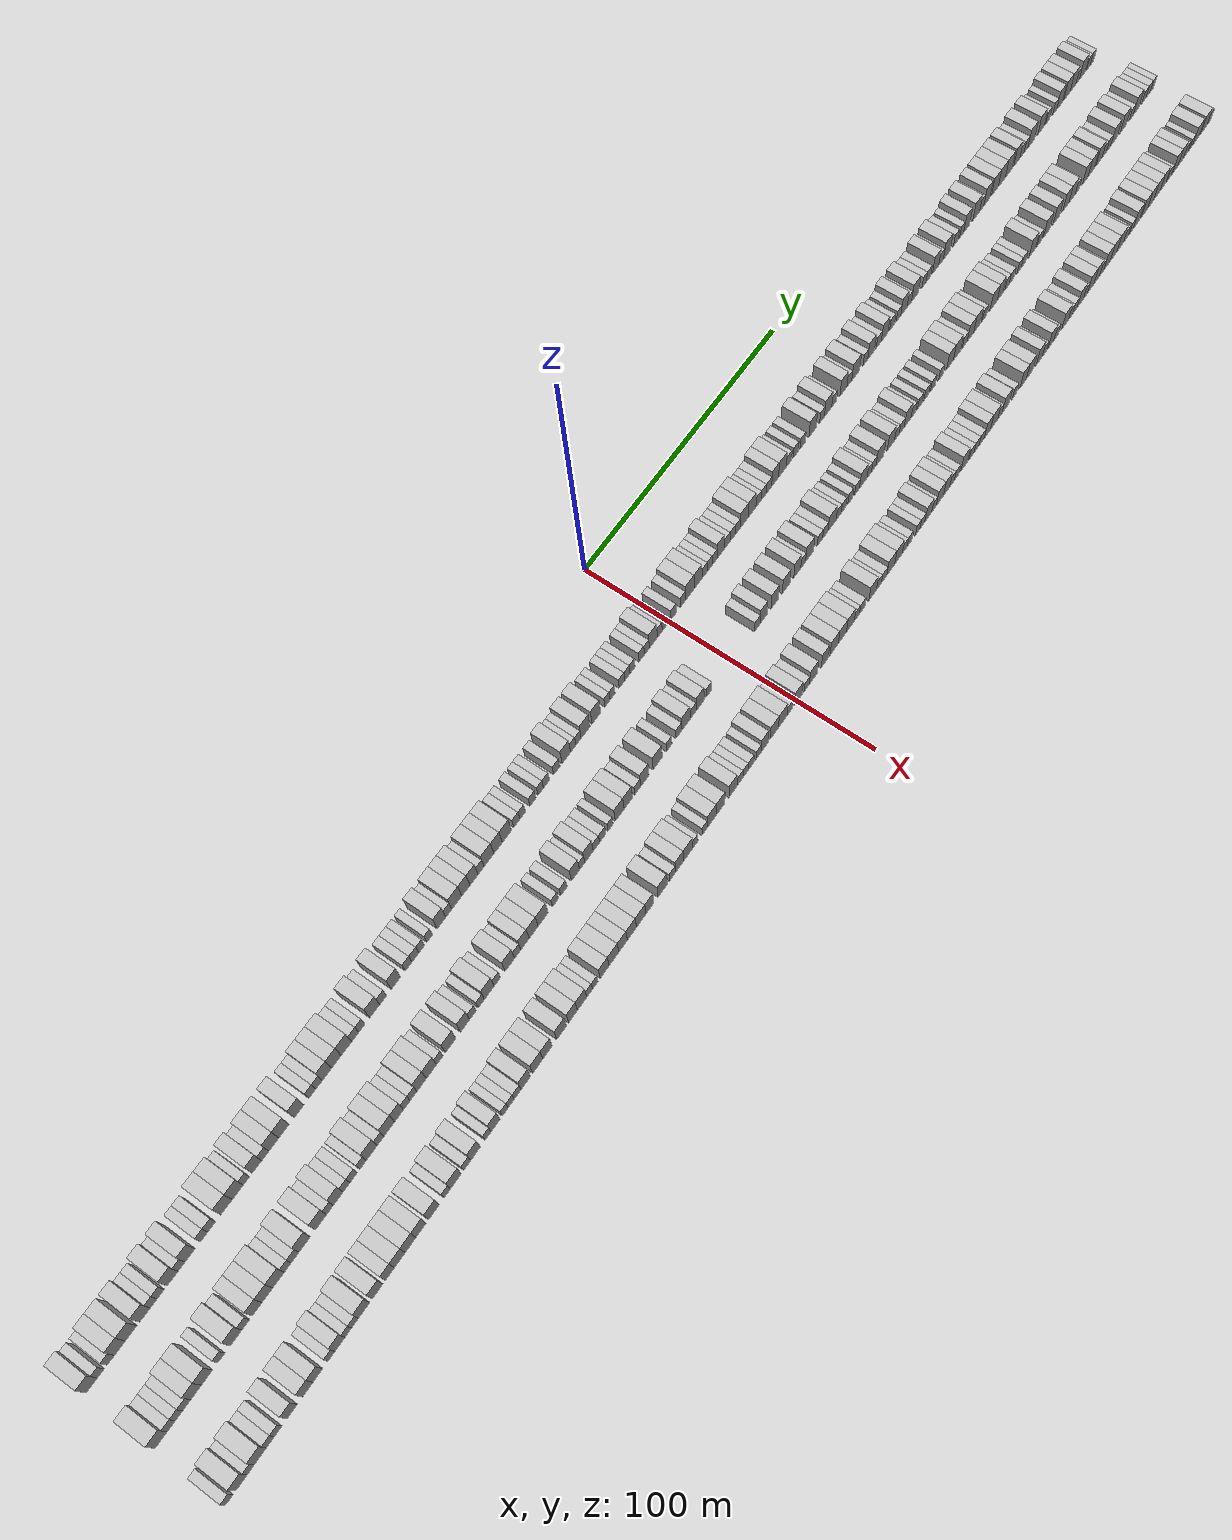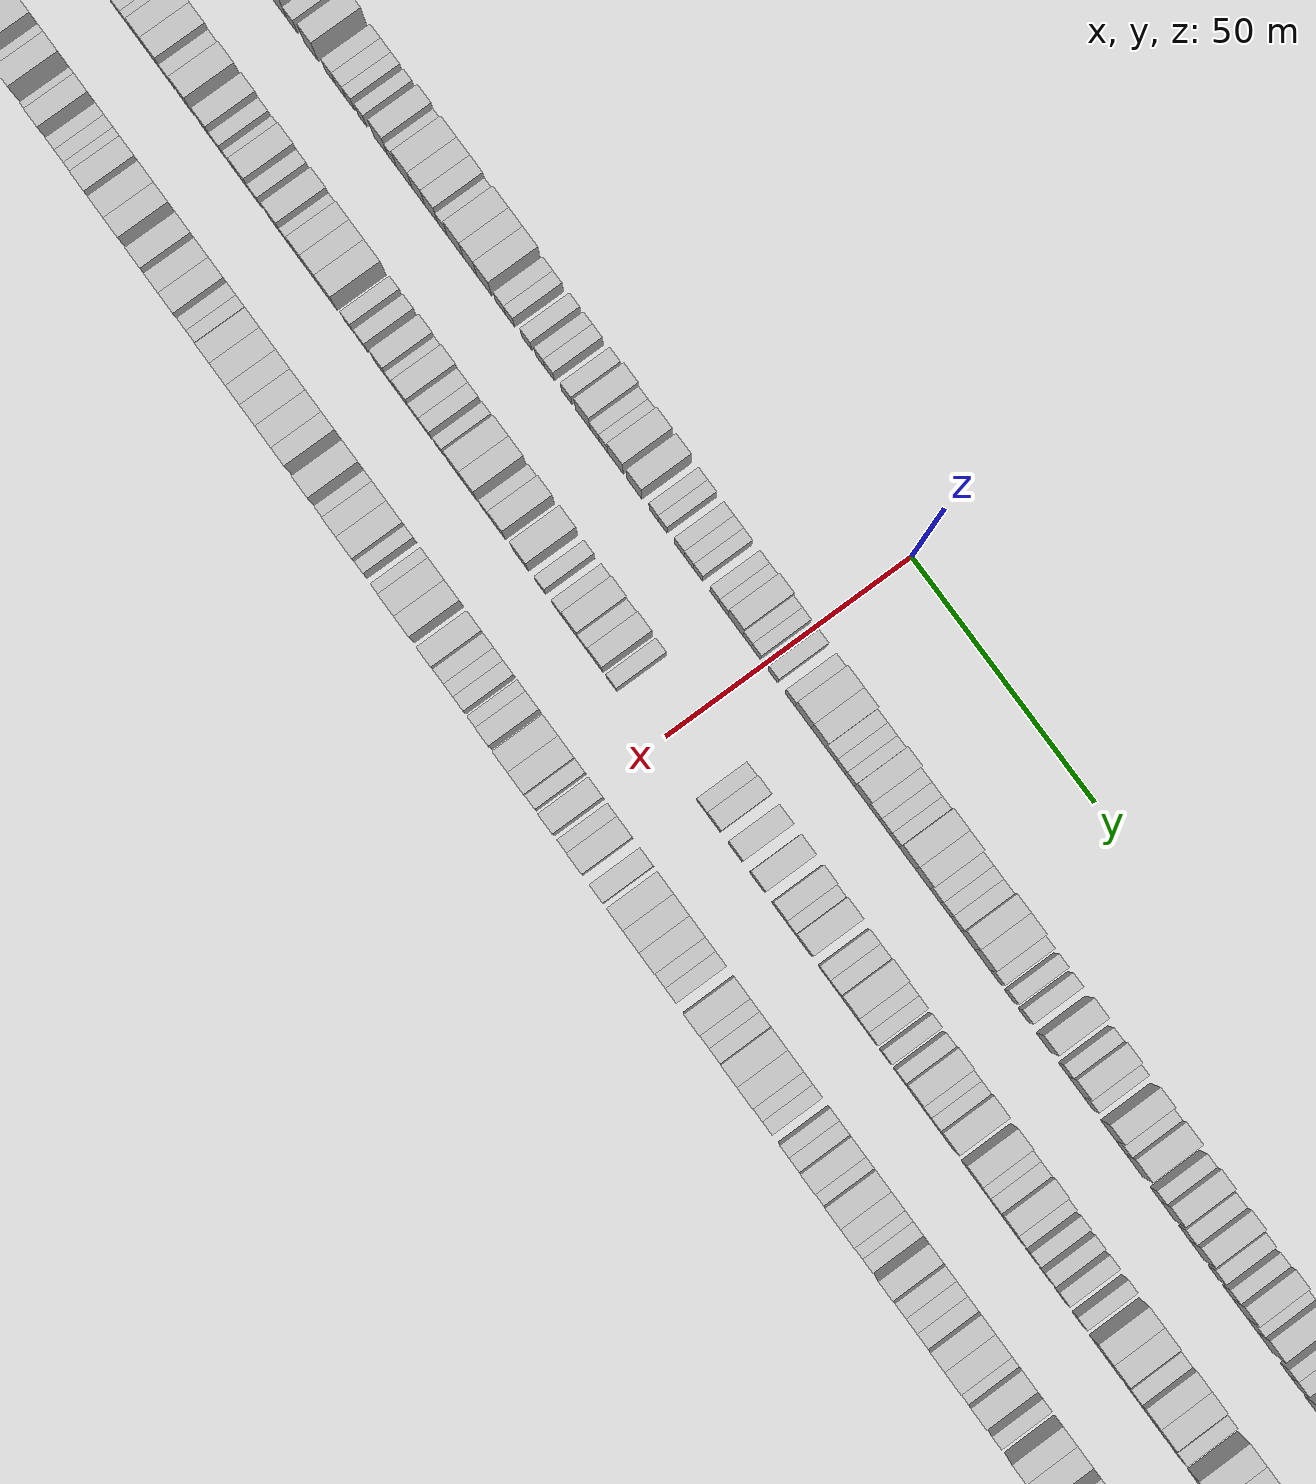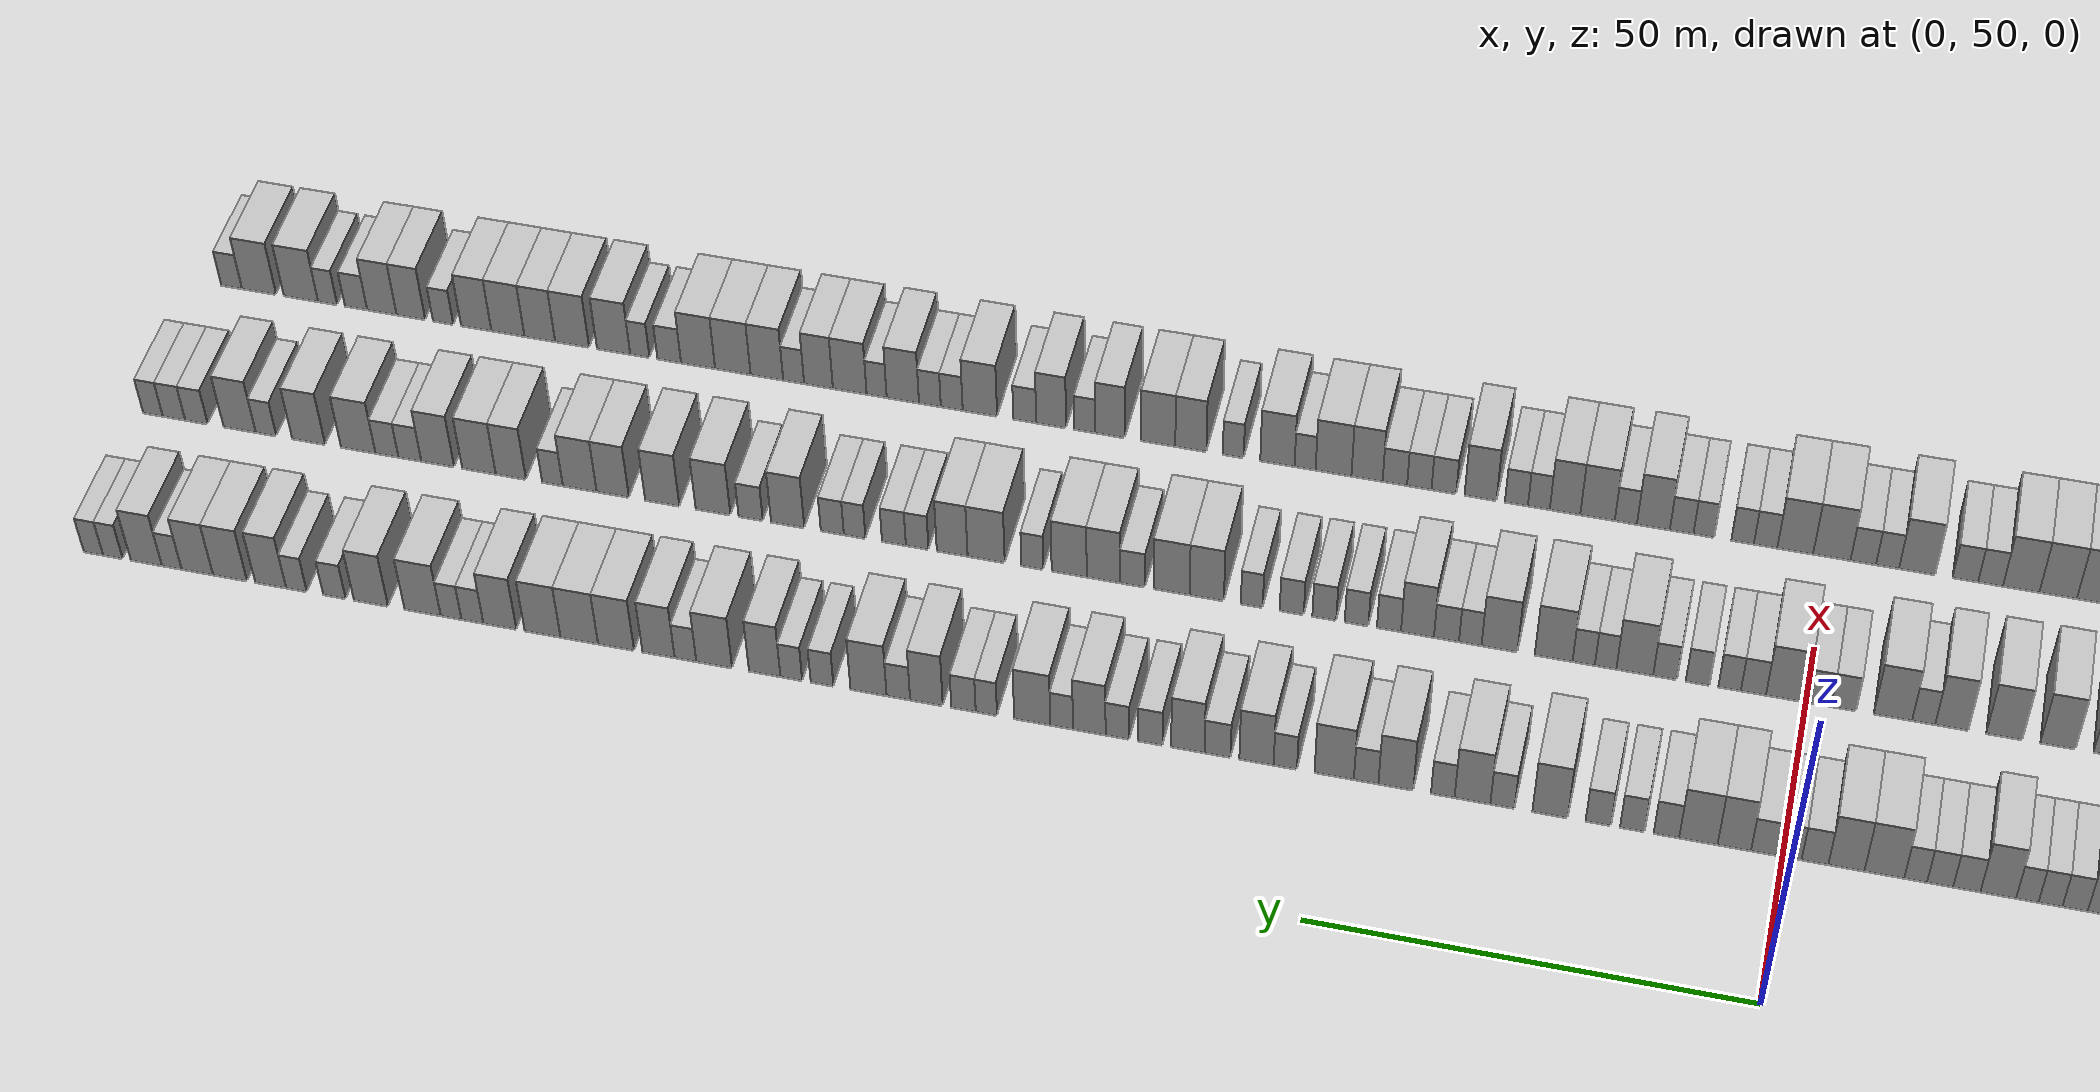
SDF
<sdf version="1.6">
 <world name="default">
  <scene>
   <sky><clouds><speed>12</speed></clouds></sky>
   <ambient>0.4 0.4 0.4 1</ambient>
   <background>0.7 0.7 0.7 1</background>
   <shadows>1</shadows>
  </scene>
  <gravity>0 0 -9.8066</gravity>
  <magnetic_field>6e-06 2.3e-05 -4.2e-05</magnetic_field>
  <physics default="0" name="default_physics" type="ode">
   <ode>
    <solver>
     <type>quick</type>
     <iters>10</iters>
     <sor>1.0</sor>
     <use_dynamic_moi_rescaling>0</use_dynamic_moi_rescaling>
    </solver>
    <constraints>
     <cfm>0</cfm>
     <erp>0.2</erp>
     <contact_max_correcting_vel>100</contact_max_correcting_vel>
     <contact_surface_layer>0.001</contact_surface_layer>
    </constraints>
   </ode>
   <max_step_size>0.004</max_step_size>
   <real_time_factor>1</real_time_factor>
   <real_time_update_rate>250</real_time_update_rate>
  </physics>
  <light name="sun" type="directional">
   <pose>0 0 10 0 0 0</pose>
   <diffuse>0.8 0.8 0.8 1</diffuse>
   <specular>0.2 0.2 0.2 1</specular>
   <attenuation>
    <range>1000</range>
    <constant>0.9</constant>
    <linear>0.01</linear>
    <quadratic>0.001</quadratic>
   </attenuation>
   <direction>-0.5 0.1 -0.9</direction>
  </light>
  <model name="building_1">
   <static>1</static>
   <pose>25.0000 -245.9847 0 0.000000 0.000000 0.000000</pose>
   <link name="link">
    <pose>0 0 4.50 0 0 0</pose>
    <collision name="collision"><geometry><box><size>10.0000 4.0305 9.0000</size></box></geometry></collision>
    <visual name="visual">
     <cast_shadows>0</cast_shadows>
     <geometry><box><size>10.0000 4.0305 9.0000</size></box></geometry>
     <material>
      <script>
       <uri>model://HANNAS_wall/materials/scripts</uri>
       <uri>model://HANNAS_wall/materials/textures</uri>
       <name>vrc/HANNAS_wall</name>
      </script>
     </material>
    </visual>
   </link>
  </model>
  <model name="building_2">
   <static>1</static>
   <pose>25.0000 -242.7346 0 0.000000 0.000000 0.000000</pose>
   <link name="link">
    <pose>0 0 3.00 0 0 0</pose>
    <collision name="collision"><geometry><box><size>10.0000 2.4697 6.0000</size></box></geometry></collision>
    <visual name="visual">
     <cast_shadows>0</cast_shadows>
     <geometry><box><size>10.0000 2.4697 6.0000</size></box></geometry>
     <material>
      <script>
       <uri>model://HANNAS_wall/materials/scripts</uri>
       <uri>model://HANNAS_wall/materials/textures</uri>
       <name>vrc/HANNAS_wall</name>
      </script>
     </material>
    </visual>
   </link>
  </model>
  <model name="building_3">
   <static>1</static>
   <pose>25.0000 -239.1668 0 0.000000 0.000000 0.000000</pose>
   <link name="link">
    <pose>0 0 3.00 0 0 0</pose>
    <collision name="collision"><geometry><box><size>10.0000 2.6659 6.0000</size></box></geometry></collision>
    <visual name="visual">
     <cast_shadows>0</cast_shadows>
     <geometry><box><size>10.0000 2.6659 6.0000</size></box></geometry>
     <material>
      <script>
       <uri>model://HANNAS_wall/materials/scripts</uri>
       <uri>model://HANNAS_wall/materials/textures</uri>
       <name>vrc/HANNAS_wall</name>
      </script>
     </material>
    </visual>
   </link>
  </model>
  <model name="building_4">
   <static>1</static>
   <pose>25.0000 -235.8251 0 0.000000 0.000000 0.000000</pose>
   <link name="link">
    <pose>0 0 4.50 0 0 0</pose>
    <collision name="collision"><geometry><box><size>10.0000 4.0175 9.0000</size></box></geometry></collision>
    <visual name="visual">
     <cast_shadows>0</cast_shadows>
     <geometry><box><size>10.0000 4.0175 9.0000</size></box></geometry>
     <material>
      <script>
       <uri>model://HANNAS_wall/materials/scripts</uri>
       <uri>model://HANNAS_wall/materials/textures</uri>
       <name>vrc/HANNAS_wall</name>
      </script>
     </material>
    </visual>
   </link>
  </model>
  <model name="building_5">
   <static>1</static>
   <pose>25.0000 -231.7156 0 0.000000 0.000000 0.000000</pose>
   <link name="link">
    <pose>0 0 4.50 0 0 0</pose>
    <collision name="collision"><geometry><box><size>10.0000 4.2014 9.0000</size></box></geometry></collision>
    <visual name="visual">
     <cast_shadows>0</cast_shadows>
     <geometry><box><size>10.0000 4.2014 9.0000</size></box></geometry>
     <material>
      <script>
       <uri>model://HANNAS_wall/materials/scripts</uri>
       <uri>model://HANNAS_wall/materials/textures</uri>
       <name>vrc/HANNAS_wall</name>
      </script>
     </material>
    </visual>
   </link>
  </model>
  <model name="building_6">
   <static>1</static>
   <pose>25.0000 -226.6154 0 0.000000 0.000000 0.000000</pose>
   <link name="link">
    <pose>0 0 4.50 0 0 0</pose>
    <collision name="collision"><geometry><box><size>10.0000 3.9990 9.0000</size></box></geometry></collision>
    <visual name="visual">
     <cast_shadows>0</cast_shadows>
     <geometry><box><size>10.0000 3.9990 9.0000</size></box></geometry>
     <material>
      <script>
       <uri>model://HANNAS_wall/materials/scripts</uri>
       <uri>model://HANNAS_wall/materials/textures</uri>
       <name>vrc/HANNAS_wall</name>
      </script>
     </material>
    </visual>
   </link>
  </model>
  <model name="building_7">
   <static>1</static>
   <pose>25.0000 -223.3513 0 0.000000 0.000000 0.000000</pose>
   <link name="link">
    <pose>0 0 3.00 0 0 0</pose>
    <collision name="collision"><geometry><box><size>10.0000 2.5292 6.0000</size></box></geometry></collision>
    <visual name="visual">
     <cast_shadows>0</cast_shadows>
     <geometry><box><size>10.0000 2.5292 6.0000</size></box></geometry>
     <material>
      <script>
       <uri>model://HANNAS_wall/materials/scripts</uri>
       <uri>model://HANNAS_wall/materials/textures</uri>
       <name>vrc/HANNAS_wall</name>
      </script>
     </material>
    </visual>
   </link>
  </model>
  <model name="building_8">
   <static>1</static>
   <pose>25.0000 -220.7528 0 0.000000 0.000000 0.000000</pose>
   <link name="link">
    <pose>0 0 3.00 0 0 0</pose>
    <collision name="collision"><geometry><box><size>10.0000 2.6679 6.0000</size></box></geometry></collision>
    <visual name="visual">
     <cast_shadows>0</cast_shadows>
     <geometry><box><size>10.0000 2.6679 6.0000</size></box></geometry>
     <material>
      <script>
       <uri>model://HANNAS_wall/materials/scripts</uri>
       <uri>model://HANNAS_wall/materials/textures</uri>
       <name>vrc/HANNAS_wall</name>
      </script>
     </material>
    </visual>
   </link>
  </model>
  <model name="building_9">
   <static>1</static>
   <pose>25.0000 -216.3720 0 0.000000 0.000000 0.000000</pose>
   <link name="link">
    <pose>0 0 4.50 0 0 0</pose>
    <collision name="collision"><geometry><box><size>10.0000 4.0935 9.0000</size></box></geometry></collision>
    <visual name="visual">
     <cast_shadows>0</cast_shadows>
     <geometry><box><size>10.0000 4.0935 9.0000</size></box></geometry>
     <material>
      <script>
       <uri>model://HANNAS_wall/materials/scripts</uri>
       <uri>model://HANNAS_wall/materials/textures</uri>
       <name>vrc/HANNAS_wall</name>
      </script>
     </material>
    </visual>
   </link>
  </model>
  <model name="building_10">
   <static>1</static>
   <pose>25.0000 -212.9944 0 0.000000 0.000000 0.000000</pose>
   <link name="link">
    <pose>0 0 3.00 0 0 0</pose>
    <collision name="collision"><geometry><box><size>10.0000 2.6618 6.0000</size></box></geometry></collision>
    <visual name="visual">
     <cast_shadows>0</cast_shadows>
     <geometry><box><size>10.0000 2.6618 6.0000</size></box></geometry>
     <material>
      <script>
       <uri>model://HANNAS_wall/materials/scripts</uri>
       <uri>model://HANNAS_wall/materials/textures</uri>
       <name>vrc/HANNAS_wall</name>
      </script>
     </material>
    </visual>
   </link>
  </model>
  <model name="building_11">
   <static>1</static>
   <pose>25.0000 -209.7556 0 0.000000 0.000000 0.000000</pose>
   <link name="link">
    <pose>0 0 4.50 0 0 0</pose>
    <collision name="collision"><geometry><box><size>10.0000 3.8159 9.0000</size></box></geometry></collision>
    <visual name="visual">
     <cast_shadows>0</cast_shadows>
     <geometry><box><size>10.0000 3.8159 9.0000</size></box></geometry>
     <material>
      <script>
       <uri>model://HANNAS_wall/materials/scripts</uri>
       <uri>model://HANNAS_wall/materials/textures</uri>
       <name>vrc/HANNAS_wall</name>
      </script>
     </material>
    </visual>
   </link>
  </model>
  <model name="building_12">
   <static>1</static>
   <pose>25.0000 -204.4514 0 0.000000 0.000000 0.000000</pose>
   <link name="link">
    <pose>0 0 3.00 0 0 0</pose>
    <collision name="collision"><geometry><box><size>10.0000 2.7926 6.0000</size></box></geometry></collision>
    <visual name="visual">
     <cast_shadows>0</cast_shadows>
     <geometry><box><size>10.0000 2.7926 6.0000</size></box></geometry>
     <material>
      <script>
       <uri>model://HANNAS_wall/materials/scripts</uri>
       <uri>model://HANNAS_wall/materials/textures</uri>
       <name>vrc/HANNAS_wall</name>
      </script>
     </material>
    </visual>
   </link>
  </model>
  <model name="building_13">
   <static>1</static>
   <pose>25.0000 -201.5556 0 0.000000 0.000000 0.000000</pose>
   <link name="link">
    <pose>0 0 3.00 0 0 0</pose>
    <collision name="collision"><geometry><box><size>10.0000 2.9989 6.0000</size></box></geometry></collision>
    <visual name="visual">
     <cast_shadows>0</cast_shadows>
     <geometry><box><size>10.0000 2.9989 6.0000</size></box></geometry>
     <material>
      <script>
       <uri>model://HANNAS_wall/materials/scripts</uri>
       <uri>model://HANNAS_wall/materials/textures</uri>
       <name>vrc/HANNAS_wall</name>
      </script>
     </material>
    </visual>
   </link>
  </model>
  <model name="building_14">
   <static>1</static>
   <pose>25.0000 -195.8231 0 0.000000 0.000000 0.000000</pose>
   <link name="link">
    <pose>0 0 4.50 0 0 0</pose>
    <collision name="collision"><geometry><box><size>10.0000 4.4661 9.0000</size></box></geometry></collision>
    <visual name="visual">
     <cast_shadows>0</cast_shadows>
     <geometry><box><size>10.0000 4.4661 9.0000</size></box></geometry>
     <material>
      <script>
       <uri>model://HANNAS_wall/materials/scripts</uri>
       <uri>model://HANNAS_wall/materials/textures</uri>
       <name>vrc/HANNAS_wall</name>
      </script>
     </material>
    </visual>
   </link>
  </model>
  <model name="building_15">
   <static>1</static>
   <pose>25.0000 -191.4522 0 0.000000 0.000000 0.000000</pose>
   <link name="link">
    <pose>0 0 4.50 0 0 0</pose>
    <collision name="collision"><geometry><box><size>10.0000 4.2756 9.0000</size></box></geometry></collision>
    <visual name="visual">
     <cast_shadows>0</cast_shadows>
     <geometry><box><size>10.0000 4.2756 9.0000</size></box></geometry>
     <material>
      <script>
       <uri>model://HANNAS_wall/materials/scripts</uri>
       <uri>model://HANNAS_wall/materials/textures</uri>
       <name>vrc/HANNAS_wall</name>
      </script>
     </material>
    </visual>
   </link>
  </model>
  <model name="building_16">
   <static>1</static>
   <pose>25.0000 -188.0689 0 0.000000 0.000000 0.000000</pose>
   <link name="link">
    <pose>0 0 3.00 0 0 0</pose>
    <collision name="collision"><geometry><box><size>10.0000 2.4910 6.0000</size></box></geometry></collision>
    <visual name="visual">
     <cast_shadows>0</cast_shadows>
     <geometry><box><size>10.0000 2.4910 6.0000</size></box></geometry>
     <material>
      <script>
       <uri>model://HANNAS_wall/materials/scripts</uri>
       <uri>model://HANNAS_wall/materials/textures</uri>
       <name>vrc/HANNAS_wall</name>
      </script>
     </material>
    </visual>
   </link>
  </model>
  <model name="building_17">
   <static>1</static>
   <pose>25.0000 -183.9358 0 0.000000 0.000000 0.000000</pose>
   <link name="link">
    <pose>0 0 4.50 0 0 0</pose>
    <collision name="collision"><geometry><box><size>10.0000 3.7752 9.0000</size></box></geometry></collision>
    <visual name="visual">
     <cast_shadows>0</cast_shadows>
     <geometry><box><size>10.0000 3.7752 9.0000</size></box></geometry>
     <material>
      <script>
       <uri>model://HANNAS_wall/materials/scripts</uri>
       <uri>model://HANNAS_wall/materials/textures</uri>
       <name>vrc/HANNAS_wall</name>
      </script>
     </material>
    </visual>
   </link>
  </model>
  <model name="building_18">
   <static>1</static>
   <pose>25.0000 -180.6475 0 0.000000 0.000000 0.000000</pose>
   <link name="link">
    <pose>0 0 3.00 0 0 0</pose>
    <collision name="collision"><geometry><box><size>10.0000 2.8013 6.0000</size></box></geometry></collision>
    <visual name="visual">
     <cast_shadows>0</cast_shadows>
     <geometry><box><size>10.0000 2.8013 6.0000</size></box></geometry>
     <material>
      <script>
       <uri>model://HANNAS_wall/materials/scripts</uri>
       <uri>model://HANNAS_wall/materials/textures</uri>
       <name>vrc/HANNAS_wall</name>
      </script>
     </material>
    </visual>
   </link>
  </model>
  <model name="building_19">
   <static>1</static>
   <pose>25.0000 -177.2562 0 0.000000 0.000000 0.000000</pose>
   <link name="link">
    <pose>0 0 4.50 0 0 0</pose>
    <collision name="collision"><geometry><box><size>10.0000 3.9814 9.0000</size></box></geometry></collision>
    <visual name="visual">
     <cast_shadows>0</cast_shadows>
     <geometry><box><size>10.0000 3.9814 9.0000</size></box></geometry>
     <material>
      <script>
       <uri>model://HANNAS_wall/materials/scripts</uri>
       <uri>model://HANNAS_wall/materials/textures</uri>
       <name>vrc/HANNAS_wall</name>
      </script>
     </material>
    </visual>
   </link>
  </model>
  <model name="building_20">
   <static>1</static>
   <pose>25.0000 -173.1930 0 0.000000 0.000000 0.000000</pose>
   <link name="link">
    <pose>0 0 4.50 0 0 0</pose>
    <collision name="collision"><geometry><box><size>10.0000 4.1450 9.0000</size></box></geometry></collision>
    <visual name="visual">
     <cast_shadows>0</cast_shadows>
     <geometry><box><size>10.0000 4.1450 9.0000</size></box></geometry>
     <material>
      <script>
       <uri>model://HANNAS_wall/materials/scripts</uri>
       <uri>model://HANNAS_wall/materials/textures</uri>
       <name>vrc/HANNAS_wall</name>
      </script>
     </material>
    </visual>
   </link>
  </model>
  <model name="building_21">
   <static>1</static>
   <pose>25.0000 -167.1621 0 0.000000 0.000000 0.000000</pose>
   <link name="link">
    <pose>0 0 4.50 0 0 0</pose>
    <collision name="collision"><geometry><box><size>10.0000 3.9168 9.0000</size></box></geometry></collision>
    <visual name="visual">
     <cast_shadows>0</cast_shadows>
     <geometry><box><size>10.0000 3.9168 9.0000</size></box></geometry>
     <material>
      <script>
       <uri>model://HANNAS_wall/materials/scripts</uri>
       <uri>model://HANNAS_wall/materials/textures</uri>
       <name>vrc/HANNAS_wall</name>
      </script>
     </material>
    </visual>
   </link>
  </model>
  <model name="building_22">
   <static>1</static>
   <pose>25.0000 -161.8120 0 0.000000 0.000000 0.000000</pose>
   <link name="link">
    <pose>0 0 3.00 0 0 0</pose>
    <collision name="collision"><geometry><box><size>10.0000 2.7835 6.0000</size></box></geometry></collision>
    <visual name="visual">
     <cast_shadows>0</cast_shadows>
     <geometry><box><size>10.0000 2.7835 6.0000</size></box></geometry>
     <material>
      <script>
       <uri>model://HANNAS_wall/materials/scripts</uri>
       <uri>model://HANNAS_wall/materials/textures</uri>
       <name>vrc/HANNAS_wall</name>
      </script>
     </material>
    </visual>
   </link>
  </model>
  <model name="building_23">
   <static>1</static>
   <pose>25.0000 -159.0636 0 0.000000 0.000000 0.000000</pose>
   <link name="link">
    <pose>0 0 3.00 0 0 0</pose>
    <collision name="collision"><geometry><box><size>10.0000 2.7134 6.0000</size></box></geometry></collision>
    <visual name="visual">
     <cast_shadows>0</cast_shadows>
     <geometry><box><size>10.0000 2.7134 6.0000</size></box></geometry>
     <material>
      <script>
       <uri>model://HANNAS_wall/materials/scripts</uri>
       <uri>model://HANNAS_wall/materials/textures</uri>
       <name>vrc/HANNAS_wall</name>
      </script>
     </material>
    </visual>
   </link>
  </model>
  <model name="building_24">
   <static>1</static>
   <pose>25.0000 -155.8258 0 0.000000 0.000000 0.000000</pose>
   <link name="link">
    <pose>0 0 4.50 0 0 0</pose>
    <collision name="collision"><geometry><box><size>10.0000 3.7621 9.0000</size></box></geometry></collision>
    <visual name="visual">
     <cast_shadows>0</cast_shadows>
     <geometry><box><size>10.0000 3.7621 9.0000</size></box></geometry>
     <material>
      <script>
       <uri>model://HANNAS_wall/materials/scripts</uri>
       <uri>model://HANNAS_wall/materials/textures</uri>
       <name>vrc/HANNAS_wall</name>
      </script>
     </material>
    </visual>
   </link>
  </model>
  <model name="building_25">
   <static>1</static>
   <pose>25.0000 -151.9421 0 0.000000 0.000000 0.000000</pose>
   <link name="link">
    <pose>0 0 4.50 0 0 0</pose>
    <collision name="collision"><geometry><box><size>10.0000 4.0052 9.0000</size></box></geometry></collision>
    <visual name="visual">
     <cast_shadows>0</cast_shadows>
     <geometry><box><size>10.0000 4.0052 9.0000</size></box></geometry>
     <material>
      <script>
       <uri>model://HANNAS_wall/materials/scripts</uri>
       <uri>model://HANNAS_wall/materials/textures</uri>
       <name>vrc/HANNAS_wall</name>
      </script>
     </material>
    </visual>
   </link>
  </model>
  <model name="building_26">
   <static>1</static>
   <pose>25.0000 -147.7740 0 0.000000 0.000000 0.000000</pose>
   <link name="link">
    <pose>0 0 4.50 0 0 0</pose>
    <collision name="collision"><geometry><box><size>10.0000 4.3311 9.0000</size></box></geometry></collision>
    <visual name="visual">
     <cast_shadows>0</cast_shadows>
     <geometry><box><size>10.0000 4.3311 9.0000</size></box></geometry>
     <material>
      <script>
       <uri>model://HANNAS_wall/materials/scripts</uri>
       <uri>model://HANNAS_wall/materials/textures</uri>
       <name>vrc/HANNAS_wall</name>
      </script>
     </material>
    </visual>
   </link>
  </model>
  <model name="building_27">
   <static>1</static>
   <pose>25.0000 -144.1327 0 0.000000 0.000000 0.000000</pose>
   <link name="link">
    <pose>0 0 3.00 0 0 0</pose>
    <collision name="collision"><geometry><box><size>10.0000 2.9514 6.0000</size></box></geometry></collision>
    <visual name="visual">
     <cast_shadows>0</cast_shadows>
     <geometry><box><size>10.0000 2.9514 6.0000</size></box></geometry>
     <material>
      <script>
       <uri>model://HANNAS_wall/materials/scripts</uri>
       <uri>model://HANNAS_wall/materials/textures</uri>
       <name>vrc/HANNAS_wall</name>
      </script>
     </material>
    </visual>
   </link>
  </model>
  <model name="building_28">
   <static>1</static>
   <pose>25.0000 -141.3631 0 0.000000 0.000000 0.000000</pose>
   <link name="link">
    <pose>0 0 3.00 0 0 0</pose>
    <collision name="collision"><geometry><box><size>10.0000 2.5877 6.0000</size></box></geometry></collision>
    <visual name="visual">
     <cast_shadows>0</cast_shadows>
     <geometry><box><size>10.0000 2.5877 6.0000</size></box></geometry>
     <material>
      <script>
       <uri>model://HANNAS_wall/materials/scripts</uri>
       <uri>model://HANNAS_wall/materials/textures</uri>
       <name>vrc/HANNAS_wall</name>
      </script>
     </material>
    </visual>
   </link>
  </model>
  <model name="building_29">
   <static>1</static>
   <pose>25.0000 -135.9635 0 0.000000 0.000000 0.000000</pose>
   <link name="link">
    <pose>0 0 4.50 0 0 0</pose>
    <collision name="collision"><geometry><box><size>10.0000 4.2116 9.0000</size></box></geometry></collision>
    <visual name="visual">
     <cast_shadows>0</cast_shadows>
     <geometry><box><size>10.0000 4.2116 9.0000</size></box></geometry>
     <material>
      <script>
       <uri>model://HANNAS_wall/materials/scripts</uri>
       <uri>model://HANNAS_wall/materials/textures</uri>
       <name>vrc/HANNAS_wall</name>
      </script>
     </material>
    </visual>
   </link>
  </model>
  <model name="building_30">
   <static>1</static>
   <pose>25.0000 -132.3957 0 0.000000 0.000000 0.000000</pose>
   <link name="link">
    <pose>0 0 3.00 0 0 0</pose>
    <collision name="collision"><geometry><box><size>10.0000 2.9239 6.0000</size></box></geometry></collision>
    <visual name="visual">
     <cast_shadows>0</cast_shadows>
     <geometry><box><size>10.0000 2.9239 6.0000</size></box></geometry>
     <material>
      <script>
       <uri>model://HANNAS_wall/materials/scripts</uri>
       <uri>model://HANNAS_wall/materials/textures</uri>
       <name>vrc/HANNAS_wall</name>
      </script>
     </material>
    </visual>
   </link>
  </model>
  <model name="building_31">
   <static>1</static>
   <pose>25.0000 -126.9586 0 0.000000 0.000000 0.000000</pose>
   <link name="link">
    <pose>0 0 4.50 0 0 0</pose>
    <collision name="collision"><geometry><box><size>10.0000 3.9502 9.0000</size></box></geometry></collision>
    <visual name="visual">
     <cast_shadows>0</cast_shadows>
     <geometry><box><size>10.0000 3.9502 9.0000</size></box></geometry>
     <material>
      <script>
       <uri>model://HANNAS_wall/materials/scripts</uri>
       <uri>model://HANNAS_wall/materials/textures</uri>
       <name>vrc/HANNAS_wall</name>
      </script>
     </material>
    </visual>
   </link>
  </model>
  <model name="building_32">
   <static>1</static>
   <pose>25.0000 -121.5272 0 0.000000 0.000000 0.000000</pose>
   <link name="link">
    <pose>0 0 3.00 0 0 0</pose>
    <collision name="collision"><geometry><box><size>10.0000 2.9127 6.0000</size></box></geometry></collision>
    <visual name="visual">
     <cast_shadows>0</cast_shadows>
     <geometry><box><size>10.0000 2.9127 6.0000</size></box></geometry>
     <material>
      <script>
       <uri>model://HANNAS_wall/materials/scripts</uri>
       <uri>model://HANNAS_wall/materials/textures</uri>
       <name>vrc/HANNAS_wall</name>
      </script>
     </material>
    </visual>
   </link>
  </model>
  <model name="building_33">
   <static>1</static>
   <pose>25.0000 -118.5944 0 0.000000 0.000000 0.000000</pose>
   <link name="link">
    <pose>0 0 3.00 0 0 0</pose>
    <collision name="collision"><geometry><box><size>10.0000 2.9529 6.0000</size></box></geometry></collision>
    <visual name="visual">
     <cast_shadows>0</cast_shadows>
     <geometry><box><size>10.0000 2.9529 6.0000</size></box></geometry>
     <material>
      <script>
       <uri>model://HANNAS_wall/materials/scripts</uri>
       <uri>model://HANNAS_wall/materials/textures</uri>
       <name>vrc/HANNAS_wall</name>
      </script>
     </material>
    </visual>
   </link>
  </model>
  <model name="building_34">
   <static>1</static>
   <pose>25.0000 -115.8798 0 0.000000 0.000000 0.000000</pose>
   <link name="link">
    <pose>0 0 3.00 0 0 0</pose>
    <collision name="collision"><geometry><box><size>10.0000 2.4761 6.0000</size></box></geometry></collision>
    <visual name="visual">
     <cast_shadows>0</cast_shadows>
     <geometry><box><size>10.0000 2.4761 6.0000</size></box></geometry>
     <material>
      <script>
       <uri>model://HANNAS_wall/materials/scripts</uri>
       <uri>model://HANNAS_wall/materials/textures</uri>
       <name>vrc/HANNAS_wall</name>
      </script>
     </material>
    </visual>
   </link>
  </model>
  <model name="building_35">
   <static>1</static>
   <pose>25.0000 -112.4168 0 0.000000 0.000000 0.000000</pose>
   <link name="link">
    <pose>0 0 3.00 0 0 0</pose>
    <collision name="collision"><geometry><box><size>10.0000 2.4500 6.0000</size></box></geometry></collision>
    <visual name="visual">
     <cast_shadows>0</cast_shadows>
     <geometry><box><size>10.0000 2.4500 6.0000</size></box></geometry>
     <material>
      <script>
       <uri>model://HANNAS_wall/materials/scripts</uri>
       <uri>model://HANNAS_wall/materials/textures</uri>
       <name>vrc/HANNAS_wall</name>
      </script>
     </material>
    </visual>
   </link>
  </model>
  <model name="building_36">
   <static>1</static>
   <pose>25.0000 -107.2620 0 0.000000 0.000000 0.000000</pose>
   <link name="link">
    <pose>0 0 4.50 0 0 0</pose>
    <collision name="collision"><geometry><box><size>10.0000 3.8595 9.0000</size></box></geometry></collision>
    <visual name="visual">
     <cast_shadows>0</cast_shadows>
     <geometry><box><size>10.0000 3.8595 9.0000</size></box></geometry>
     <material>
      <script>
       <uri>model://HANNAS_wall/materials/scripts</uri>
       <uri>model://HANNAS_wall/materials/textures</uri>
       <name>vrc/HANNAS_wall</name>
      </script>
     </material>
    </visual>
   </link>
  </model>
  <model name="building_37">
   <static>1</static>
   <pose>25.0000 -104.0259 0 0.000000 0.000000 0.000000</pose>
   <link name="link">
    <pose>0 0 3.00 0 0 0</pose>
    <collision name="collision"><geometry><box><size>10.0000 2.6127 6.0000</size></box></geometry></collision>
    <visual name="visual">
     <cast_shadows>0</cast_shadows>
     <geometry><box><size>10.0000 2.6127 6.0000</size></box></geometry>
     <material>
      <script>
       <uri>model://HANNAS_wall/materials/scripts</uri>
       <uri>model://HANNAS_wall/materials/textures</uri>
       <name>vrc/HANNAS_wall</name>
      </script>
     </material>
    </visual>
   </link>
  </model>
  <model name="building_38">
   <static>1</static>
   <pose>25.0000 -100.5047 0 0.000000 0.000000 0.000000</pose>
   <link name="link">
    <pose>0 0 4.50 0 0 0</pose>
    <collision name="collision"><geometry><box><size>10.0000 4.4297 9.0000</size></box></geometry></collision>
    <visual name="visual">
     <cast_shadows>0</cast_shadows>
     <geometry><box><size>10.0000 4.4297 9.0000</size></box></geometry>
     <material>
      <script>
       <uri>model://HANNAS_wall/materials/scripts</uri>
       <uri>model://HANNAS_wall/materials/textures</uri>
       <name>vrc/HANNAS_wall</name>
      </script>
     </material>
    </visual>
   </link>
  </model>
  <model name="building_39">
   <static>1</static>
   <pose>25.0000 -96.4687 0 0.000000 0.000000 0.000000</pose>
   <link name="link">
    <pose>0 0 4.50 0 0 0</pose>
    <collision name="collision"><geometry><box><size>10.0000 3.6423 9.0000</size></box></geometry></collision>
    <visual name="visual">
     <cast_shadows>0</cast_shadows>
     <geometry><box><size>10.0000 3.6423 9.0000</size></box></geometry>
     <material>
      <script>
       <uri>model://HANNAS_wall/materials/scripts</uri>
       <uri>model://HANNAS_wall/materials/textures</uri>
       <name>vrc/HANNAS_wall</name>
      </script>
     </material>
    </visual>
   </link>
  </model>
  <model name="building_40">
   <static>1</static>
   <pose>25.0000 -92.8418 0 0.000000 0.000000 0.000000</pose>
   <link name="link">
    <pose>0 0 4.50 0 0 0</pose>
    <collision name="collision"><geometry><box><size>10.0000 3.6114 9.0000</size></box></geometry></collision>
    <visual name="visual">
     <cast_shadows>0</cast_shadows>
     <geometry><box><size>10.0000 3.6114 9.0000</size></box></geometry>
     <material>
      <script>
       <uri>model://HANNAS_wall/materials/scripts</uri>
       <uri>model://HANNAS_wall/materials/textures</uri>
       <name>vrc/HANNAS_wall</name>
      </script>
     </material>
    </visual>
   </link>
  </model>
  <model name="building_41">
   <static>1</static>
   <pose>25.0000 -89.6788 0 0.000000 0.000000 0.000000</pose>
   <link name="link">
    <pose>0 0 3.00 0 0 0</pose>
    <collision name="collision"><geometry><box><size>10.0000 2.7146 6.0000</size></box></geometry></collision>
    <visual name="visual">
     <cast_shadows>0</cast_shadows>
     <geometry><box><size>10.0000 2.7146 6.0000</size></box></geometry>
     <material>
      <script>
       <uri>model://HANNAS_wall/materials/scripts</uri>
       <uri>model://HANNAS_wall/materials/textures</uri>
       <name>vrc/HANNAS_wall</name>
      </script>
     </material>
    </visual>
   </link>
  </model>
  <model name="building_42">
   <static>1</static>
   <pose>25.0000 -86.0987 0 0.000000 0.000000 0.000000</pose>
   <link name="link">
    <pose>0 0 4.50 0 0 0</pose>
    <collision name="collision"><geometry><box><size>10.0000 4.4457 9.0000</size></box></geometry></collision>
    <visual name="visual">
     <cast_shadows>0</cast_shadows>
     <geometry><box><size>10.0000 4.4457 9.0000</size></box></geometry>
     <material>
      <script>
       <uri>model://HANNAS_wall/materials/scripts</uri>
       <uri>model://HANNAS_wall/materials/textures</uri>
       <name>vrc/HANNAS_wall</name>
      </script>
     </material>
    </visual>
   </link>
  </model>
  <model name="building_43">
   <static>1</static>
   <pose>25.0000 -81.9614 0 0.000000 0.000000 0.000000</pose>
   <link name="link">
    <pose>0 0 4.50 0 0 0</pose>
    <collision name="collision"><geometry><box><size>10.0000 3.8288 9.0000</size></box></geometry></collision>
    <visual name="visual">
     <cast_shadows>0</cast_shadows>
     <geometry><box><size>10.0000 3.8288 9.0000</size></box></geometry>
     <material>
      <script>
       <uri>model://HANNAS_wall/materials/scripts</uri>
       <uri>model://HANNAS_wall/materials/textures</uri>
       <name>vrc/HANNAS_wall</name>
      </script>
     </material>
    </visual>
   </link>
  </model>
  <model name="building_44">
   <static>1</static>
   <pose>25.0000 -77.9471 0 0.000000 0.000000 0.000000</pose>
   <link name="link">
    <pose>0 0 4.50 0 0 0</pose>
    <collision name="collision"><geometry><box><size>10.0000 4.1999 9.0000</size></box></geometry></collision>
    <visual name="visual">
     <cast_shadows>0</cast_shadows>
     <geometry><box><size>10.0000 4.1999 9.0000</size></box></geometry>
     <material>
      <script>
       <uri>model://HANNAS_wall/materials/scripts</uri>
       <uri>model://HANNAS_wall/materials/textures</uri>
       <name>vrc/HANNAS_wall</name>
      </script>
     </material>
    </visual>
   </link>
  </model>
  <model name="building_45">
   <static>1</static>
   <pose>25.0000 -73.4030 0 0.000000 0.000000 0.000000</pose>
   <link name="link">
    <pose>0 0 3.00 0 0 0</pose>
    <collision name="collision"><geometry><box><size>10.0000 2.8882 6.0000</size></box></geometry></collision>
    <visual name="visual">
     <cast_shadows>0</cast_shadows>
     <geometry><box><size>10.0000 2.8882 6.0000</size></box></geometry>
     <material>
      <script>
       <uri>model://HANNAS_wall/materials/scripts</uri>
       <uri>model://HANNAS_wall/materials/textures</uri>
       <name>vrc/HANNAS_wall</name>
      </script>
     </material>
    </visual>
   </link>
  </model>
  <model name="building_46">
   <static>1</static>
   <pose>25.0000 -70.6926 0 0.000000 0.000000 0.000000</pose>
   <link name="link">
    <pose>0 0 3.00 0 0 0</pose>
    <collision name="collision"><geometry><box><size>10.0000 2.5327 6.0000</size></box></geometry></collision>
    <visual name="visual">
     <cast_shadows>0</cast_shadows>
     <geometry><box><size>10.0000 2.5327 6.0000</size></box></geometry>
     <material>
      <script>
       <uri>model://HANNAS_wall/materials/scripts</uri>
       <uri>model://HANNAS_wall/materials/textures</uri>
       <name>vrc/HANNAS_wall</name>
      </script>
     </material>
    </visual>
   </link>
  </model>
  <model name="building_47">
   <static>1</static>
   <pose>25.0000 -65.9847 0 0.000000 0.000000 0.000000</pose>
   <link name="link">
    <pose>0 0 3.00 0 0 0</pose>
    <collision name="collision"><geometry><box><size>10.0000 2.8832 6.0000</size></box></geometry></collision>
    <visual name="visual">
     <cast_shadows>0</cast_shadows>
     <geometry><box><size>10.0000 2.8832 6.0000</size></box></geometry>
     <material>
      <script>
       <uri>model://HANNAS_wall/materials/scripts</uri>
       <uri>model://HANNAS_wall/materials/textures</uri>
       <name>vrc/HANNAS_wall</name>
      </script>
     </material>
    </visual>
   </link>
  </model>
  <model name="building_48">
   <static>1</static>
   <pose>25.0000 -62.2846 0 0.000000 0.000000 0.000000</pose>
   <link name="link">
    <pose>0 0 3.00 0 0 0</pose>
    <collision name="collision"><geometry><box><size>10.0000 2.5170 6.0000</size></box></geometry></collision>
    <visual name="visual">
     <cast_shadows>0</cast_shadows>
     <geometry><box><size>10.0000 2.5170 6.0000</size></box></geometry>
     <material>
      <script>
       <uri>model://HANNAS_wall/materials/scripts</uri>
       <uri>model://HANNAS_wall/materials/textures</uri>
       <name>vrc/HANNAS_wall</name>
      </script>
     </material>
    </visual>
   </link>
  </model>
  <model name="building_49">
   <static>1</static>
   <pose>25.0000 -59.6618 0 0.000000 0.000000 0.000000</pose>
   <link name="link">
    <pose>0 0 3.00 0 0 0</pose>
    <collision name="collision"><geometry><box><size>10.0000 2.7288 6.0000</size></box></geometry></collision>
    <visual name="visual">
     <cast_shadows>0</cast_shadows>
     <geometry><box><size>10.0000 2.7288 6.0000</size></box></geometry>
     <material>
      <script>
       <uri>model://HANNAS_wall/materials/scripts</uri>
       <uri>model://HANNAS_wall/materials/textures</uri>
       <name>vrc/HANNAS_wall</name>
      </script>
     </material>
    </visual>
   </link>
  </model>
  <model name="building_50">
   <static>1</static>
   <pose>25.0000 -54.8117 0 0.000000 0.000000 0.000000</pose>
   <link name="link">
    <pose>0 0 3.00 0 0 0</pose>
    <collision name="collision"><geometry><box><size>10.0000 2.9714 6.0000</size></box></geometry></collision>
    <visual name="visual">
     <cast_shadows>0</cast_shadows>
     <geometry><box><size>10.0000 2.9714 6.0000</size></box></geometry>
     <material>
      <script>
       <uri>model://HANNAS_wall/materials/scripts</uri>
       <uri>model://HANNAS_wall/materials/textures</uri>
       <name>vrc/HANNAS_wall</name>
      </script>
     </material>
    </visual>
   </link>
  </model>
  <model name="building_51">
   <static>1</static>
   <pose>25.0000 -50.3097 0 0.000000 0.000000 0.000000</pose>
   <link name="link">
    <pose>0 0 4.50 0 0 0</pose>
    <collision name="collision"><geometry><box><size>10.0000 4.0326 9.0000</size></box></geometry></collision>
    <visual name="visual">
     <cast_shadows>0</cast_shadows>
     <geometry><box><size>10.0000 4.0326 9.0000</size></box></geometry>
     <material>
      <script>
       <uri>model://HANNAS_wall/materials/scripts</uri>
       <uri>model://HANNAS_wall/materials/textures</uri>
       <name>vrc/HANNAS_wall</name>
      </script>
     </material>
    </visual>
   </link>
  </model>
  <model name="building_52">
   <static>1</static>
   <pose>25.0000 -47.0149 0 0.000000 0.000000 0.000000</pose>
   <link name="link">
    <pose>0 0 3.00 0 0 0</pose>
    <collision name="collision"><geometry><box><size>10.0000 2.5572 6.0000</size></box></geometry></collision>
    <visual name="visual">
     <cast_shadows>0</cast_shadows>
     <geometry><box><size>10.0000 2.5572 6.0000</size></box></geometry>
     <material>
      <script>
       <uri>model://HANNAS_wall/materials/scripts</uri>
       <uri>model://HANNAS_wall/materials/textures</uri>
       <name>vrc/HANNAS_wall</name>
      </script>
     </material>
    </visual>
   </link>
  </model>
  <model name="building_53">
   <static>1</static>
   <pose>25.0000 -44.5212 0 0.000000 0.000000 0.000000</pose>
   <link name="link">
    <pose>0 0 3.00 0 0 0</pose>
    <collision name="collision"><geometry><box><size>10.0000 2.4300 6.0000</size></box></geometry></collision>
    <visual name="visual">
     <cast_shadows>0</cast_shadows>
     <geometry><box><size>10.0000 2.4300 6.0000</size></box></geometry>
     <material>
      <script>
       <uri>model://HANNAS_wall/materials/scripts</uri>
       <uri>model://HANNAS_wall/materials/textures</uri>
       <name>vrc/HANNAS_wall</name>
      </script>
     </material>
    </visual>
   </link>
  </model>
  <model name="building_54">
   <static>1</static>
   <pose>25.0000 -41.1703 0 0.000000 0.000000 0.000000</pose>
   <link name="link">
    <pose>0 0 4.50 0 0 0</pose>
    <collision name="collision"><geometry><box><size>10.0000 4.2718 9.0000</size></box></geometry></collision>
    <visual name="visual">
     <cast_shadows>0</cast_shadows>
     <geometry><box><size>10.0000 4.2718 9.0000</size></box></geometry>
     <material>
      <script>
       <uri>model://HANNAS_wall/materials/scripts</uri>
       <uri>model://HANNAS_wall/materials/textures</uri>
       <name>vrc/HANNAS_wall</name>
      </script>
     </material>
    </visual>
   </link>
  </model>
  <model name="building_55">
   <static>1</static>
   <pose>25.0000 -35.9543 0 0.000000 0.000000 0.000000</pose>
   <link name="link">
    <pose>0 0 4.50 0 0 0</pose>
    <collision name="collision"><geometry><box><size>10.0000 4.1602 9.0000</size></box></geometry></collision>
    <visual name="visual">
     <cast_shadows>0</cast_shadows>
     <geometry><box><size>10.0000 4.1602 9.0000</size></box></geometry>
     <material>
      <script>
       <uri>model://HANNAS_wall/materials/scripts</uri>
       <uri>model://HANNAS_wall/materials/textures</uri>
       <name>vrc/HANNAS_wall</name>
      </script>
     </material>
    </visual>
   </link>
  </model>
  <model name="building_56">
   <static>1</static>
   <pose>25.0000 -30.5991 0 0.000000 0.000000 0.000000</pose>
   <link name="link">
    <pose>0 0 3.00 0 0 0</pose>
    <collision name="collision"><geometry><box><size>10.0000 2.5501 6.0000</size></box></geometry></collision>
    <visual name="visual">
     <cast_shadows>0</cast_shadows>
     <geometry><box><size>10.0000 2.5501 6.0000</size></box></geometry>
     <material>
      <script>
       <uri>model://HANNAS_wall/materials/scripts</uri>
       <uri>model://HANNAS_wall/materials/textures</uri>
       <name>vrc/HANNAS_wall</name>
      </script>
     </material>
    </visual>
   </link>
  </model>
  <model name="building_57">
   <static>1</static>
   <pose>25.0000 -28.1071 0 0.000000 0.000000 0.000000</pose>
   <link name="link">
    <pose>0 0 3.00 0 0 0</pose>
    <collision name="collision"><geometry><box><size>10.0000 2.4339 6.0000</size></box></geometry></collision>
    <visual name="visual">
     <cast_shadows>0</cast_shadows>
     <geometry><box><size>10.0000 2.4339 6.0000</size></box></geometry>
     <material>
      <script>
       <uri>model://HANNAS_wall/materials/scripts</uri>
       <uri>model://HANNAS_wall/materials/textures</uri>
       <name>vrc/HANNAS_wall</name>
      </script>
     </material>
    </visual>
   </link>
  </model>
  <model name="building_58">
   <static>1</static>
   <pose>25.0000 -23.5045 0 0.000000 0.000000 0.000000</pose>
   <link name="link">
    <pose>0 0 3.00 0 0 0</pose>
    <collision name="collision"><geometry><box><size>10.0000 2.7713 6.0000</size></box></geometry></collision>
    <visual name="visual">
     <cast_shadows>0</cast_shadows>
     <geometry><box><size>10.0000 2.7713 6.0000</size></box></geometry>
     <material>
      <script>
       <uri>model://HANNAS_wall/materials/scripts</uri>
       <uri>model://HANNAS_wall/materials/textures</uri>
       <name>vrc/HANNAS_wall</name>
      </script>
     </material>
    </visual>
   </link>
  </model>
  <model name="building_59">
   <static>1</static>
   <pose>25.0000 -20.8307 0 0.000000 0.000000 0.000000</pose>
   <link name="link">
    <pose>0 0 3.00 0 0 0</pose>
    <collision name="collision"><geometry><box><size>10.0000 2.5764 6.0000</size></box></geometry></collision>
    <visual name="visual">
     <cast_shadows>0</cast_shadows>
     <geometry><box><size>10.0000 2.5764 6.0000</size></box></geometry>
     <material>
      <script>
       <uri>model://HANNAS_wall/materials/scripts</uri>
       <uri>model://HANNAS_wall/materials/textures</uri>
       <name>vrc/HANNAS_wall</name>
      </script>
     </material>
    </visual>
   </link>
  </model>
  <model name="building_60">
   <static>1</static>
   <pose>25.0000 -18.3024 0 0.000000 0.000000 0.000000</pose>
   <link name="link">
    <pose>0 0 3.00 0 0 0</pose>
    <collision name="collision"><geometry><box><size>10.0000 2.4802 6.0000</size></box></geometry></collision>
    <visual name="visual">
     <cast_shadows>0</cast_shadows>
     <geometry><box><size>10.0000 2.4802 6.0000</size></box></geometry>
     <material>
      <script>
       <uri>model://HANNAS_wall/materials/scripts</uri>
       <uri>model://HANNAS_wall/materials/textures</uri>
       <name>vrc/HANNAS_wall</name>
      </script>
     </material>
    </visual>
   </link>
  </model>
  <model name="building_61">
   <static>1</static>
   <pose>25.0000 -13.7433 0 0.000000 0.000000 0.000000</pose>
   <link name="link">
    <pose>0 0 3.00 0 0 0</pose>
    <collision name="collision"><geometry><box><size>10.0000 2.6382 6.0000</size></box></geometry></collision>
    <visual name="visual">
     <cast_shadows>0</cast_shadows>
     <geometry><box><size>10.0000 2.6382 6.0000</size></box></geometry>
     <material>
      <script>
       <uri>model://HANNAS_wall/materials/scripts</uri>
       <uri>model://HANNAS_wall/materials/textures</uri>
       <name>vrc/HANNAS_wall</name>
      </script>
     </material>
    </visual>
   </link>
  </model>
  <model name="building_62">
   <static>1</static>
   <pose>25.0000 -11.1985 0 0.000000 0.000000 0.000000</pose>
   <link name="link">
    <pose>0 0 3.00 0 0 0</pose>
    <collision name="collision"><geometry><box><size>10.0000 2.4514 6.0000</size></box></geometry></collision>
    <visual name="visual">
     <cast_shadows>0</cast_shadows>
     <geometry><box><size>10.0000 2.4514 6.0000</size></box></geometry>
     <material>
      <script>
       <uri>model://HANNAS_wall/materials/scripts</uri>
       <uri>model://HANNAS_wall/materials/textures</uri>
       <name>vrc/HANNAS_wall</name>
      </script>
     </material>
    </visual>
   </link>
  </model>
  <model name="building_63">
   <static>1</static>
   <pose>25.0000 -7.9587 0 0.000000 0.000000 0.000000</pose>
   <link name="link">
    <pose>0 0 4.50 0 0 0</pose>
    <collision name="collision"><geometry><box><size>10.0000 4.0282 9.0000</size></box></geometry></collision>
    <visual name="visual">
     <cast_shadows>0</cast_shadows>
     <geometry><box><size>10.0000 4.0282 9.0000</size></box></geometry>
     <material>
      <script>
       <uri>model://HANNAS_wall/materials/scripts</uri>
       <uri>model://HANNAS_wall/materials/textures</uri>
       <name>vrc/HANNAS_wall</name>
      </script>
     </material>
    </visual>
   </link>
  </model>
  <model name="building_64">
   <static>1</static>
   <pose>25.0000 -4.7389 0 0.000000 0.000000 0.000000</pose>
   <link name="link">
    <pose>0 0 3.00 0 0 0</pose>
    <collision name="collision"><geometry><box><size>10.0000 2.4114 6.0000</size></box></geometry></collision>
    <visual name="visual">
     <cast_shadows>0</cast_shadows>
     <geometry><box><size>10.0000 2.4114 6.0000</size></box></geometry>
     <material>
      <script>
       <uri>model://HANNAS_wall/materials/scripts</uri>
       <uri>model://HANNAS_wall/materials/textures</uri>
       <name>vrc/HANNAS_wall</name>
      </script>
     </material>
    </visual>
   </link>
  </model>
  <model name="building_65">
   <static>1</static>
   <pose>25.0000 -2.3086 0 0.000000 0.000000 0.000000</pose>
   <link name="link">
    <pose>0 0 3.00 0 0 0</pose>
    <collision name="collision"><geometry><box><size>10.0000 2.4492 6.0000</size></box></geometry></collision>
    <visual name="visual">
     <cast_shadows>0</cast_shadows>
     <geometry><box><size>10.0000 2.4492 6.0000</size></box></geometry>
     <material>
      <script>
       <uri>model://HANNAS_wall/materials/scripts</uri>
       <uri>model://HANNAS_wall/materials/textures</uri>
       <name>vrc/HANNAS_wall</name>
      </script>
     </material>
    </visual>
   </link>
  </model>
  <model name="building_66">
   <static>1</static>
   <pose>25.0000 2.2780 0 0.000000 0.000000 0.000000</pose>
   <link name="link">
    <pose>0 0 3.00 0 0 0</pose>
    <collision name="collision"><geometry><box><size>10.0000 2.7241 6.0000</size></box></geometry></collision>
    <visual name="visual">
     <cast_shadows>0</cast_shadows>
     <geometry><box><size>10.0000 2.7241 6.0000</size></box></geometry>
     <material>
      <script>
       <uri>model://HANNAS_wall/materials/scripts</uri>
       <uri>model://HANNAS_wall/materials/textures</uri>
       <name>vrc/HANNAS_wall</name>
      </script>
     </material>
    </visual>
   </link>
  </model>
  <model name="building_67">
   <static>1</static>
   <pose>25.0000 7.0333 0 0.000000 0.000000 0.000000</pose>
   <link name="link">
    <pose>0 0 3.00 0 0 0</pose>
    <collision name="collision"><geometry><box><size>10.0000 2.7864 6.0000</size></box></geometry></collision>
    <visual name="visual">
     <cast_shadows>0</cast_shadows>
     <geometry><box><size>10.0000 2.7864 6.0000</size></box></geometry>
     <material>
      <script>
       <uri>model://HANNAS_wall/materials/scripts</uri>
       <uri>model://HANNAS_wall/materials/textures</uri>
       <name>vrc/HANNAS_wall</name>
      </script>
     </material>
    </visual>
   </link>
  </model>
  <model name="building_68">
   <static>1</static>
   <pose>25.0000 10.6391 0 0.000000 0.000000 0.000000</pose>
   <link name="link">
    <pose>0 0 4.50 0 0 0</pose>
    <collision name="collision"><geometry><box><size>10.0000 4.4251 9.0000</size></box></geometry></collision>
    <visual name="visual">
     <cast_shadows>0</cast_shadows>
     <geometry><box><size>10.0000 4.4251 9.0000</size></box></geometry>
     <material>
      <script>
       <uri>model://HANNAS_wall/materials/scripts</uri>
       <uri>model://HANNAS_wall/materials/textures</uri>
       <name>vrc/HANNAS_wall</name>
      </script>
     </material>
    </visual>
   </link>
  </model>
  <model name="building_69">
   <static>1</static>
   <pose>25.0000 14.8348 0 0.000000 0.000000 0.000000</pose>
   <link name="link">
    <pose>0 0 4.50 0 0 0</pose>
    <collision name="collision"><geometry><box><size>10.0000 3.9664 9.0000</size></box></geometry></collision>
    <visual name="visual">
     <cast_shadows>0</cast_shadows>
     <geometry><box><size>10.0000 3.9664 9.0000</size></box></geometry>
     <material>
      <script>
       <uri>model://HANNAS_wall/materials/scripts</uri>
       <uri>model://HANNAS_wall/materials/textures</uri>
       <name>vrc/HANNAS_wall</name>
      </script>
     </material>
    </visual>
   </link>
  </model>
  <model name="building_70">
   <static>1</static>
   <pose>25.0000 18.1874 0 0.000000 0.000000 0.000000</pose>
   <link name="link">
    <pose>0 0 3.00 0 0 0</pose>
    <collision name="collision"><geometry><box><size>10.0000 2.7388 6.0000</size></box></geometry></collision>
    <visual name="visual">
     <cast_shadows>0</cast_shadows>
     <geometry><box><size>10.0000 2.7388 6.0000</size></box></geometry>
     <material>
      <script>
       <uri>model://HANNAS_wall/materials/scripts</uri>
       <uri>model://HANNAS_wall/materials/textures</uri>
       <name>vrc/HANNAS_wall</name>
      </script>
     </material>
    </visual>
   </link>
  </model>
  <model name="building_71">
   <static>1</static>
   <pose>25.0000 20.8497 0 0.000000 0.000000 0.000000</pose>
   <link name="link">
    <pose>0 0 3.00 0 0 0</pose>
    <collision name="collision"><geometry><box><size>10.0000 2.5858 6.0000</size></box></geometry></collision>
    <visual name="visual">
     <cast_shadows>0</cast_shadows>
     <geometry><box><size>10.0000 2.5858 6.0000</size></box></geometry>
     <material>
      <script>
       <uri>model://HANNAS_wall/materials/scripts</uri>
       <uri>model://HANNAS_wall/materials/textures</uri>
       <name>vrc/HANNAS_wall</name>
      </script>
     </material>
    </visual>
   </link>
  </model>
  <model name="building_72">
   <static>1</static>
   <pose>25.0000 23.3550 0 0.000000 0.000000 0.000000</pose>
   <link name="link">
    <pose>0 0 3.00 0 0 0</pose>
    <collision name="collision"><geometry><box><size>10.0000 2.4249 6.0000</size></box></geometry></collision>
    <visual name="visual">
     <cast_shadows>0</cast_shadows>
     <geometry><box><size>10.0000 2.4249 6.0000</size></box></geometry>
     <material>
      <script>
       <uri>model://HANNAS_wall/materials/scripts</uri>
       <uri>model://HANNAS_wall/materials/textures</uri>
       <name>vrc/HANNAS_wall</name>
      </script>
     </material>
    </visual>
   </link>
  </model>
  <model name="building_73">
   <static>1</static>
   <pose>25.0000 26.5085 0 0.000000 0.000000 0.000000</pose>
   <link name="link">
    <pose>0 0 4.50 0 0 0</pose>
    <collision name="collision"><geometry><box><size>10.0000 3.8821 9.0000</size></box></geometry></collision>
    <visual name="visual">
     <cast_shadows>0</cast_shadows>
     <geometry><box><size>10.0000 3.8821 9.0000</size></box></geometry>
     <material>
      <script>
       <uri>model://HANNAS_wall/materials/scripts</uri>
       <uri>model://HANNAS_wall/materials/textures</uri>
       <name>vrc/HANNAS_wall</name>
      </script>
     </material>
    </visual>
   </link>
  </model>
  <model name="building_74">
   <static>1</static>
   <pose>25.0000 29.9336 0 0.000000 0.000000 0.000000</pose>
   <link name="link">
    <pose>0 0 3.00 0 0 0</pose>
    <collision name="collision"><geometry><box><size>10.0000 2.9679 6.0000</size></box></geometry></collision>
    <visual name="visual">
     <cast_shadows>0</cast_shadows>
     <geometry><box><size>10.0000 2.9679 6.0000</size></box></geometry>
     <material>
      <script>
       <uri>model://HANNAS_wall/materials/scripts</uri>
       <uri>model://HANNAS_wall/materials/textures</uri>
       <name>vrc/HANNAS_wall</name>
      </script>
     </material>
    </visual>
   </link>
  </model>
  <model name="building_75">
   <static>1</static>
   <pose>25.0000 32.8421 0 0.000000 0.000000 0.000000</pose>
   <link name="link">
    <pose>0 0 3.00 0 0 0</pose>
    <collision name="collision"><geometry><box><size>10.0000 2.8491 6.0000</size></box></geometry></collision>
    <visual name="visual">
     <cast_shadows>0</cast_shadows>
     <geometry><box><size>10.0000 2.8491 6.0000</size></box></geometry>
     <material>
      <script>
       <uri>model://HANNAS_wall/materials/scripts</uri>
       <uri>model://HANNAS_wall/materials/textures</uri>
       <name>vrc/HANNAS_wall</name>
      </script>
     </material>
    </visual>
   </link>
  </model>
  <model name="building_76">
   <static>1</static>
   <pose>25.0000 35.5147 0 0.000000 0.000000 0.000000</pose>
   <link name="link">
    <pose>0 0 3.00 0 0 0</pose>
    <collision name="collision"><geometry><box><size>10.0000 2.4961 6.0000</size></box></geometry></collision>
    <visual name="visual">
     <cast_shadows>0</cast_shadows>
     <geometry><box><size>10.0000 2.4961 6.0000</size></box></geometry>
     <material>
      <script>
       <uri>model://HANNAS_wall/materials/scripts</uri>
       <uri>model://HANNAS_wall/materials/textures</uri>
       <name>vrc/HANNAS_wall</name>
      </script>
     </material>
    </visual>
   </link>
  </model>
  <model name="building_77">
   <static>1</static>
   <pose>25.0000 38.9422 0 0.000000 0.000000 0.000000</pose>
   <link name="link">
    <pose>0 0 4.50 0 0 0</pose>
    <collision name="collision"><geometry><box><size>10.0000 4.3588 9.0000</size></box></geometry></collision>
    <visual name="visual">
     <cast_shadows>0</cast_shadows>
     <geometry><box><size>10.0000 4.3588 9.0000</size></box></geometry>
     <material>
      <script>
       <uri>model://HANNAS_wall/materials/scripts</uri>
       <uri>model://HANNAS_wall/materials/textures</uri>
       <name>vrc/HANNAS_wall</name>
      </script>
     </material>
    </visual>
   </link>
  </model>
  <model name="building_78">
   <static>1</static>
   <pose>25.0000 43.1015 0 0.000000 0.000000 0.000000</pose>
   <link name="link">
    <pose>0 0 4.50 0 0 0</pose>
    <collision name="collision"><geometry><box><size>10.0000 3.9598 9.0000</size></box></geometry></collision>
    <visual name="visual">
     <cast_shadows>0</cast_shadows>
     <geometry><box><size>10.0000 3.9598 9.0000</size></box></geometry>
     <material>
      <script>
       <uri>model://HANNAS_wall/materials/scripts</uri>
       <uri>model://HANNAS_wall/materials/textures</uri>
       <name>vrc/HANNAS_wall</name>
      </script>
     </material>
    </visual>
   </link>
  </model>
  <model name="building_79">
   <static>1</static>
   <pose>25.0000 46.5578 0 0.000000 0.000000 0.000000</pose>
   <link name="link">
    <pose>0 0 3.00 0 0 0</pose>
    <collision name="collision"><geometry><box><size>10.0000 2.9530 6.0000</size></box></geometry></collision>
    <visual name="visual">
     <cast_shadows>0</cast_shadows>
     <geometry><box><size>10.0000 2.9530 6.0000</size></box></geometry>
     <material>
      <script>
       <uri>model://HANNAS_wall/materials/scripts</uri>
       <uri>model://HANNAS_wall/materials/textures</uri>
       <name>vrc/HANNAS_wall</name>
      </script>
     </material>
    </visual>
   </link>
  </model>
  <model name="building_80">
   <static>1</static>
   <pose>25.0000 49.3571 0 0.000000 0.000000 0.000000</pose>
   <link name="link">
    <pose>0 0 3.00 0 0 0</pose>
    <collision name="collision"><geometry><box><size>10.0000 2.6455 6.0000</size></box></geometry></collision>
    <visual name="visual">
     <cast_shadows>0</cast_shadows>
     <geometry><box><size>10.0000 2.6455 6.0000</size></box></geometry>
     <material>
      <script>
       <uri>model://HANNAS_wall/materials/scripts</uri>
       <uri>model://HANNAS_wall/materials/textures</uri>
       <name>vrc/HANNAS_wall</name>
      </script>
     </material>
    </visual>
   </link>
  </model>
  <model name="building_81">
   <static>1</static>
   <pose>25.0000 52.1397 0 0.000000 0.000000 0.000000</pose>
   <link name="link">
    <pose>0 0 3.00 0 0 0</pose>
    <collision name="collision"><geometry><box><size>10.0000 2.9199 6.0000</size></box></geometry></collision>
    <visual name="visual">
     <cast_shadows>0</cast_shadows>
     <geometry><box><size>10.0000 2.9199 6.0000</size></box></geometry>
     <material>
      <script>
       <uri>model://HANNAS_wall/materials/scripts</uri>
       <uri>model://HANNAS_wall/materials/textures</uri>
       <name>vrc/HANNAS_wall</name>
      </script>
     </material>
    </visual>
   </link>
  </model>
  <model name="building_82">
   <static>1</static>
   <pose>25.0000 55.4530 0 0.000000 0.000000 0.000000</pose>
   <link name="link">
    <pose>0 0 4.50 0 0 0</pose>
    <collision name="collision"><geometry><box><size>10.0000 3.7066 9.0000</size></box></geometry></collision>
    <visual name="visual">
     <cast_shadows>0</cast_shadows>
     <geometry><box><size>10.0000 3.7066 9.0000</size></box></geometry>
     <material>
      <script>
       <uri>model://HANNAS_wall/materials/scripts</uri>
       <uri>model://HANNAS_wall/materials/textures</uri>
       <name>vrc/HANNAS_wall</name>
      </script>
     </material>
    </visual>
   </link>
  </model>
  <model name="building_83">
   <static>1</static>
   <pose>25.0000 59.4381 0 0.000000 0.000000 0.000000</pose>
   <link name="link">
    <pose>0 0 4.50 0 0 0</pose>
    <collision name="collision"><geometry><box><size>10.0000 4.2636 9.0000</size></box></geometry></collision>
    <visual name="visual">
     <cast_shadows>0</cast_shadows>
     <geometry><box><size>10.0000 4.2636 9.0000</size></box></geometry>
     <material>
      <script>
       <uri>model://HANNAS_wall/materials/scripts</uri>
       <uri>model://HANNAS_wall/materials/textures</uri>
       <name>vrc/HANNAS_wall</name>
      </script>
     </material>
    </visual>
   </link>
  </model>
  <model name="building_84">
   <static>1</static>
   <pose>25.0000 62.9826 0 0.000000 0.000000 0.000000</pose>
   <link name="link">
    <pose>0 0 3.00 0 0 0</pose>
    <collision name="collision"><geometry><box><size>10.0000 2.8254 6.0000</size></box></geometry></collision>
    <visual name="visual">
     <cast_shadows>0</cast_shadows>
     <geometry><box><size>10.0000 2.8254 6.0000</size></box></geometry>
     <material>
      <script>
       <uri>model://HANNAS_wall/materials/scripts</uri>
       <uri>model://HANNAS_wall/materials/textures</uri>
       <name>vrc/HANNAS_wall</name>
      </script>
     </material>
    </visual>
   </link>
  </model>
  <model name="building_85">
   <static>1</static>
   <pose>25.0000 66.7705 0 0.000000 0.000000 0.000000</pose>
   <link name="link">
    <pose>0 0 3.00 0 0 0</pose>
    <collision name="collision"><geometry><box><size>10.0000 2.7503 6.0000</size></box></geometry></collision>
    <visual name="visual">
     <cast_shadows>0</cast_shadows>
     <geometry><box><size>10.0000 2.7503 6.0000</size></box></geometry>
     <material>
      <script>
       <uri>model://HANNAS_wall/materials/scripts</uri>
       <uri>model://HANNAS_wall/materials/textures</uri>
       <name>vrc/HANNAS_wall</name>
      </script>
     </material>
    </visual>
   </link>
  </model>
  <model name="building_86">
   <static>1</static>
   <pose>25.0000 70.5676 0 0.000000 0.000000 0.000000</pose>
   <link name="link">
    <pose>0 0 3.00 0 0 0</pose>
    <collision name="collision"><geometry><box><size>10.0000 2.8439 6.0000</size></box></geometry></collision>
    <visual name="visual">
     <cast_shadows>0</cast_shadows>
     <geometry><box><size>10.0000 2.8439 6.0000</size></box></geometry>
     <material>
      <script>
       <uri>model://HANNAS_wall/materials/scripts</uri>
       <uri>model://HANNAS_wall/materials/textures</uri>
       <name>vrc/HANNAS_wall</name>
      </script>
     </material>
    </visual>
   </link>
  </model>
  <model name="building_87">
   <static>1</static>
   <pose>25.0000 75.9713 0 0.000000 0.000000 0.000000</pose>
   <link name="link">
    <pose>0 0 4.50 0 0 0</pose>
    <collision name="collision"><geometry><box><size>10.0000 3.9636 9.0000</size></box></geometry></collision>
    <visual name="visual">
     <cast_shadows>0</cast_shadows>
     <geometry><box><size>10.0000 3.9636 9.0000</size></box></geometry>
     <material>
      <script>
       <uri>model://HANNAS_wall/materials/scripts</uri>
       <uri>model://HANNAS_wall/materials/textures</uri>
       <name>vrc/HANNAS_wall</name>
      </script>
     </material>
    </visual>
   </link>
  </model>
  <model name="building_88">
   <static>1</static>
   <pose>25.0000 81.3127 0 0.000000 0.000000 0.000000</pose>
   <link name="link">
    <pose>0 0 3.00 0 0 0</pose>
    <collision name="collision"><geometry><box><size>10.0000 2.7192 6.0000</size></box></geometry></collision>
    <visual name="visual">
     <cast_shadows>0</cast_shadows>
     <geometry><box><size>10.0000 2.7192 6.0000</size></box></geometry>
     <material>
      <script>
       <uri>model://HANNAS_wall/materials/scripts</uri>
       <uri>model://HANNAS_wall/materials/textures</uri>
       <name>vrc/HANNAS_wall</name>
      </script>
     </material>
    </visual>
   </link>
  </model>
  <model name="building_89">
   <static>1</static>
   <pose>25.0000 84.6875 0 0.000000 0.000000 0.000000</pose>
   <link name="link">
    <pose>0 0 4.50 0 0 0</pose>
    <collision name="collision"><geometry><box><size>10.0000 4.0303 9.0000</size></box></geometry></collision>
    <visual name="visual">
     <cast_shadows>0</cast_shadows>
     <geometry><box><size>10.0000 4.0303 9.0000</size></box></geometry>
     <material>
      <script>
       <uri>model://HANNAS_wall/materials/scripts</uri>
       <uri>model://HANNAS_wall/materials/textures</uri>
       <name>vrc/HANNAS_wall</name>
      </script>
     </material>
    </visual>
   </link>
  </model>
  <model name="building_90">
   <static>1</static>
   <pose>25.0000 88.0320 0 0.000000 0.000000 0.000000</pose>
   <link name="link">
    <pose>0 0 3.00 0 0 0</pose>
    <collision name="collision"><geometry><box><size>10.0000 2.6586 6.0000</size></box></geometry></collision>
    <visual name="visual">
     <cast_shadows>0</cast_shadows>
     <geometry><box><size>10.0000 2.6586 6.0000</size></box></geometry>
     <material>
      <script>
       <uri>model://HANNAS_wall/materials/scripts</uri>
       <uri>model://HANNAS_wall/materials/textures</uri>
       <name>vrc/HANNAS_wall</name>
      </script>
     </material>
    </visual>
   </link>
  </model>
  <model name="building_91">
   <static>1</static>
   <pose>25.0000 93.3398 0 0.000000 0.000000 0.000000</pose>
   <link name="link">
    <pose>0 0 4.50 0 0 0</pose>
    <collision name="collision"><geometry><box><size>10.0000 3.9570 9.0000</size></box></geometry></collision>
    <visual name="visual">
     <cast_shadows>0</cast_shadows>
     <geometry><box><size>10.0000 3.9570 9.0000</size></box></geometry>
     <material>
      <script>
       <uri>model://HANNAS_wall/materials/scripts</uri>
       <uri>model://HANNAS_wall/materials/textures</uri>
       <name>vrc/HANNAS_wall</name>
      </script>
     </material>
    </visual>
   </link>
  </model>
  <model name="building_92">
   <static>1</static>
   <pose>25.0000 96.7085 0 0.000000 0.000000 0.000000</pose>
   <link name="link">
    <pose>0 0 3.00 0 0 0</pose>
    <collision name="collision"><geometry><box><size>10.0000 2.7805 6.0000</size></box></geometry></collision>
    <visual name="visual">
     <cast_shadows>0</cast_shadows>
     <geometry><box><size>10.0000 2.7805 6.0000</size></box></geometry>
     <material>
      <script>
       <uri>model://HANNAS_wall/materials/scripts</uri>
       <uri>model://HANNAS_wall/materials/textures</uri>
       <name>vrc/HANNAS_wall</name>
      </script>
     </material>
    </visual>
   </link>
  </model>
  <model name="building_93">
   <static>1</static>
   <pose>25.0000 100.3363 0 0.000000 0.000000 0.000000</pose>
   <link name="link">
    <pose>0 0 4.50 0 0 0</pose>
    <collision name="collision"><geometry><box><size>10.0000 4.4751 9.0000</size></box></geometry></collision>
    <visual name="visual">
     <cast_shadows>0</cast_shadows>
     <geometry><box><size>10.0000 4.4751 9.0000</size></box></geometry>
     <material>
      <script>
       <uri>model://HANNAS_wall/materials/scripts</uri>
       <uri>model://HANNAS_wall/materials/textures</uri>
       <name>vrc/HANNAS_wall</name>
      </script>
     </material>
    </visual>
   </link>
  </model>
  <model name="building_94">
   <static>1</static>
   <pose>25.0000 105.9063 0 0.000000 0.000000 0.000000</pose>
   <link name="link">
    <pose>0 0 3.00 0 0 0</pose>
    <collision name="collision"><geometry><box><size>10.0000 2.6651 6.0000</size></box></geometry></collision>
    <visual name="visual">
     <cast_shadows>0</cast_shadows>
     <geometry><box><size>10.0000 2.6651 6.0000</size></box></geometry>
     <material>
      <script>
       <uri>model://HANNAS_wall/materials/scripts</uri>
       <uri>model://HANNAS_wall/materials/textures</uri>
       <name>vrc/HANNAS_wall</name>
      </script>
     </material>
    </visual>
   </link>
  </model>
  <model name="building_95">
   <static>1</static>
   <pose>25.0000 109.1983 0 0.000000 0.000000 0.000000</pose>
   <link name="link">
    <pose>0 0 4.50 0 0 0</pose>
    <collision name="collision"><geometry><box><size>10.0000 3.9188 9.0000</size></box></geometry></collision>
    <visual name="visual">
     <cast_shadows>0</cast_shadows>
     <geometry><box><size>10.0000 3.9188 9.0000</size></box></geometry>
     <material>
      <script>
       <uri>model://HANNAS_wall/materials/scripts</uri>
       <uri>model://HANNAS_wall/materials/textures</uri>
       <name>vrc/HANNAS_wall</name>
      </script>
     </material>
    </visual>
   </link>
  </model>
  <model name="building_96">
   <static>1</static>
   <pose>25.0000 113.6531 0 0.000000 0.000000 0.000000</pose>
   <link name="link">
    <pose>0 0 3.00 0 0 0</pose>
    <collision name="collision"><geometry><box><size>10.0000 2.9909 6.0000</size></box></geometry></collision>
    <visual name="visual">
     <cast_shadows>0</cast_shadows>
     <geometry><box><size>10.0000 2.9909 6.0000</size></box></geometry>
     <material>
      <script>
       <uri>model://HANNAS_wall/materials/scripts</uri>
       <uri>model://HANNAS_wall/materials/textures</uri>
       <name>vrc/HANNAS_wall</name>
      </script>
     </material>
    </visual>
   </link>
  </model>
  <model name="building_97">
   <static>1</static>
   <pose>25.0000 117.0629 0 0.000000 0.000000 0.000000</pose>
   <link name="link">
    <pose>0 0 4.50 0 0 0</pose>
    <collision name="collision"><geometry><box><size>10.0000 3.8287 9.0000</size></box></geometry></collision>
    <visual name="visual">
     <cast_shadows>0</cast_shadows>
     <geometry><box><size>10.0000 3.8287 9.0000</size></box></geometry>
     <material>
      <script>
       <uri>model://HANNAS_wall/materials/scripts</uri>
       <uri>model://HANNAS_wall/materials/textures</uri>
       <name>vrc/HANNAS_wall</name>
      </script>
     </material>
    </visual>
   </link>
  </model>
  <model name="building_98">
   <static>1</static>
   <pose>25.0000 121.3862 0 0.000000 0.000000 0.000000</pose>
   <link name="link">
    <pose>0 0 3.00 0 0 0</pose>
    <collision name="collision"><geometry><box><size>10.0000 2.8179 6.0000</size></box></geometry></collision>
    <visual name="visual">
     <cast_shadows>0</cast_shadows>
     <geometry><box><size>10.0000 2.8179 6.0000</size></box></geometry>
     <material>
      <script>
       <uri>model://HANNAS_wall/materials/scripts</uri>
       <uri>model://HANNAS_wall/materials/textures</uri>
       <name>vrc/HANNAS_wall</name>
      </script>
     </material>
    </visual>
   </link>
  </model>
  <model name="building_99">
   <static>1</static>
   <pose>25.0000 125.1654 0 0.000000 0.000000 0.000000</pose>
   <link name="link">
    <pose>0 0 3.00 0 0 0</pose>
    <collision name="collision"><geometry><box><size>10.0000 2.7405 6.0000</size></box></geometry></collision>
    <visual name="visual">
     <cast_shadows>0</cast_shadows>
     <geometry><box><size>10.0000 2.7405 6.0000</size></box></geometry>
     <material>
      <script>
       <uri>model://HANNAS_wall/materials/scripts</uri>
       <uri>model://HANNAS_wall/materials/textures</uri>
       <name>vrc/HANNAS_wall</name>
      </script>
     </material>
    </visual>
   </link>
  </model>
  <model name="building_100">
   <static>1</static>
   <pose>25.0000 128.4216 0 0.000000 0.000000 0.000000</pose>
   <link name="link">
    <pose>0 0 4.50 0 0 0</pose>
    <collision name="collision"><geometry><box><size>10.0000 3.7720 9.0000</size></box></geometry></collision>
    <visual name="visual">
     <cast_shadows>0</cast_shadows>
     <geometry><box><size>10.0000 3.7720 9.0000</size></box></geometry>
     <material>
      <script>
       <uri>model://HANNAS_wall/materials/scripts</uri>
       <uri>model://HANNAS_wall/materials/textures</uri>
       <name>vrc/HANNAS_wall</name>
      </script>
     </material>
    </visual>
   </link>
  </model>
  <model name="building_101">
   <static>1</static>
   <pose>25.0000 131.6220 0 0.000000 0.000000 0.000000</pose>
   <link name="link">
    <pose>0 0 3.00 0 0 0</pose>
    <collision name="collision"><geometry><box><size>10.0000 2.6289 6.0000</size></box></geometry></collision>
    <visual name="visual">
     <cast_shadows>0</cast_shadows>
     <geometry><box><size>10.0000 2.6289 6.0000</size></box></geometry>
     <material>
      <script>
       <uri>model://HANNAS_wall/materials/scripts</uri>
       <uri>model://HANNAS_wall/materials/textures</uri>
       <name>vrc/HANNAS_wall</name>
      </script>
     </material>
    </visual>
   </link>
  </model>
  <model name="building_102">
   <static>1</static>
   <pose>25.0000 135.0297 0 0.000000 0.000000 0.000000</pose>
   <link name="link">
    <pose>0 0 4.50 0 0 0</pose>
    <collision name="collision"><geometry><box><size>10.0000 4.1864 9.0000</size></box></geometry></collision>
    <visual name="visual">
     <cast_shadows>0</cast_shadows>
     <geometry><box><size>10.0000 4.1864 9.0000</size></box></geometry>
     <material>
      <script>
       <uri>model://HANNAS_wall/materials/scripts</uri>
       <uri>model://HANNAS_wall/materials/textures</uri>
       <name>vrc/HANNAS_wall</name>
      </script>
     </material>
    </visual>
   </link>
  </model>
  <model name="building_103">
   <static>1</static>
   <pose>25.0000 140.3640 0 0.000000 0.000000 0.000000</pose>
   <link name="link">
    <pose>0 0 3.00 0 0 0</pose>
    <collision name="collision"><geometry><box><size>10.0000 2.4822 6.0000</size></box></geometry></collision>
    <visual name="visual">
     <cast_shadows>0</cast_shadows>
     <geometry><box><size>10.0000 2.4822 6.0000</size></box></geometry>
     <material>
      <script>
       <uri>model://HANNAS_wall/materials/scripts</uri>
       <uri>model://HANNAS_wall/materials/textures</uri>
       <name>vrc/HANNAS_wall</name>
      </script>
     </material>
    </visual>
   </link>
  </model>
  <model name="building_104">
   <static>1</static>
   <pose>25.0000 143.0253 0 0.000000 0.000000 0.000000</pose>
   <link name="link">
    <pose>0 0 3.00 0 0 0</pose>
    <collision name="collision"><geometry><box><size>10.0000 2.8404 6.0000</size></box></geometry></collision>
    <visual name="visual">
     <cast_shadows>0</cast_shadows>
     <geometry><box><size>10.0000 2.8404 6.0000</size></box></geometry>
     <material>
      <script>
       <uri>model://HANNAS_wall/materials/scripts</uri>
       <uri>model://HANNAS_wall/materials/textures</uri>
       <name>vrc/HANNAS_wall</name>
      </script>
     </material>
    </visual>
   </link>
  </model>
  <model name="building_105">
   <static>1</static>
   <pose>25.0000 147.3589 0 0.000000 0.000000 0.000000</pose>
   <link name="link">
    <pose>0 0 4.50 0 0 0</pose>
    <collision name="collision"><geometry><box><size>10.0000 3.8269 9.0000</size></box></geometry></collision>
    <visual name="visual">
     <cast_shadows>0</cast_shadows>
     <geometry><box><size>10.0000 3.8269 9.0000</size></box></geometry>
     <material>
      <script>
       <uri>model://HANNAS_wall/materials/scripts</uri>
       <uri>model://HANNAS_wall/materials/textures</uri>
       <name>vrc/HANNAS_wall</name>
      </script>
     </material>
    </visual>
   </link>
  </model>
  <model name="building_106">
   <static>1</static>
   <pose>25.0000 150.6498 0 0.000000 0.000000 0.000000</pose>
   <link name="link">
    <pose>0 0 3.00 0 0 0</pose>
    <collision name="collision"><geometry><box><size>10.0000 2.7548 6.0000</size></box></geometry></collision>
    <visual name="visual">
     <cast_shadows>0</cast_shadows>
     <geometry><box><size>10.0000 2.7548 6.0000</size></box></geometry>
     <material>
      <script>
       <uri>model://HANNAS_wall/materials/scripts</uri>
       <uri>model://HANNAS_wall/materials/textures</uri>
       <name>vrc/HANNAS_wall</name>
      </script>
     </material>
    </visual>
   </link>
  </model>
  <model name="building_107">
   <static>1</static>
   <pose>25.0000 154.1496 0 0.000000 0.000000 0.000000</pose>
   <link name="link">
    <pose>0 0 4.50 0 0 0</pose>
    <collision name="collision"><geometry><box><size>10.0000 4.2449 9.0000</size></box></geometry></collision>
    <visual name="visual">
     <cast_shadows>0</cast_shadows>
     <geometry><box><size>10.0000 4.2449 9.0000</size></box></geometry>
     <material>
      <script>
       <uri>model://HANNAS_wall/materials/scripts</uri>
       <uri>model://HANNAS_wall/materials/textures</uri>
       <name>vrc/HANNAS_wall</name>
      </script>
     </material>
    </visual>
   </link>
  </model>
  <model name="building_108">
   <static>1</static>
   <pose>25.0000 159.6108 0 0.000000 0.000000 0.000000</pose>
   <link name="link">
    <pose>0 0 3.00 0 0 0</pose>
    <collision name="collision"><geometry><box><size>10.0000 2.6775 6.0000</size></box></geometry></collision>
    <visual name="visual">
     <cast_shadows>0</cast_shadows>
     <geometry><box><size>10.0000 2.6775 6.0000</size></box></geometry>
     <material>
      <script>
       <uri>model://HANNAS_wall/materials/scripts</uri>
       <uri>model://HANNAS_wall/materials/textures</uri>
       <name>vrc/HANNAS_wall</name>
      </script>
     </material>
    </visual>
   </link>
  </model>
  <model name="building_109">
   <static>1</static>
   <pose>25.0000 163.2357 0 0.000000 0.000000 0.000000</pose>
   <link name="link">
    <pose>0 0 3.00 0 0 0</pose>
    <collision name="collision"><geometry><box><size>10.0000 2.5721 6.0000</size></box></geometry></collision>
    <visual name="visual">
     <cast_shadows>0</cast_shadows>
     <geometry><box><size>10.0000 2.5721 6.0000</size></box></geometry>
     <material>
      <script>
       <uri>model://HANNAS_wall/materials/scripts</uri>
       <uri>model://HANNAS_wall/materials/textures</uri>
       <name>vrc/HANNAS_wall</name>
      </script>
     </material>
    </visual>
   </link>
  </model>
  <model name="building_110">
   <static>1</static>
   <pose>25.0000 166.3845 0 0.000000 0.000000 0.000000</pose>
   <link name="link">
    <pose>0 0 4.50 0 0 0</pose>
    <collision name="collision"><geometry><box><size>10.0000 3.7255 9.0000</size></box></geometry></collision>
    <visual name="visual">
     <cast_shadows>0</cast_shadows>
     <geometry><box><size>10.0000 3.7255 9.0000</size></box></geometry>
     <material>
      <script>
       <uri>model://HANNAS_wall/materials/scripts</uri>
       <uri>model://HANNAS_wall/materials/textures</uri>
       <name>vrc/HANNAS_wall</name>
      </script>
     </material>
    </visual>
   </link>
  </model>
  <model name="building_111">
   <static>1</static>
   <pose>25.0000 172.3703 0 0.000000 0.000000 0.000000</pose>
   <link name="link">
    <pose>0 0 4.50 0 0 0</pose>
    <collision name="collision"><geometry><box><size>10.0000 4.2461 9.0000</size></box></geometry></collision>
    <visual name="visual">
     <cast_shadows>0</cast_shadows>
     <geometry><box><size>10.0000 4.2461 9.0000</size></box></geometry>
     <material>
      <script>
       <uri>model://HANNAS_wall/materials/scripts</uri>
       <uri>model://HANNAS_wall/materials/textures</uri>
       <name>vrc/HANNAS_wall</name>
      </script>
     </material>
    </visual>
   </link>
  </model>
  <model name="building_112">
   <static>1</static>
   <pose>25.0000 175.7853 0 0.000000 0.000000 0.000000</pose>
   <link name="link">
    <pose>0 0 3.00 0 0 0</pose>
    <collision name="collision"><geometry><box><size>10.0000 2.5840 6.0000</size></box></geometry></collision>
    <visual name="visual">
     <cast_shadows>0</cast_shadows>
     <geometry><box><size>10.0000 2.5840 6.0000</size></box></geometry>
     <material>
      <script>
       <uri>model://HANNAS_wall/materials/scripts</uri>
       <uri>model://HANNAS_wall/materials/textures</uri>
       <name>vrc/HANNAS_wall</name>
      </script>
     </material>
    </visual>
   </link>
  </model>
  <model name="building_113">
   <static>1</static>
   <pose>25.0000 178.9944 0 0.000000 0.000000 0.000000</pose>
   <link name="link">
    <pose>0 0 4.50 0 0 0</pose>
    <collision name="collision"><geometry><box><size>10.0000 3.8342 9.0000</size></box></geometry></collision>
    <visual name="visual">
     <cast_shadows>0</cast_shadows>
     <geometry><box><size>10.0000 3.8342 9.0000</size></box></geometry>
     <material>
      <script>
       <uri>model://HANNAS_wall/materials/scripts</uri>
       <uri>model://HANNAS_wall/materials/textures</uri>
       <name>vrc/HANNAS_wall</name>
      </script>
     </material>
    </visual>
   </link>
  </model>
  <model name="building_114">
   <static>1</static>
   <pose>25.0000 184.0667 0 0.000000 0.000000 0.000000</pose>
   <link name="link">
    <pose>0 0 4.50 0 0 0</pose>
    <collision name="collision"><geometry><box><size>10.0000 4.3104 9.0000</size></box></geometry></collision>
    <visual name="visual">
     <cast_shadows>0</cast_shadows>
     <geometry><box><size>10.0000 4.3104 9.0000</size></box></geometry>
     <material>
      <script>
       <uri>model://HANNAS_wall/materials/scripts</uri>
       <uri>model://HANNAS_wall/materials/textures</uri>
       <name>vrc/HANNAS_wall</name>
      </script>
     </material>
    </visual>
   </link>
  </model>
  <model name="building_115">
   <static>1</static>
   <pose>25.0000 188.4708 0 0.000000 0.000000 0.000000</pose>
   <link name="link">
    <pose>0 0 4.50 0 0 0</pose>
    <collision name="collision"><geometry><box><size>10.0000 4.4977 9.0000</size></box></geometry></collision>
    <visual name="visual">
     <cast_shadows>0</cast_shadows>
     <geometry><box><size>10.0000 4.4977 9.0000</size></box></geometry>
     <material>
      <script>
       <uri>model://HANNAS_wall/materials/scripts</uri>
       <uri>model://HANNAS_wall/materials/textures</uri>
       <name>vrc/HANNAS_wall</name>
      </script>
     </material>
    </visual>
   </link>
  </model>
  <model name="building_116">
   <static>1</static>
   <pose>25.0000 192.8739 0 0.000000 0.000000 0.000000</pose>
   <link name="link">
    <pose>0 0 4.50 0 0 0</pose>
    <collision name="collision"><geometry><box><size>10.0000 4.3086 9.0000</size></box></geometry></collision>
    <visual name="visual">
     <cast_shadows>0</cast_shadows>
     <geometry><box><size>10.0000 4.3086 9.0000</size></box></geometry>
     <material>
      <script>
       <uri>model://HANNAS_wall/materials/scripts</uri>
       <uri>model://HANNAS_wall/materials/textures</uri>
       <name>vrc/HANNAS_wall</name>
      </script>
     </material>
    </visual>
   </link>
  </model>
  <model name="building_117">
   <static>1</static>
   <pose>25.0000 198.0182 0 0.000000 0.000000 0.000000</pose>
   <link name="link">
    <pose>0 0 4.50 0 0 0</pose>
    <collision name="collision"><geometry><box><size>10.0000 3.9799 9.0000</size></box></geometry></collision>
    <visual name="visual">
     <cast_shadows>0</cast_shadows>
     <geometry><box><size>10.0000 3.9799 9.0000</size></box></geometry>
     <material>
      <script>
       <uri>model://HANNAS_wall/materials/scripts</uri>
       <uri>model://HANNAS_wall/materials/textures</uri>
       <name>vrc/HANNAS_wall</name>
      </script>
     </material>
    </visual>
   </link>
  </model>
  <model name="building_118">
   <static>1</static>
   <pose>25.0000 201.3306 0 0.000000 0.000000 0.000000</pose>
   <link name="link">
    <pose>0 0 3.00 0 0 0</pose>
    <collision name="collision"><geometry><box><size>10.0000 2.6448 6.0000</size></box></geometry></collision>
    <visual name="visual">
     <cast_shadows>0</cast_shadows>
     <geometry><box><size>10.0000 2.6448 6.0000</size></box></geometry>
     <material>
      <script>
       <uri>model://HANNAS_wall/materials/scripts</uri>
       <uri>model://HANNAS_wall/materials/textures</uri>
       <name>vrc/HANNAS_wall</name>
      </script>
     </material>
    </visual>
   </link>
  </model>
  <model name="building_119">
   <static>1</static>
   <pose>25.0000 203.9070 0 0.000000 0.000000 0.000000</pose>
   <link name="link">
    <pose>0 0 3.00 0 0 0</pose>
    <collision name="collision"><geometry><box><size>10.0000 2.5080 6.0000</size></box></geometry></collision>
    <visual name="visual">
     <cast_shadows>0</cast_shadows>
     <geometry><box><size>10.0000 2.5080 6.0000</size></box></geometry>
     <material>
      <script>
       <uri>model://HANNAS_wall/materials/scripts</uri>
       <uri>model://HANNAS_wall/materials/textures</uri>
       <name>vrc/HANNAS_wall</name>
      </script>
     </material>
    </visual>
   </link>
  </model>
  <model name="building_120">
   <static>1</static>
   <pose>25.0000 207.3560 0 0.000000 0.000000 0.000000</pose>
   <link name="link">
    <pose>0 0 4.50 0 0 0</pose>
    <collision name="collision"><geometry><box><size>10.0000 4.3900 9.0000</size></box></geometry></collision>
    <visual name="visual">
     <cast_shadows>0</cast_shadows>
     <geometry><box><size>10.0000 4.3900 9.0000</size></box></geometry>
     <material>
      <script>
       <uri>model://HANNAS_wall/materials/scripts</uri>
       <uri>model://HANNAS_wall/materials/textures</uri>
       <name>vrc/HANNAS_wall</name>
      </script>
     </material>
    </visual>
   </link>
  </model>
  <model name="building_121">
   <static>1</static>
   <pose>25.0000 213.6274 0 0.000000 0.000000 0.000000</pose>
   <link name="link">
    <pose>0 0 4.50 0 0 0</pose>
    <collision name="collision"><geometry><box><size>10.0000 4.1528 9.0000</size></box></geometry></collision>
    <visual name="visual">
     <cast_shadows>0</cast_shadows>
     <geometry><box><size>10.0000 4.1528 9.0000</size></box></geometry>
     <material>
      <script>
       <uri>model://HANNAS_wall/materials/scripts</uri>
       <uri>model://HANNAS_wall/materials/textures</uri>
       <name>vrc/HANNAS_wall</name>
      </script>
     </material>
    </visual>
   </link>
  </model>
  <model name="building_122">
   <static>1</static>
   <pose>25.0000 218.0748 0 0.000000 0.000000 0.000000</pose>
   <link name="link">
    <pose>0 0 3.00 0 0 0</pose>
    <collision name="collision"><geometry><box><size>10.0000 2.7422 6.0000</size></box></geometry></collision>
    <visual name="visual">
     <cast_shadows>0</cast_shadows>
     <geometry><box><size>10.0000 2.7422 6.0000</size></box></geometry>
     <material>
      <script>
       <uri>model://HANNAS_wall/materials/scripts</uri>
       <uri>model://HANNAS_wall/materials/textures</uri>
       <name>vrc/HANNAS_wall</name>
      </script>
     </material>
    </visual>
   </link>
  </model>
  <model name="building_123">
   <static>1</static>
   <pose>25.0000 222.7039 0 0.000000 0.000000 0.000000</pose>
   <link name="link">
    <pose>0 0 3.00 0 0 0</pose>
    <collision name="collision"><geometry><box><size>10.0000 2.5161 6.0000</size></box></geometry></collision>
    <visual name="visual">
     <cast_shadows>0</cast_shadows>
     <geometry><box><size>10.0000 2.5161 6.0000</size></box></geometry>
     <material>
      <script>
       <uri>model://HANNAS_wall/materials/scripts</uri>
       <uri>model://HANNAS_wall/materials/textures</uri>
       <name>vrc/HANNAS_wall</name>
      </script>
     </material>
    </visual>
   </link>
  </model>
  <model name="building_124">
   <static>1</static>
   <pose>25.0000 225.8639 0 0.000000 0.000000 0.000000</pose>
   <link name="link">
    <pose>0 0 4.50 0 0 0</pose>
    <collision name="collision"><geometry><box><size>10.0000 3.8038 9.0000</size></box></geometry></collision>
    <visual name="visual">
     <cast_shadows>0</cast_shadows>
     <geometry><box><size>10.0000 3.8038 9.0000</size></box></geometry>
     <material>
      <script>
       <uri>model://HANNAS_wall/materials/scripts</uri>
       <uri>model://HANNAS_wall/materials/textures</uri>
       <name>vrc/HANNAS_wall</name>
      </script>
     </material>
    </visual>
   </link>
  </model>
  <model name="building_125">
   <static>1</static>
   <pose>25.0000 230.8560 0 0.000000 0.000000 0.000000</pose>
   <link name="link">
    <pose>0 0 4.50 0 0 0</pose>
    <collision name="collision"><geometry><box><size>10.0000 4.1805 9.0000</size></box></geometry></collision>
    <visual name="visual">
     <cast_shadows>0</cast_shadows>
     <geometry><box><size>10.0000 4.1805 9.0000</size></box></geometry>
     <material>
      <script>
       <uri>model://HANNAS_wall/materials/scripts</uri>
       <uri>model://HANNAS_wall/materials/textures</uri>
       <name>vrc/HANNAS_wall</name>
      </script>
     </material>
    </visual>
   </link>
  </model>
  <model name="building_126">
   <static>1</static>
   <pose>25.0000 234.8821 0 0.000000 0.000000 0.000000</pose>
   <link name="link">
    <pose>0 0 4.50 0 0 0</pose>
    <collision name="collision"><geometry><box><size>10.0000 3.8718 9.0000</size></box></geometry></collision>
    <visual name="visual">
     <cast_shadows>0</cast_shadows>
     <geometry><box><size>10.0000 3.8718 9.0000</size></box></geometry>
     <material>
      <script>
       <uri>model://HANNAS_wall/materials/scripts</uri>
       <uri>model://HANNAS_wall/materials/textures</uri>
       <name>vrc/HANNAS_wall</name>
      </script>
     </material>
    </visual>
   </link>
  </model>
  <model name="building_127">
   <static>1</static>
   <pose>25.0000 238.0304 0 0.000000 0.000000 0.000000</pose>
   <link name="link">
    <pose>0 0 3.00 0 0 0</pose>
    <collision name="collision"><geometry><box><size>10.0000 2.4249 6.0000</size></box></geometry></collision>
    <visual name="visual">
     <cast_shadows>0</cast_shadows>
     <geometry><box><size>10.0000 2.4249 6.0000</size></box></geometry>
     <material>
      <script>
       <uri>model://HANNAS_wall/materials/scripts</uri>
       <uri>model://HANNAS_wall/materials/textures</uri>
       <name>vrc/HANNAS_wall</name>
      </script>
     </material>
    </visual>
   </link>
  </model>
  <model name="building_128">
   <static>1</static>
   <pose>25.0000 241.1689 0 0.000000 0.000000 0.000000</pose>
   <link name="link">
    <pose>0 0 4.50 0 0 0</pose>
    <collision name="collision"><geometry><box><size>10.0000 3.8520 9.0000</size></box></geometry></collision>
    <visual name="visual">
     <cast_shadows>0</cast_shadows>
     <geometry><box><size>10.0000 3.8520 9.0000</size></box></geometry>
     <material>
      <script>
       <uri>model://HANNAS_wall/materials/scripts</uri>
       <uri>model://HANNAS_wall/materials/textures</uri>
       <name>vrc/HANNAS_wall</name>
      </script>
     </material>
    </visual>
   </link>
  </model>
  <model name="building_129">
   <static>1</static>
   <pose>25.0000 245.3079 0 0.000000 0.000000 0.000000</pose>
   <link name="link">
    <pose>0 0 3.00 0 0 0</pose>
    <collision name="collision"><geometry><box><size>10.0000 2.4261 6.0000</size></box></geometry></collision>
    <visual name="visual">
     <cast_shadows>0</cast_shadows>
     <geometry><box><size>10.0000 2.4261 6.0000</size></box></geometry>
     <material>
      <script>
       <uri>model://HANNAS_wall/materials/scripts</uri>
       <uri>model://HANNAS_wall/materials/textures</uri>
       <name>vrc/HANNAS_wall</name>
      </script>
     </material>
    </visual>
   </link>
  </model>
  <model name="building_130">
   <static>1</static>
   <pose>25.0000 247.7248 0 0.000000 0.000000 0.000000</pose>
   <link name="link">
    <pose>0 0 3.00 0 0 0</pose>
    <collision name="collision"><geometry><box><size>10.0000 2.4077 6.0000</size></box></geometry></collision>
    <visual name="visual">
     <cast_shadows>0</cast_shadows>
     <geometry><box><size>10.0000 2.4077 6.0000</size></box></geometry>
     <material>
      <script>
       <uri>model://HANNAS_wall/materials/scripts</uri>
       <uri>model://HANNAS_wall/materials/textures</uri>
       <name>vrc/HANNAS_wall</name>
      </script>
     </material>
    </visual>
   </link>
  </model>
  <model name="building_131">
   <static>1</static>
   <pose>47.0000 -245.7831 0 0.000000 0.000000 0.000000</pose>
   <link name="link">
    <pose>0 0 4.50 0 0 0</pose>
    <collision name="collision"><geometry><box><size>10.0000 4.4338 9.0000</size></box></geometry></collision>
    <visual name="visual">
     <cast_shadows>0</cast_shadows>
     <geometry><box><size>10.0000 4.4338 9.0000</size></box></geometry>
     <material>
      <script>
       <uri>model://HANNAS_wall/materials/scripts</uri>
       <uri>model://HANNAS_wall/materials/textures</uri>
       <name>vrc/HANNAS_wall</name>
      </script>
     </material>
    </visual>
   </link>
  </model>
  <model name="building_132">
   <static>1</static>
   <pose>47.0000 -242.1000 0 0.000000 0.000000 0.000000</pose>
   <link name="link">
    <pose>0 0 3.00 0 0 0</pose>
    <collision name="collision"><geometry><box><size>10.0000 2.9326 6.0000</size></box></geometry></collision>
    <visual name="visual">
     <cast_shadows>0</cast_shadows>
     <geometry><box><size>10.0000 2.9326 6.0000</size></box></geometry>
     <material>
      <script>
       <uri>model://HANNAS_wall/materials/scripts</uri>
       <uri>model://HANNAS_wall/materials/textures</uri>
       <name>vrc/HANNAS_wall</name>
      </script>
     </material>
    </visual>
   </link>
  </model>
  <model name="building_133">
   <static>1</static>
   <pose>47.0000 -239.3167 0 0.000000 0.000000 0.000000</pose>
   <link name="link">
    <pose>0 0 3.00 0 0 0</pose>
    <collision name="collision"><geometry><box><size>10.0000 2.6340 6.0000</size></box></geometry></collision>
    <visual name="visual">
     <cast_shadows>0</cast_shadows>
     <geometry><box><size>10.0000 2.6340 6.0000</size></box></geometry>
     <material>
      <script>
       <uri>model://HANNAS_wall/materials/scripts</uri>
       <uri>model://HANNAS_wall/materials/textures</uri>
       <name>vrc/HANNAS_wall</name>
      </script>
     </material>
    </visual>
   </link>
  </model>
  <model name="building_134">
   <static>1</static>
   <pose>47.0000 -236.5201 0 0.000000 0.000000 0.000000</pose>
   <link name="link">
    <pose>0 0 3.00 0 0 0</pose>
    <collision name="collision"><geometry><box><size>10.0000 2.9591 6.0000</size></box></geometry></collision>
    <visual name="visual">
     <cast_shadows>0</cast_shadows>
     <geometry><box><size>10.0000 2.9591 6.0000</size></box></geometry>
     <material>
      <script>
       <uri>model://HANNAS_wall/materials/scripts</uri>
       <uri>model://HANNAS_wall/materials/textures</uri>
       <name>vrc/HANNAS_wall</name>
      </script>
     </material>
    </visual>
   </link>
  </model>
  <model name="building_135">
   <static>1</static>
   <pose>47.0000 -233.0750 0 0.000000 0.000000 0.000000</pose>
   <link name="link">
    <pose>0 0 4.50 0 0 0</pose>
    <collision name="collision"><geometry><box><size>10.0000 3.9310 9.0000</size></box></geometry></collision>
    <visual name="visual">
     <cast_shadows>0</cast_shadows>
     <geometry><box><size>10.0000 3.9310 9.0000</size></box></geometry>
     <material>
      <script>
       <uri>model://HANNAS_wall/materials/scripts</uri>
       <uri>model://HANNAS_wall/materials/textures</uri>
       <name>vrc/HANNAS_wall</name>
      </script>
     </material>
    </visual>
   </link>
  </model>
  <model name="building_136">
   <static>1</static>
   <pose>47.0000 -229.0514 0 0.000000 0.000000 0.000000</pose>
   <link name="link">
    <pose>0 0 4.50 0 0 0</pose>
    <collision name="collision"><geometry><box><size>10.0000 4.1163 9.0000</size></box></geometry></collision>
    <visual name="visual">
     <cast_shadows>0</cast_shadows>
     <geometry><box><size>10.0000 4.1163 9.0000</size></box></geometry>
     <material>
      <script>
       <uri>model://HANNAS_wall/materials/scripts</uri>
       <uri>model://HANNAS_wall/materials/textures</uri>
       <name>vrc/HANNAS_wall</name>
      </script>
     </material>
    </visual>
   </link>
  </model>
  <model name="building_137">
   <static>1</static>
   <pose>47.0000 -223.6809 0 0.000000 0.000000 0.000000</pose>
   <link name="link">
    <pose>0 0 3.00 0 0 0</pose>
    <collision name="collision"><geometry><box><size>10.0000 2.6247 6.0000</size></box></geometry></collision>
    <visual name="visual">
     <cast_shadows>0</cast_shadows>
     <geometry><box><size>10.0000 2.6247 6.0000</size></box></geometry>
     <material>
      <script>
       <uri>model://HANNAS_wall/materials/scripts</uri>
       <uri>model://HANNAS_wall/materials/textures</uri>
       <name>vrc/HANNAS_wall</name>
      </script>
     </material>
    </visual>
   </link>
  </model>
  <model name="building_138">
   <static>1</static>
   <pose>47.0000 -218.1672 0 0.000000 0.000000 0.000000</pose>
   <link name="link">
    <pose>0 0 4.50 0 0 0</pose>
    <collision name="collision"><geometry><box><size>10.0000 4.4027 9.0000</size></box></geometry></collision>
    <visual name="visual">
     <cast_shadows>0</cast_shadows>
     <geometry><box><size>10.0000 4.4027 9.0000</size></box></geometry>
     <material>
      <script>
       <uri>model://HANNAS_wall/materials/scripts</uri>
       <uri>model://HANNAS_wall/materials/textures</uri>
       <name>vrc/HANNAS_wall</name>
      </script>
     </material>
    </visual>
   </link>
  </model>
  <model name="building_139">
   <static>1</static>
   <pose>47.0000 -214.5176 0 0.000000 0.000000 0.000000</pose>
   <link name="link">
    <pose>0 0 3.00 0 0 0</pose>
    <collision name="collision"><geometry><box><size>10.0000 2.8966 6.0000</size></box></geometry></collision>
    <visual name="visual">
     <cast_shadows>0</cast_shadows>
     <geometry><box><size>10.0000 2.8966 6.0000</size></box></geometry>
     <material>
      <script>
       <uri>model://HANNAS_wall/materials/scripts</uri>
       <uri>model://HANNAS_wall/materials/textures</uri>
       <name>vrc/HANNAS_wall</name>
      </script>
     </material>
    </visual>
   </link>
  </model>
  <model name="building_140">
   <static>1</static>
   <pose>47.0000 -210.2104 0 0.000000 0.000000 0.000000</pose>
   <link name="link">
    <pose>0 0 4.50 0 0 0</pose>
    <collision name="collision"><geometry><box><size>10.0000 3.7176 9.0000</size></box></geometry></collision>
    <visual name="visual">
     <cast_shadows>0</cast_shadows>
     <geometry><box><size>10.0000 3.7176 9.0000</size></box></geometry>
     <material>
      <script>
       <uri>model://HANNAS_wall/materials/scripts</uri>
       <uri>model://HANNAS_wall/materials/textures</uri>
       <name>vrc/HANNAS_wall</name>
      </script>
     </material>
    </visual>
   </link>
  </model>
  <model name="building_141">
   <static>1</static>
   <pose>47.0000 -206.2868 0 0.000000 0.000000 0.000000</pose>
   <link name="link">
    <pose>0 0 4.50 0 0 0</pose>
    <collision name="collision"><geometry><box><size>10.0000 4.1298 9.0000</size></box></geometry></collision>
    <visual name="visual">
     <cast_shadows>0</cast_shadows>
     <geometry><box><size>10.0000 4.1298 9.0000</size></box></geometry>
     <material>
      <script>
       <uri>model://HANNAS_wall/materials/scripts</uri>
       <uri>model://HANNAS_wall/materials/textures</uri>
       <name>vrc/HANNAS_wall</name>
      </script>
     </material>
    </visual>
   </link>
  </model>
  <model name="building_142">
   <static>1</static>
   <pose>47.0000 -201.9830 0 0.000000 0.000000 0.000000</pose>
   <link name="link">
    <pose>0 0 4.50 0 0 0</pose>
    <collision name="collision"><geometry><box><size>10.0000 4.4778 9.0000</size></box></geometry></collision>
    <visual name="visual">
     <cast_shadows>0</cast_shadows>
     <geometry><box><size>10.0000 4.4778 9.0000</size></box></geometry>
     <material>
      <script>
       <uri>model://HANNAS_wall/materials/scripts</uri>
       <uri>model://HANNAS_wall/materials/textures</uri>
       <name>vrc/HANNAS_wall</name>
      </script>
     </material>
    </visual>
   </link>
  </model>
  <model name="building_143">
   <static>1</static>
   <pose>47.0000 -198.3755 0 0.000000 0.000000 0.000000</pose>
   <link name="link">
    <pose>0 0 3.00 0 0 0</pose>
    <collision name="collision"><geometry><box><size>10.0000 2.7372 6.0000</size></box></geometry></collision>
    <visual name="visual">
     <cast_shadows>0</cast_shadows>
     <geometry><box><size>10.0000 2.7372 6.0000</size></box></geometry>
     <material>
      <script>
       <uri>model://HANNAS_wall/materials/scripts</uri>
       <uri>model://HANNAS_wall/materials/textures</uri>
       <name>vrc/HANNAS_wall</name>
      </script>
     </material>
    </visual>
   </link>
  </model>
  <model name="building_144">
   <static>1</static>
   <pose>47.0000 -195.5358 0 0.000000 0.000000 0.000000</pose>
   <link name="link">
    <pose>0 0 3.00 0 0 0</pose>
    <collision name="collision"><geometry><box><size>10.0000 2.9421 6.0000</size></box></geometry></collision>
    <visual name="visual">
     <cast_shadows>0</cast_shadows>
     <geometry><box><size>10.0000 2.9421 6.0000</size></box></geometry>
     <material>
      <script>
       <uri>model://HANNAS_wall/materials/scripts</uri>
       <uri>model://HANNAS_wall/materials/textures</uri>
       <name>vrc/HANNAS_wall</name>
      </script>
     </material>
    </visual>
   </link>
  </model>
  <model name="building_145">
   <static>1</static>
   <pose>47.0000 -191.8267 0 0.000000 0.000000 0.000000</pose>
   <link name="link">
    <pose>0 0 4.50 0 0 0</pose>
    <collision name="collision"><geometry><box><size>10.0000 4.4762 9.0000</size></box></geometry></collision>
    <visual name="visual">
     <cast_shadows>0</cast_shadows>
     <geometry><box><size>10.0000 4.4762 9.0000</size></box></geometry>
     <material>
      <script>
       <uri>model://HANNAS_wall/materials/scripts</uri>
       <uri>model://HANNAS_wall/materials/textures</uri>
       <name>vrc/HANNAS_wall</name>
      </script>
     </material>
    </visual>
   </link>
  </model>
  <model name="building_146">
   <static>1</static>
   <pose>47.0000 -185.3511 0 0.000000 0.000000 0.000000</pose>
   <link name="link">
    <pose>0 0 4.50 0 0 0</pose>
    <collision name="collision"><geometry><box><size>10.0000 4.4749 9.0000</size></box></geometry></collision>
    <visual name="visual">
     <cast_shadows>0</cast_shadows>
     <geometry><box><size>10.0000 4.4749 9.0000</size></box></geometry>
     <material>
      <script>
       <uri>model://HANNAS_wall/materials/scripts</uri>
       <uri>model://HANNAS_wall/materials/textures</uri>
       <name>vrc/HANNAS_wall</name>
      </script>
     </material>
    </visual>
   </link>
  </model>
  <model name="building_147">
   <static>1</static>
   <pose>47.0000 -181.7834 0 0.000000 0.000000 0.000000</pose>
   <link name="link">
    <pose>0 0 3.00 0 0 0</pose>
    <collision name="collision"><geometry><box><size>10.0000 2.6606 6.0000</size></box></geometry></collision>
    <visual name="visual">
     <cast_shadows>0</cast_shadows>
     <geometry><box><size>10.0000 2.6606 6.0000</size></box></geometry>
     <material>
      <script>
       <uri>model://HANNAS_wall/materials/scripts</uri>
       <uri>model://HANNAS_wall/materials/textures</uri>
       <name>vrc/HANNAS_wall</name>
      </script>
     </material>
    </visual>
   </link>
  </model>
  <model name="building_148">
   <static>1</static>
   <pose>47.0000 -178.4844 0 0.000000 0.000000 0.000000</pose>
   <link name="link">
    <pose>0 0 4.50 0 0 0</pose>
    <collision name="collision"><geometry><box><size>10.0000 3.9373 9.0000</size></box></geometry></collision>
    <visual name="visual">
     <cast_shadows>0</cast_shadows>
     <geometry><box><size>10.0000 3.9373 9.0000</size></box></geometry>
     <material>
      <script>
       <uri>model://HANNAS_wall/materials/scripts</uri>
       <uri>model://HANNAS_wall/materials/textures</uri>
       <name>vrc/HANNAS_wall</name>
      </script>
     </material>
    </visual>
   </link>
  </model>
  <model name="building_149">
   <static>1</static>
   <pose>47.0000 -175.1415 0 0.000000 0.000000 0.000000</pose>
   <link name="link">
    <pose>0 0 3.00 0 0 0</pose>
    <collision name="collision"><geometry><box><size>10.0000 2.7487 6.0000</size></box></geometry></collision>
    <visual name="visual">
     <cast_shadows>0</cast_shadows>
     <geometry><box><size>10.0000 2.7487 6.0000</size></box></geometry>
     <material>
      <script>
       <uri>model://HANNAS_wall/materials/scripts</uri>
       <uri>model://HANNAS_wall/materials/textures</uri>
       <name>vrc/HANNAS_wall</name>
      </script>
     </material>
    </visual>
   </link>
  </model>
  <model name="building_150">
   <static>1</static>
   <pose>47.0000 -172.2871 0 0.000000 0.000000 0.000000</pose>
   <link name="link">
    <pose>0 0 3.00 0 0 0</pose>
    <collision name="collision"><geometry><box><size>10.0000 2.9601 6.0000</size></box></geometry></collision>
    <visual name="visual">
     <cast_shadows>0</cast_shadows>
     <geometry><box><size>10.0000 2.9601 6.0000</size></box></geometry>
     <material>
      <script>
       <uri>model://HANNAS_wall/materials/scripts</uri>
       <uri>model://HANNAS_wall/materials/textures</uri>
       <name>vrc/HANNAS_wall</name>
      </script>
     </material>
    </visual>
   </link>
  </model>
  <model name="building_151">
   <static>1</static>
   <pose>47.0000 -168.5086 0 0.000000 0.000000 0.000000</pose>
   <link name="link">
    <pose>0 0 3.00 0 0 0</pose>
    <collision name="collision"><geometry><box><size>10.0000 2.5968 6.0000</size></box></geometry></collision>
    <visual name="visual">
     <cast_shadows>0</cast_shadows>
     <geometry><box><size>10.0000 2.5968 6.0000</size></box></geometry>
     <material>
      <script>
       <uri>model://HANNAS_wall/materials/scripts</uri>
       <uri>model://HANNAS_wall/materials/textures</uri>
       <name>vrc/HANNAS_wall</name>
      </script>
     </material>
    </visual>
   </link>
  </model>
  <model name="building_152">
   <static>1</static>
   <pose>47.0000 -164.9627 0 0.000000 0.000000 0.000000</pose>
   <link name="link">
    <pose>0 0 4.50 0 0 0</pose>
    <collision name="collision"><geometry><box><size>10.0000 4.4950 9.0000</size></box></geometry></collision>
    <visual name="visual">
     <cast_shadows>0</cast_shadows>
     <geometry><box><size>10.0000 4.4950 9.0000</size></box></geometry>
     <material>
      <script>
       <uri>model://HANNAS_wall/materials/scripts</uri>
       <uri>model://HANNAS_wall/materials/textures</uri>
       <name>vrc/HANNAS_wall</name>
      </script>
     </material>
    </visual>
   </link>
  </model>
  <model name="building_153">
   <static>1</static>
   <pose>47.0000 -161.3163 0 0.000000 0.000000 0.000000</pose>
   <link name="link">
    <pose>0 0 3.00 0 0 0</pose>
    <collision name="collision"><geometry><box><size>10.0000 2.7978 6.0000</size></box></geometry></collision>
    <visual name="visual">
     <cast_shadows>0</cast_shadows>
     <geometry><box><size>10.0000 2.7978 6.0000</size></box></geometry>
     <material>
      <script>
       <uri>model://HANNAS_wall/materials/scripts</uri>
       <uri>model://HANNAS_wall/materials/textures</uri>
       <name>vrc/HANNAS_wall</name>
      </script>
     </material>
    </visual>
   </link>
  </model>
  <model name="building_154">
   <static>1</static>
   <pose>47.0000 -157.7211 0 0.000000 0.000000 0.000000</pose>
   <link name="link">
    <pose>0 0 4.50 0 0 0</pose>
    <collision name="collision"><geometry><box><size>10.0000 4.3926 9.0000</size></box></geometry></collision>
    <visual name="visual">
     <cast_shadows>0</cast_shadows>
     <geometry><box><size>10.0000 4.3926 9.0000</size></box></geometry>
     <material>
      <script>
       <uri>model://HANNAS_wall/materials/scripts</uri>
       <uri>model://HANNAS_wall/materials/textures</uri>
       <name>vrc/HANNAS_wall</name>
      </script>
     </material>
    </visual>
   </link>
  </model>
  <model name="building_155">
   <static>1</static>
   <pose>47.0000 -153.6872 0 0.000000 0.000000 0.000000</pose>
   <link name="link">
    <pose>0 0 4.50 0 0 0</pose>
    <collision name="collision"><geometry><box><size>10.0000 3.6751 9.0000</size></box></geometry></collision>
    <visual name="visual">
     <cast_shadows>0</cast_shadows>
     <geometry><box><size>10.0000 3.6751 9.0000</size></box></geometry>
     <material>
      <script>
       <uri>model://HANNAS_wall/materials/scripts</uri>
       <uri>model://HANNAS_wall/materials/textures</uri>
       <name>vrc/HANNAS_wall</name>
      </script>
     </material>
    </visual>
   </link>
  </model>
  <model name="building_156">
   <static>1</static>
   <pose>47.0000 -150.4575 0 0.000000 0.000000 0.000000</pose>
   <link name="link">
    <pose>0 0 3.00 0 0 0</pose>
    <collision name="collision"><geometry><box><size>10.0000 2.7844 6.0000</size></box></geometry></collision>
    <visual name="visual">
     <cast_shadows>0</cast_shadows>
     <geometry><box><size>10.0000 2.7844 6.0000</size></box></geometry>
     <material>
      <script>
       <uri>model://HANNAS_wall/materials/scripts</uri>
       <uri>model://HANNAS_wall/materials/textures</uri>
       <name>vrc/HANNAS_wall</name>
      </script>
     </material>
    </visual>
   </link>
  </model>
  <model name="building_157">
   <static>1</static>
   <pose>47.0000 -147.6617 0 0.000000 0.000000 0.000000</pose>
   <link name="link">
    <pose>0 0 3.00 0 0 0</pose>
    <collision name="collision"><geometry><box><size>10.0000 2.8072 6.0000</size></box></geometry></collision>
    <visual name="visual">
     <cast_shadows>0</cast_shadows>
     <geometry><box><size>10.0000 2.8072 6.0000</size></box></geometry>
     <material>
      <script>
       <uri>model://HANNAS_wall/materials/scripts</uri>
       <uri>model://HANNAS_wall/materials/textures</uri>
       <name>vrc/HANNAS_wall</name>
      </script>
     </material>
    </visual>
   </link>
  </model>
  <model name="building_158">
   <static>1</static>
   <pose>47.0000 -144.2558 0 0.000000 0.000000 0.000000</pose>
   <link name="link">
    <pose>0 0 4.50 0 0 0</pose>
    <collision name="collision"><geometry><box><size>10.0000 4.0046 9.0000</size></box></geometry></collision>
    <visual name="visual">
     <cast_shadows>0</cast_shadows>
     <geometry><box><size>10.0000 4.0046 9.0000</size></box></geometry>
     <material>
      <script>
       <uri>model://HANNAS_wall/materials/scripts</uri>
       <uri>model://HANNAS_wall/materials/textures</uri>
       <name>vrc/HANNAS_wall</name>
      </script>
     </material>
    </visual>
   </link>
  </model>
  <model name="building_159">
   <static>1</static>
   <pose>47.0000 -140.1025 0 0.000000 0.000000 0.000000</pose>
   <link name="link">
    <pose>0 0 4.50 0 0 0</pose>
    <collision name="collision"><geometry><box><size>10.0000 4.3019 9.0000</size></box></geometry></collision>
    <visual name="visual">
     <cast_shadows>0</cast_shadows>
     <geometry><box><size>10.0000 4.3019 9.0000</size></box></geometry>
     <material>
      <script>
       <uri>model://HANNAS_wall/materials/scripts</uri>
       <uri>model://HANNAS_wall/materials/textures</uri>
       <name>vrc/HANNAS_wall</name>
      </script>
     </material>
    </visual>
   </link>
  </model>
  <model name="building_160">
   <static>1</static>
   <pose>47.0000 -136.5706 0 0.000000 0.000000 0.000000</pose>
   <link name="link">
    <pose>0 0 3.00 0 0 0</pose>
    <collision name="collision"><geometry><box><size>10.0000 2.7618 6.0000</size></box></geometry></collision>
    <visual name="visual">
     <cast_shadows>0</cast_shadows>
     <geometry><box><size>10.0000 2.7618 6.0000</size></box></geometry>
     <material>
      <script>
       <uri>model://HANNAS_wall/materials/scripts</uri>
       <uri>model://HANNAS_wall/materials/textures</uri>
       <name>vrc/HANNAS_wall</name>
      </script>
     </material>
    </visual>
   </link>
  </model>
  <model name="building_161">
   <static>1</static>
   <pose>47.0000 -131.9651 0 0.000000 0.000000 0.000000</pose>
   <link name="link">
    <pose>0 0 4.50 0 0 0</pose>
    <collision name="collision"><geometry><box><size>10.0000 4.4493 9.0000</size></box></geometry></collision>
    <visual name="visual">
     <cast_shadows>0</cast_shadows>
     <geometry><box><size>10.0000 4.4493 9.0000</size></box></geometry>
     <material>
      <script>
       <uri>model://HANNAS_wall/materials/scripts</uri>
       <uri>model://HANNAS_wall/materials/textures</uri>
       <name>vrc/HANNAS_wall</name>
      </script>
     </material>
    </visual>
   </link>
  </model>
  <model name="building_162">
   <static>1</static>
   <pose>47.0000 -125.7836 0 0.000000 0.000000 0.000000</pose>
   <link name="link">
    <pose>0 0 4.50 0 0 0</pose>
    <collision name="collision"><geometry><box><size>10.0000 3.9136 9.0000</size></box></geometry></collision>
    <visual name="visual">
     <cast_shadows>0</cast_shadows>
     <geometry><box><size>10.0000 3.9136 9.0000</size></box></geometry>
     <material>
      <script>
       <uri>model://HANNAS_wall/materials/scripts</uri>
       <uri>model://HANNAS_wall/materials/textures</uri>
       <name>vrc/HANNAS_wall</name>
      </script>
     </material>
    </visual>
   </link>
  </model>
  <model name="building_163">
   <static>1</static>
   <pose>47.0000 -122.4248 0 0.000000 0.000000 0.000000</pose>
   <link name="link">
    <pose>0 0 3.00 0 0 0</pose>
    <collision name="collision"><geometry><box><size>10.0000 2.8041 6.0000</size></box></geometry></collision>
    <visual name="visual">
     <cast_shadows>0</cast_shadows>
     <geometry><box><size>10.0000 2.8041 6.0000</size></box></geometry>
     <material>
      <script>
       <uri>model://HANNAS_wall/materials/scripts</uri>
       <uri>model://HANNAS_wall/materials/textures</uri>
       <name>vrc/HANNAS_wall</name>
      </script>
     </material>
    </visual>
   </link>
  </model>
  <model name="building_164">
   <static>1</static>
   <pose>47.0000 -118.7318 0 0.000000 0.000000 0.000000</pose>
   <link name="link">
    <pose>0 0 3.00 0 0 0</pose>
    <collision name="collision"><geometry><box><size>10.0000 2.5820 6.0000</size></box></geometry></collision>
    <visual name="visual">
     <cast_shadows>0</cast_shadows>
     <geometry><box><size>10.0000 2.5820 6.0000</size></box></geometry>
     <material>
      <script>
       <uri>model://HANNAS_wall/materials/scripts</uri>
       <uri>model://HANNAS_wall/materials/textures</uri>
       <name>vrc/HANNAS_wall</name>
      </script>
     </material>
    </visual>
   </link>
  </model>
  <model name="building_165">
   <static>1</static>
   <pose>47.0000 -115.2786 0 0.000000 0.000000 0.000000</pose>
   <link name="link">
    <pose>0 0 4.50 0 0 0</pose>
    <collision name="collision"><geometry><box><size>10.0000 4.3243 9.0000</size></box></geometry></collision>
    <visual name="visual">
     <cast_shadows>0</cast_shadows>
     <geometry><box><size>10.0000 4.3243 9.0000</size></box></geometry>
     <material>
      <script>
       <uri>model://HANNAS_wall/materials/scripts</uri>
       <uri>model://HANNAS_wall/materials/textures</uri>
       <name>vrc/HANNAS_wall</name>
      </script>
     </material>
    </visual>
   </link>
  </model>
  <model name="building_166">
   <static>1</static>
   <pose>47.0000 -111.7077 0 0.000000 0.000000 0.000000</pose>
   <link name="link">
    <pose>0 0 3.00 0 0 0</pose>
    <collision name="collision"><geometry><box><size>10.0000 2.8174 6.0000</size></box></geometry></collision>
    <visual name="visual">
     <cast_shadows>0</cast_shadows>
     <geometry><box><size>10.0000 2.8174 6.0000</size></box></geometry>
     <material>
      <script>
       <uri>model://HANNAS_wall/materials/scripts</uri>
       <uri>model://HANNAS_wall/materials/textures</uri>
       <name>vrc/HANNAS_wall</name>
      </script>
     </material>
    </visual>
   </link>
  </model>
  <model name="building_167">
   <static>1</static>
   <pose>47.0000 -106.1836 0 0.000000 0.000000 0.000000</pose>
   <link name="link">
    <pose>0 0 4.50 0 0 0</pose>
    <collision name="collision"><geometry><box><size>10.0000 4.2308 9.0000</size></box></geometry></collision>
    <visual name="visual">
     <cast_shadows>0</cast_shadows>
     <geometry><box><size>10.0000 4.2308 9.0000</size></box></geometry>
     <material>
      <script>
       <uri>model://HANNAS_wall/materials/scripts</uri>
       <uri>model://HANNAS_wall/materials/textures</uri>
       <name>vrc/HANNAS_wall</name>
      </script>
     </material>
    </visual>
   </link>
  </model>
  <model name="building_168">
   <static>1</static>
   <pose>47.0000 -102.6951 0 0.000000 0.000000 0.000000</pose>
   <link name="link">
    <pose>0 0 3.00 0 0 0</pose>
    <collision name="collision"><geometry><box><size>10.0000 2.7462 6.0000</size></box></geometry></collision>
    <visual name="visual">
     <cast_shadows>0</cast_shadows>
     <geometry><box><size>10.0000 2.7462 6.0000</size></box></geometry>
     <material>
      <script>
       <uri>model://HANNAS_wall/materials/scripts</uri>
       <uri>model://HANNAS_wall/materials/textures</uri>
       <name>vrc/HANNAS_wall</name>
      </script>
     </material>
    </visual>
   </link>
  </model>
  <model name="building_169">
   <static>1</static>
   <pose>47.0000 -99.4404 0 0.000000 0.000000 0.000000</pose>
   <link name="link">
    <pose>0 0 4.50 0 0 0</pose>
    <collision name="collision"><geometry><box><size>10.0000 3.7632 9.0000</size></box></geometry></collision>
    <visual name="visual">
     <cast_shadows>0</cast_shadows>
     <geometry><box><size>10.0000 3.7632 9.0000</size></box></geometry>
     <material>
      <script>
       <uri>model://HANNAS_wall/materials/scripts</uri>
       <uri>model://HANNAS_wall/materials/textures</uri>
       <name>vrc/HANNAS_wall</name>
      </script>
     </material>
    </visual>
   </link>
  </model>
  <model name="building_170">
   <static>1</static>
   <pose>47.0000 -95.5248 0 0.000000 0.000000 0.000000</pose>
   <link name="link">
    <pose>0 0 4.50 0 0 0</pose>
    <collision name="collision"><geometry><box><size>10.0000 4.0680 9.0000</size></box></geometry></collision>
    <visual name="visual">
     <cast_shadows>0</cast_shadows>
     <geometry><box><size>10.0000 4.0680 9.0000</size></box></geometry>
     <material>
      <script>
       <uri>model://HANNAS_wall/materials/scripts</uri>
       <uri>model://HANNAS_wall/materials/textures</uri>
       <name>vrc/HANNAS_wall</name>
      </script>
     </material>
    </visual>
   </link>
  </model>
  <model name="building_171">
   <static>1</static>
   <pose>47.0000 -91.2450 0 0.000000 0.000000 0.000000</pose>
   <link name="link">
    <pose>0 0 4.50 0 0 0</pose>
    <collision name="collision"><geometry><box><size>10.0000 4.4917 9.0000</size></box></geometry></collision>
    <visual name="visual">
     <cast_shadows>0</cast_shadows>
     <geometry><box><size>10.0000 4.4917 9.0000</size></box></geometry>
     <material>
      <script>
       <uri>model://HANNAS_wall/materials/scripts</uri>
       <uri>model://HANNAS_wall/materials/textures</uri>
       <name>vrc/HANNAS_wall</name>
      </script>
     </material>
    </visual>
   </link>
  </model>
  <model name="building_172">
   <static>1</static>
   <pose>47.0000 -85.6401 0 0.000000 0.000000 0.000000</pose>
   <link name="link">
    <pose>0 0 3.00 0 0 0</pose>
    <collision name="collision"><geometry><box><size>10.0000 2.7181 6.0000</size></box></geometry></collision>
    <visual name="visual">
     <cast_shadows>0</cast_shadows>
     <geometry><box><size>10.0000 2.7181 6.0000</size></box></geometry>
     <material>
      <script>
       <uri>model://HANNAS_wall/materials/scripts</uri>
       <uri>model://HANNAS_wall/materials/textures</uri>
       <name>vrc/HANNAS_wall</name>
      </script>
     </material>
    </visual>
   </link>
  </model>
  <model name="building_173">
   <static>1</static>
   <pose>47.0000 -81.7985 0 0.000000 0.000000 0.000000</pose>
   <link name="link">
    <pose>0 0 3.00 0 0 0</pose>
    <collision name="collision"><geometry><box><size>10.0000 2.9651 6.0000</size></box></geometry></collision>
    <visual name="visual">
     <cast_shadows>0</cast_shadows>
     <geometry><box><size>10.0000 2.9651 6.0000</size></box></geometry>
     <material>
      <script>
       <uri>model://HANNAS_wall/materials/scripts</uri>
       <uri>model://HANNAS_wall/materials/textures</uri>
       <name>vrc/HANNAS_wall</name>
      </script>
     </material>
    </visual>
   </link>
  </model>
  <model name="building_174">
   <static>1</static>
   <pose>47.0000 -76.4386 0 0.000000 0.000000 0.000000</pose>
   <link name="link">
    <pose>0 0 4.50 0 0 0</pose>
    <collision name="collision"><geometry><box><size>10.0000 3.7545 9.0000</size></box></geometry></collision>
    <visual name="visual">
     <cast_shadows>0</cast_shadows>
     <geometry><box><size>10.0000 3.7545 9.0000</size></box></geometry>
     <material>
      <script>
       <uri>model://HANNAS_wall/materials/scripts</uri>
       <uri>model://HANNAS_wall/materials/textures</uri>
       <name>vrc/HANNAS_wall</name>
      </script>
     </material>
    </visual>
   </link>
  </model>
  <model name="building_175">
   <static>1</static>
   <pose>47.0000 -73.3543 0 0.000000 0.000000 0.000000</pose>
   <link name="link">
    <pose>0 0 3.00 0 0 0</pose>
    <collision name="collision"><geometry><box><size>10.0000 2.4141 6.0000</size></box></geometry></collision>
    <visual name="visual">
     <cast_shadows>0</cast_shadows>
     <geometry><box><size>10.0000 2.4141 6.0000</size></box></geometry>
     <material>
      <script>
       <uri>model://HANNAS_wall/materials/scripts</uri>
       <uri>model://HANNAS_wall/materials/textures</uri>
       <name>vrc/HANNAS_wall</name>
      </script>
     </material>
    </visual>
   </link>
  </model>
  <model name="building_176">
   <static>1</static>
   <pose>47.0000 -70.1664 0 0.000000 0.000000 0.000000</pose>
   <link name="link">
    <pose>0 0 4.50 0 0 0</pose>
    <collision name="collision"><geometry><box><size>10.0000 3.9617 9.0000</size></box></geometry></collision>
    <visual name="visual">
     <cast_shadows>0</cast_shadows>
     <geometry><box><size>10.0000 3.9617 9.0000</size></box></geometry>
     <material>
      <script>
       <uri>model://HANNAS_wall/materials/scripts</uri>
       <uri>model://HANNAS_wall/materials/textures</uri>
       <name>vrc/HANNAS_wall</name>
      </script>
     </material>
    </visual>
   </link>
  </model>
  <model name="building_177">
   <static>1</static>
   <pose>47.0000 -66.6986 0 0.000000 0.000000 0.000000</pose>
   <link name="link">
    <pose>0 0 3.00 0 0 0</pose>
    <collision name="collision"><geometry><box><size>10.0000 2.9740 6.0000</size></box></geometry></collision>
    <visual name="visual">
     <cast_shadows>0</cast_shadows>
     <geometry><box><size>10.0000 2.9740 6.0000</size></box></geometry>
     <material>
      <script>
       <uri>model://HANNAS_wall/materials/scripts</uri>
       <uri>model://HANNAS_wall/materials/textures</uri>
       <name>vrc/HANNAS_wall</name>
      </script>
     </material>
    </visual>
   </link>
  </model>
  <model name="building_178">
   <static>1</static>
   <pose>47.0000 -63.7531 0 0.000000 0.000000 0.000000</pose>
   <link name="link">
    <pose>0 0 3.00 0 0 0</pose>
    <collision name="collision"><geometry><box><size>10.0000 2.9171 6.0000</size></box></geometry></collision>
    <visual name="visual">
     <cast_shadows>0</cast_shadows>
     <geometry><box><size>10.0000 2.9171 6.0000</size></box></geometry>
     <material>
      <script>
       <uri>model://HANNAS_wall/materials/scripts</uri>
       <uri>model://HANNAS_wall/materials/textures</uri>
       <name>vrc/HANNAS_wall</name>
      </script>
     </material>
    </visual>
   </link>
  </model>
  <model name="building_179">
   <static>1</static>
   <pose>47.0000 -60.0712 0 0.000000 0.000000 0.000000</pose>
   <link name="link">
    <pose>0 0 3.00 0 0 0</pose>
    <collision name="collision"><geometry><box><size>10.0000 2.4466 6.0000</size></box></geometry></collision>
    <visual name="visual">
     <cast_shadows>0</cast_shadows>
     <geometry><box><size>10.0000 2.4466 6.0000</size></box></geometry>
     <material>
      <script>
       <uri>model://HANNAS_wall/materials/scripts</uri>
       <uri>model://HANNAS_wall/materials/textures</uri>
       <name>vrc/HANNAS_wall</name>
      </script>
     </material>
    </visual>
   </link>
  </model>
  <model name="building_180">
   <static>1</static>
   <pose>47.0000 -55.7364 0 0.000000 0.000000 0.000000</pose>
   <link name="link">
    <pose>0 0 4.50 0 0 0</pose>
    <collision name="collision"><geometry><box><size>10.0000 4.2231 9.0000</size></box></geometry></collision>
    <visual name="visual">
     <cast_shadows>0</cast_shadows>
     <geometry><box><size>10.0000 4.2231 9.0000</size></box></geometry>
     <material>
      <script>
       <uri>model://HANNAS_wall/materials/scripts</uri>
       <uri>model://HANNAS_wall/materials/textures</uri>
       <name>vrc/HANNAS_wall</name>
      </script>
     </material>
    </visual>
   </link>
  </model>
  <model name="building_181">
   <static>1</static>
   <pose>47.0000 -51.6126 0 0.000000 0.000000 0.000000</pose>
   <link name="link">
    <pose>0 0 4.50 0 0 0</pose>
    <collision name="collision"><geometry><box><size>10.0000 4.0244 9.0000</size></box></geometry></collision>
    <visual name="visual">
     <cast_shadows>0</cast_shadows>
     <geometry><box><size>10.0000 4.0244 9.0000</size></box></geometry>
     <material>
      <script>
       <uri>model://HANNAS_wall/materials/scripts</uri>
       <uri>model://HANNAS_wall/materials/textures</uri>
       <name>vrc/HANNAS_wall</name>
      </script>
     </material>
    </visual>
   </link>
  </model>
  <model name="building_182">
   <static>1</static>
   <pose>47.0000 -47.1529 0 0.000000 0.000000 0.000000</pose>
   <link name="link">
    <pose>0 0 3.00 0 0 0</pose>
    <collision name="collision"><geometry><box><size>10.0000 2.8951 6.0000</size></box></geometry></collision>
    <visual name="visual">
     <cast_shadows>0</cast_shadows>
     <geometry><box><size>10.0000 2.8951 6.0000</size></box></geometry>
     <material>
      <script>
       <uri>model://HANNAS_wall/materials/scripts</uri>
       <uri>model://HANNAS_wall/materials/textures</uri>
       <name>vrc/HANNAS_wall</name>
      </script>
     </material>
    </visual>
   </link>
  </model>
  <model name="building_183">
   <static>1</static>
   <pose>47.0000 -43.6938 0 0.000000 0.000000 0.000000</pose>
   <link name="link">
    <pose>0 0 4.50 0 0 0</pose>
    <collision name="collision"><geometry><box><size>10.0000 4.0230 9.0000</size></box></geometry></collision>
    <visual name="visual">
     <cast_shadows>0</cast_shadows>
     <geometry><box><size>10.0000 4.0230 9.0000</size></box></geometry>
     <material>
      <script>
       <uri>model://HANNAS_wall/materials/scripts</uri>
       <uri>model://HANNAS_wall/materials/textures</uri>
       <name>vrc/HANNAS_wall</name>
      </script>
     </material>
    </visual>
   </link>
  </model>
  <model name="building_184">
   <static>1</static>
   <pose>47.0000 -37.4510 0 0.000000 0.000000 0.000000</pose>
   <link name="link">
    <pose>0 0 4.50 0 0 0</pose>
    <collision name="collision"><geometry><box><size>10.0000 4.4626 9.0000</size></box></geometry></collision>
    <visual name="visual">
     <cast_shadows>0</cast_shadows>
     <geometry><box><size>10.0000 4.4626 9.0000</size></box></geometry>
     <material>
      <script>
       <uri>model://HANNAS_wall/materials/scripts</uri>
       <uri>model://HANNAS_wall/materials/textures</uri>
       <name>vrc/HANNAS_wall</name>
      </script>
     </material>
    </visual>
   </link>
  </model>
  <model name="building_185">
   <static>1</static>
   <pose>47.0000 -31.8492 0 0.000000 0.000000 0.000000</pose>
   <link name="link">
    <pose>0 0 3.00 0 0 0</pose>
    <collision name="collision"><geometry><box><size>10.0000 2.7410 6.0000</size></box></geometry></collision>
    <visual name="visual">
     <cast_shadows>0</cast_shadows>
     <geometry><box><size>10.0000 2.7410 6.0000</size></box></geometry>
     <material>
      <script>
       <uri>model://HANNAS_wall/materials/scripts</uri>
       <uri>model://HANNAS_wall/materials/textures</uri>
       <name>vrc/HANNAS_wall</name>
      </script>
     </material>
    </visual>
   </link>
  </model>
  <model name="building_186">
   <static>1</static>
   <pose>47.0000 -27.0108 0 0.000000 0.000000 0.000000</pose>
   <link name="link">
    <pose>0 0 3.00 0 0 0</pose>
    <collision name="collision"><geometry><box><size>10.0000 2.9359 6.0000</size></box></geometry></collision>
    <visual name="visual">
     <cast_shadows>0</cast_shadows>
     <geometry><box><size>10.0000 2.9359 6.0000</size></box></geometry>
     <material>
      <script>
       <uri>model://HANNAS_wall/materials/scripts</uri>
       <uri>model://HANNAS_wall/materials/textures</uri>
       <name>vrc/HANNAS_wall</name>
      </script>
     </material>
    </visual>
   </link>
  </model>
  <model name="building_187">
   <static>1</static>
   <pose>47.0000 -23.4751 0 0.000000 0.000000 0.000000</pose>
   <link name="link">
    <pose>0 0 4.50 0 0 0</pose>
    <collision name="collision"><geometry><box><size>10.0000 4.1356 9.0000</size></box></geometry></collision>
    <visual name="visual">
     <cast_shadows>0</cast_shadows>
     <geometry><box><size>10.0000 4.1356 9.0000</size></box></geometry>
     <material>
      <script>
       <uri>model://HANNAS_wall/materials/scripts</uri>
       <uri>model://HANNAS_wall/materials/textures</uri>
       <name>vrc/HANNAS_wall</name>
      </script>
     </material>
    </visual>
   </link>
  </model>
  <model name="building_188">
   <static>1</static>
   <pose>47.0000 -19.9073 0 0.000000 0.000000 0.000000</pose>
   <link name="link">
    <pose>0 0 3.00 0 0 0</pose>
    <collision name="collision"><geometry><box><size>10.0000 3.0000 6.0000</size></box></geometry></collision>
    <visual name="visual">
     <cast_shadows>0</cast_shadows>
     <geometry><box><size>10.0000 3.0000 6.0000</size></box></geometry>
     <material>
      <script>
       <uri>model://HANNAS_wall/materials/scripts</uri>
       <uri>model://HANNAS_wall/materials/textures</uri>
       <name>vrc/HANNAS_wall</name>
      </script>
     </material>
    </visual>
   </link>
  </model>
  <model name="building_189">
   <static>1</static>
   <pose>47.0000 -16.4712 0 0.000000 0.000000 0.000000</pose>
   <link name="link">
    <pose>0 0 4.50 0 0 0</pose>
    <collision name="collision"><geometry><box><size>10.0000 3.8722 9.0000</size></box></geometry></collision>
    <visual name="visual">
     <cast_shadows>0</cast_shadows>
     <geometry><box><size>10.0000 3.8722 9.0000</size></box></geometry>
     <material>
      <script>
       <uri>model://HANNAS_wall/materials/scripts</uri>
       <uri>model://HANNAS_wall/materials/textures</uri>
       <name>vrc/HANNAS_wall</name>
      </script>
     </material>
    </visual>
   </link>
  </model>
  <model name="building_190">
   <static>1</static>
   <pose>47.0000 -12.1024 0 0.000000 0.000000 0.000000</pose>
   <link name="link">
    <pose>0 0 3.00 0 0 0</pose>
    <collision name="collision"><geometry><box><size>10.0000 2.8652 6.0000</size></box></geometry></collision>
    <visual name="visual">
     <cast_shadows>0</cast_shadows>
     <geometry><box><size>10.0000 2.8652 6.0000</size></box></geometry>
     <material>
      <script>
       <uri>model://HANNAS_wall/materials/scripts</uri>
       <uri>model://HANNAS_wall/materials/textures</uri>
       <name>vrc/HANNAS_wall</name>
      </script>
     </material>
    </visual>
   </link>
  </model>
  <model name="building_191">
   <static>1</static>
   <pose>47.0000 12.6779 0 0.000000 0.000000 0.000000</pose>
   <link name="link">
    <pose>0 0 3.00 0 0 0</pose>
    <collision name="collision"><geometry><box><size>10.0000 2.8985 6.0000</size></box></geometry></collision>
    <visual name="visual">
     <cast_shadows>0</cast_shadows>
     <geometry><box><size>10.0000 2.8985 6.0000</size></box></geometry>
     <material>
      <script>
       <uri>model://HANNAS_wall/materials/scripts</uri>
       <uri>model://HANNAS_wall/materials/textures</uri>
       <name>vrc/HANNAS_wall</name>
      </script>
     </material>
    </visual>
   </link>
  </model>
  <model name="building_192">
   <static>1</static>
   <pose>47.0000 15.9641 0 0.000000 0.000000 0.000000</pose>
   <link name="link">
    <pose>0 0 4.50 0 0 0</pose>
    <collision name="collision"><geometry><box><size>10.0000 3.6740 9.0000</size></box></geometry></collision>
    <visual name="visual">
     <cast_shadows>0</cast_shadows>
     <geometry><box><size>10.0000 3.6740 9.0000</size></box></geometry>
     <material>
      <script>
       <uri>model://HANNAS_wall/materials/scripts</uri>
       <uri>model://HANNAS_wall/materials/textures</uri>
       <name>vrc/HANNAS_wall</name>
      </script>
     </material>
    </visual>
   </link>
  </model>
  <model name="building_193">
   <static>1</static>
   <pose>47.0000 21.7699 0 0.000000 0.000000 0.000000</pose>
   <link name="link">
    <pose>0 0 4.50 0 0 0</pose>
    <collision name="collision"><geometry><box><size>10.0000 3.9375 9.0000</size></box></geometry></collision>
    <visual name="visual">
     <cast_shadows>0</cast_shadows>
     <geometry><box><size>10.0000 3.9375 9.0000</size></box></geometry>
     <material>
      <script>
       <uri>model://HANNAS_wall/materials/scripts</uri>
       <uri>model://HANNAS_wall/materials/textures</uri>
       <name>vrc/HANNAS_wall</name>
      </script>
     </material>
    </visual>
   </link>
  </model>
  <model name="building_194">
   <static>1</static>
   <pose>47.0000 27.7640 0 0.000000 0.000000 0.000000</pose>
   <link name="link">
    <pose>0 0 4.50 0 0 0</pose>
    <collision name="collision"><geometry><box><size>10.0000 4.0508 9.0000</size></box></geometry></collision>
    <visual name="visual">
     <cast_shadows>0</cast_shadows>
     <geometry><box><size>10.0000 4.0508 9.0000</size></box></geometry>
     <material>
      <script>
       <uri>model://HANNAS_wall/materials/scripts</uri>
       <uri>model://HANNAS_wall/materials/textures</uri>
       <name>vrc/HANNAS_wall</name>
      </script>
     </material>
    </visual>
   </link>
  </model>
  <model name="building_195">
   <static>1</static>
   <pose>47.0000 33.6591 0 0.000000 0.000000 0.000000</pose>
   <link name="link">
    <pose>0 0 4.50 0 0 0</pose>
    <collision name="collision"><geometry><box><size>10.0000 3.7395 9.0000</size></box></geometry></collision>
    <visual name="visual">
     <cast_shadows>0</cast_shadows>
     <geometry><box><size>10.0000 3.7395 9.0000</size></box></geometry>
     <material>
      <script>
       <uri>model://HANNAS_wall/materials/scripts</uri>
       <uri>model://HANNAS_wall/materials/textures</uri>
       <name>vrc/HANNAS_wall</name>
      </script>
     </material>
    </visual>
   </link>
  </model>
  <model name="building_196">
   <static>1</static>
   <pose>47.0000 36.8260 0 0.000000 0.000000 0.000000</pose>
   <link name="link">
    <pose>0 0 3.00 0 0 0</pose>
    <collision name="collision"><geometry><box><size>10.0000 2.5942 6.0000</size></box></geometry></collision>
    <visual name="visual">
     <cast_shadows>0</cast_shadows>
     <geometry><box><size>10.0000 2.5942 6.0000</size></box></geometry>
     <material>
      <script>
       <uri>model://HANNAS_wall/materials/scripts</uri>
       <uri>model://HANNAS_wall/materials/textures</uri>
       <name>vrc/HANNAS_wall</name>
      </script>
     </material>
    </visual>
   </link>
  </model>
  <model name="building_197">
   <static>1</static>
   <pose>47.0000 40.2798 0 0.000000 0.000000 0.000000</pose>
   <link name="link">
    <pose>0 0 4.50 0 0 0</pose>
    <collision name="collision"><geometry><box><size>10.0000 4.3134 9.0000</size></box></geometry></collision>
    <visual name="visual">
     <cast_shadows>0</cast_shadows>
     <geometry><box><size>10.0000 4.3134 9.0000</size></box></geometry>
     <material>
      <script>
       <uri>model://HANNAS_wall/materials/scripts</uri>
       <uri>model://HANNAS_wall/materials/textures</uri>
       <name>vrc/HANNAS_wall</name>
      </script>
     </material>
    </visual>
   </link>
  </model>
  <model name="building_198">
   <static>1</static>
   <pose>47.0000 45.8721 0 0.000000 0.000000 0.000000</pose>
   <link name="link">
    <pose>0 0 3.00 0 0 0</pose>
    <collision name="collision"><geometry><box><size>10.0000 2.8713 6.0000</size></box></geometry></collision>
    <visual name="visual">
     <cast_shadows>0</cast_shadows>
     <geometry><box><size>10.0000 2.8713 6.0000</size></box></geometry>
     <material>
      <script>
       <uri>model://HANNAS_wall/materials/scripts</uri>
       <uri>model://HANNAS_wall/materials/textures</uri>
       <name>vrc/HANNAS_wall</name>
      </script>
     </material>
    </visual>
   </link>
  </model>
  <model name="building_199">
   <static>1</static>
   <pose>47.0000 48.7853 0 0.000000 0.000000 0.000000</pose>
   <link name="link">
    <pose>0 0 3.00 0 0 0</pose>
    <collision name="collision"><geometry><box><size>10.0000 2.9551 6.0000</size></box></geometry></collision>
    <visual name="visual">
     <cast_shadows>0</cast_shadows>
     <geometry><box><size>10.0000 2.9551 6.0000</size></box></geometry>
     <material>
      <script>
       <uri>model://HANNAS_wall/materials/scripts</uri>
       <uri>model://HANNAS_wall/materials/textures</uri>
       <name>vrc/HANNAS_wall</name>
      </script>
     </material>
    </visual>
   </link>
  </model>
  <model name="building_200">
   <static>1</static>
   <pose>47.0000 52.4722 0 0.000000 0.000000 0.000000</pose>
   <link name="link">
    <pose>0 0 4.50 0 0 0</pose>
    <collision name="collision"><geometry><box><size>10.0000 4.4187 9.0000</size></box></geometry></collision>
    <visual name="visual">
     <cast_shadows>0</cast_shadows>
     <geometry><box><size>10.0000 4.4187 9.0000</size></box></geometry>
     <material>
      <script>
       <uri>model://HANNAS_wall/materials/scripts</uri>
       <uri>model://HANNAS_wall/materials/textures</uri>
       <name>vrc/HANNAS_wall</name>
      </script>
     </material>
    </visual>
   </link>
  </model>
  <model name="building_201">
   <static>1</static>
   <pose>47.0000 56.1122 0 0.000000 0.000000 0.000000</pose>
   <link name="link">
    <pose>0 0 3.00 0 0 0</pose>
    <collision name="collision"><geometry><box><size>10.0000 2.8612 6.0000</size></box></geometry></collision>
    <visual name="visual">
     <cast_shadows>0</cast_shadows>
     <geometry><box><size>10.0000 2.8612 6.0000</size></box></geometry>
     <material>
      <script>
       <uri>model://HANNAS_wall/materials/scripts</uri>
       <uri>model://HANNAS_wall/materials/textures</uri>
       <name>vrc/HANNAS_wall</name>
      </script>
     </material>
    </visual>
   </link>
  </model>
  <model name="building_202">
   <static>1</static>
   <pose>47.0000 58.8248 0 0.000000 0.000000 0.000000</pose>
   <link name="link">
    <pose>0 0 3.00 0 0 0</pose>
    <collision name="collision"><geometry><box><size>10.0000 2.5639 6.0000</size></box></geometry></collision>
    <visual name="visual">
     <cast_shadows>0</cast_shadows>
     <geometry><box><size>10.0000 2.5639 6.0000</size></box></geometry>
     <material>
      <script>
       <uri>model://HANNAS_wall/materials/scripts</uri>
       <uri>model://HANNAS_wall/materials/textures</uri>
       <name>vrc/HANNAS_wall</name>
      </script>
     </material>
    </visual>
   </link>
  </model>
  <model name="building_203">
   <static>1</static>
   <pose>47.0000 62.4689 0 0.000000 0.000000 0.000000</pose>
   <link name="link">
    <pose>0 0 3.00 0 0 0</pose>
    <collision name="collision"><geometry><box><size>10.0000 2.7244 6.0000</size></box></geometry></collision>
    <visual name="visual">
     <cast_shadows>0</cast_shadows>
     <geometry><box><size>10.0000 2.7244 6.0000</size></box></geometry>
     <material>
      <script>
       <uri>model://HANNAS_wall/materials/scripts</uri>
       <uri>model://HANNAS_wall/materials/textures</uri>
       <name>vrc/HANNAS_wall</name>
      </script>
     </material>
    </visual>
   </link>
  </model>
  <model name="building_204">
   <static>1</static>
   <pose>47.0000 66.1981 0 0.000000 0.000000 0.000000</pose>
   <link name="link">
    <pose>0 0 3.00 0 0 0</pose>
    <collision name="collision"><geometry><box><size>10.0000 2.7338 6.0000</size></box></geometry></collision>
    <visual name="visual">
     <cast_shadows>0</cast_shadows>
     <geometry><box><size>10.0000 2.7338 6.0000</size></box></geometry>
     <material>
      <script>
       <uri>model://HANNAS_wall/materials/scripts</uri>
       <uri>model://HANNAS_wall/materials/textures</uri>
       <name>vrc/HANNAS_wall</name>
      </script>
     </material>
    </visual>
   </link>
  </model>
  <model name="building_205">
   <static>1</static>
   <pose>47.0000 69.6799 0 0.000000 0.000000 0.000000</pose>
   <link name="link">
    <pose>0 0 4.50 0 0 0</pose>
    <collision name="collision"><geometry><box><size>10.0000 4.2299 9.0000</size></box></geometry></collision>
    <visual name="visual">
     <cast_shadows>0</cast_shadows>
     <geometry><box><size>10.0000 4.2299 9.0000</size></box></geometry>
     <material>
      <script>
       <uri>model://HANNAS_wall/materials/scripts</uri>
       <uri>model://HANNAS_wall/materials/textures</uri>
       <name>vrc/HANNAS_wall</name>
      </script>
     </material>
    </visual>
   </link>
  </model>
  <model name="building_206">
   <static>1</static>
   <pose>47.0000 73.0305 0 0.000000 0.000000 0.000000</pose>
   <link name="link">
    <pose>0 0 3.00 0 0 0</pose>
    <collision name="collision"><geometry><box><size>10.0000 2.4712 6.0000</size></box></geometry></collision>
    <visual name="visual">
     <cast_shadows>0</cast_shadows>
     <geometry><box><size>10.0000 2.4712 6.0000</size></box></geometry>
     <material>
      <script>
       <uri>model://HANNAS_wall/materials/scripts</uri>
       <uri>model://HANNAS_wall/materials/textures</uri>
       <name>vrc/HANNAS_wall</name>
      </script>
     </material>
    </visual>
   </link>
  </model>
  <model name="building_207">
   <static>1</static>
   <pose>47.0000 75.5539 0 0.000000 0.000000 0.000000</pose>
   <link name="link">
    <pose>0 0 3.00 0 0 0</pose>
    <collision name="collision"><geometry><box><size>10.0000 2.5758 6.0000</size></box></geometry></collision>
    <visual name="visual">
     <cast_shadows>0</cast_shadows>
     <geometry><box><size>10.0000 2.5758 6.0000</size></box></geometry>
     <material>
      <script>
       <uri>model://HANNAS_wall/materials/scripts</uri>
       <uri>model://HANNAS_wall/materials/textures</uri>
       <name>vrc/HANNAS_wall</name>
      </script>
     </material>
    </visual>
   </link>
  </model>
  <model name="building_208">
   <static>1</static>
   <pose>47.0000 79.0236 0 0.000000 0.000000 0.000000</pose>
   <link name="link">
    <pose>0 0 4.50 0 0 0</pose>
    <collision name="collision"><geometry><box><size>10.0000 4.3635 9.0000</size></box></geometry></collision>
    <visual name="visual">
     <cast_shadows>0</cast_shadows>
     <geometry><box><size>10.0000 4.3635 9.0000</size></box></geometry>
     <material>
      <script>
       <uri>model://HANNAS_wall/materials/scripts</uri>
       <uri>model://HANNAS_wall/materials/textures</uri>
       <name>vrc/HANNAS_wall</name>
      </script>
     </material>
    </visual>
   </link>
  </model>
  <model name="building_209">
   <static>1</static>
   <pose>47.0000 85.2866 0 0.000000 0.000000 0.000000</pose>
   <link name="link">
    <pose>0 0 4.50 0 0 0</pose>
    <collision name="collision"><geometry><box><size>10.0000 4.1626 9.0000</size></box></geometry></collision>
    <visual name="visual">
     <cast_shadows>0</cast_shadows>
     <geometry><box><size>10.0000 4.1626 9.0000</size></box></geometry>
     <material>
      <script>
       <uri>model://HANNAS_wall/materials/scripts</uri>
       <uri>model://HANNAS_wall/materials/textures</uri>
       <name>vrc/HANNAS_wall</name>
      </script>
     </material>
    </visual>
   </link>
  </model>
  <model name="building_210">
   <static>1</static>
   <pose>47.0000 88.6798 0 0.000000 0.000000 0.000000</pose>
   <link name="link">
    <pose>0 0 3.00 0 0 0</pose>
    <collision name="collision"><geometry><box><size>10.0000 2.6237 6.0000</size></box></geometry></collision>
    <visual name="visual">
     <cast_shadows>0</cast_shadows>
     <geometry><box><size>10.0000 2.6237 6.0000</size></box></geometry>
     <material>
      <script>
       <uri>model://HANNAS_wall/materials/scripts</uri>
       <uri>model://HANNAS_wall/materials/textures</uri>
       <name>vrc/HANNAS_wall</name>
      </script>
     </material>
    </visual>
   </link>
  </model>
  <model name="building_211">
   <static>1</static>
   <pose>47.0000 91.4454 0 0.000000 0.000000 0.000000</pose>
   <link name="link">
    <pose>0 0 3.00 0 0 0</pose>
    <collision name="collision"><geometry><box><size>10.0000 2.9075 6.0000</size></box></geometry></collision>
    <visual name="visual">
     <cast_shadows>0</cast_shadows>
     <geometry><box><size>10.0000 2.9075 6.0000</size></box></geometry>
     <material>
      <script>
       <uri>model://HANNAS_wall/materials/scripts</uri>
       <uri>model://HANNAS_wall/materials/textures</uri>
       <name>vrc/HANNAS_wall</name>
      </script>
     </material>
    </visual>
   </link>
  </model>
  <model name="building_212">
   <static>1</static>
   <pose>47.0000 94.8217 0 0.000000 0.000000 0.000000</pose>
   <link name="link">
    <pose>0 0 4.50 0 0 0</pose>
    <collision name="collision"><geometry><box><size>10.0000 3.8452 9.0000</size></box></geometry></collision>
    <visual name="visual">
     <cast_shadows>0</cast_shadows>
     <geometry><box><size>10.0000 3.8452 9.0000</size></box></geometry>
     <material>
      <script>
       <uri>model://HANNAS_wall/materials/scripts</uri>
       <uri>model://HANNAS_wall/materials/textures</uri>
       <name>vrc/HANNAS_wall</name>
      </script>
     </material>
    </visual>
   </link>
  </model>
  <model name="building_213">
   <static>1</static>
   <pose>47.0000 98.1438 0 0.000000 0.000000 0.000000</pose>
   <link name="link">
    <pose>0 0 3.00 0 0 0</pose>
    <collision name="collision"><geometry><box><size>10.0000 2.7991 6.0000</size></box></geometry></collision>
    <visual name="visual">
     <cast_shadows>0</cast_shadows>
     <geometry><box><size>10.0000 2.7991 6.0000</size></box></geometry>
     <material>
      <script>
       <uri>model://HANNAS_wall/materials/scripts</uri>
       <uri>model://HANNAS_wall/materials/textures</uri>
       <name>vrc/HANNAS_wall</name>
      </script>
     </material>
    </visual>
   </link>
  </model>
  <model name="building_214">
   <static>1</static>
   <pose>47.0000 101.9288 0 0.000000 0.000000 0.000000</pose>
   <link name="link">
    <pose>0 0 3.00 0 0 0</pose>
    <collision name="collision"><geometry><box><size>10.0000 2.7709 6.0000</size></box></geometry></collision>
    <visual name="visual">
     <cast_shadows>0</cast_shadows>
     <geometry><box><size>10.0000 2.7709 6.0000</size></box></geometry>
     <material>
      <script>
       <uri>model://HANNAS_wall/materials/scripts</uri>
       <uri>model://HANNAS_wall/materials/textures</uri>
       <name>vrc/HANNAS_wall</name>
      </script>
     </material>
    </visual>
   </link>
  </model>
  <model name="building_215">
   <static>1</static>
   <pose>47.0000 105.7175 0 0.000000 0.000000 0.000000</pose>
   <link name="link">
    <pose>0 0 3.00 0 0 0</pose>
    <collision name="collision"><geometry><box><size>10.0000 2.8064 6.0000</size></box></geometry></collision>
    <visual name="visual">
     <cast_shadows>0</cast_shadows>
     <geometry><box><size>10.0000 2.8064 6.0000</size></box></geometry>
     <material>
      <script>
       <uri>model://HANNAS_wall/materials/scripts</uri>
       <uri>model://HANNAS_wall/materials/textures</uri>
       <name>vrc/HANNAS_wall</name>
      </script>
     </material>
    </visual>
   </link>
  </model>
  <model name="building_216">
   <static>1</static>
   <pose>47.0000 109.5364 0 0.000000 0.000000 0.000000</pose>
   <link name="link">
    <pose>0 0 3.00 0 0 0</pose>
    <collision name="collision"><geometry><box><size>10.0000 2.8315 6.0000</size></box></geometry></collision>
    <visual name="visual">
     <cast_shadows>0</cast_shadows>
     <geometry><box><size>10.0000 2.8315 6.0000</size></box></geometry>
     <material>
      <script>
       <uri>model://HANNAS_wall/materials/scripts</uri>
       <uri>model://HANNAS_wall/materials/textures</uri>
       <name>vrc/HANNAS_wall</name>
      </script>
     </material>
    </visual>
   </link>
  </model>
  <model name="building_217">
   <static>1</static>
   <pose>47.0000 114.2414 0 0.000000 0.000000 0.000000</pose>
   <link name="link">
    <pose>0 0 3.00 0 0 0</pose>
    <collision name="collision"><geometry><box><size>10.0000 2.5785 6.0000</size></box></geometry></collision>
    <visual name="visual">
     <cast_shadows>0</cast_shadows>
     <geometry><box><size>10.0000 2.5785 6.0000</size></box></geometry>
     <material>
      <script>
       <uri>model://HANNAS_wall/materials/scripts</uri>
       <uri>model://HANNAS_wall/materials/textures</uri>
       <name>vrc/HANNAS_wall</name>
      </script>
     </material>
    </visual>
   </link>
  </model>
  <model name="building_218">
   <static>1</static>
   <pose>47.0000 119.5568 0 0.000000 0.000000 0.000000</pose>
   <link name="link">
    <pose>0 0 4.50 0 0 0</pose>
    <collision name="collision"><geometry><box><size>10.0000 4.0523 9.0000</size></box></geometry></collision>
    <visual name="visual">
     <cast_shadows>0</cast_shadows>
     <geometry><box><size>10.0000 4.0523 9.0000</size></box></geometry>
     <material>
      <script>
       <uri>model://HANNAS_wall/materials/scripts</uri>
       <uri>model://HANNAS_wall/materials/textures</uri>
       <name>vrc/HANNAS_wall</name>
      </script>
     </material>
    </visual>
   </link>
  </model>
  <model name="building_219">
   <static>1</static>
   <pose>47.0000 123.7242 0 0.000000 0.000000 0.000000</pose>
   <link name="link">
    <pose>0 0 4.50 0 0 0</pose>
    <collision name="collision"><geometry><box><size>10.0000 4.2825 9.0000</size></box></geometry></collision>
    <visual name="visual">
     <cast_shadows>0</cast_shadows>
     <geometry><box><size>10.0000 4.2825 9.0000</size></box></geometry>
     <material>
      <script>
       <uri>model://HANNAS_wall/materials/scripts</uri>
       <uri>model://HANNAS_wall/materials/textures</uri>
       <name>vrc/HANNAS_wall</name>
      </script>
     </material>
    </visual>
   </link>
  </model>
  <model name="building_220">
   <static>1</static>
   <pose>47.0000 128.3544 0 0.000000 0.000000 0.000000</pose>
   <link name="link">
    <pose>0 0 3.00 0 0 0</pose>
    <collision name="collision"><geometry><box><size>10.0000 2.9779 6.0000</size></box></geometry></collision>
    <visual name="visual">
     <cast_shadows>0</cast_shadows>
     <geometry><box><size>10.0000 2.9779 6.0000</size></box></geometry>
     <material>
      <script>
       <uri>model://HANNAS_wall/materials/scripts</uri>
       <uri>model://HANNAS_wall/materials/textures</uri>
       <name>vrc/HANNAS_wall</name>
      </script>
     </material>
    </visual>
   </link>
  </model>
  <model name="building_221">
   <static>1</static>
   <pose>47.0000 131.8289 0 0.000000 0.000000 0.000000</pose>
   <link name="link">
    <pose>0 0 4.50 0 0 0</pose>
    <collision name="collision"><geometry><box><size>10.0000 3.9711 9.0000</size></box></geometry></collision>
    <visual name="visual">
     <cast_shadows>0</cast_shadows>
     <geometry><box><size>10.0000 3.9711 9.0000</size></box></geometry>
     <material>
      <script>
       <uri>model://HANNAS_wall/materials/scripts</uri>
       <uri>model://HANNAS_wall/materials/textures</uri>
       <name>vrc/HANNAS_wall</name>
      </script>
     </material>
    </visual>
   </link>
  </model>
  <model name="building_222">
   <static>1</static>
   <pose>47.0000 135.9075 0 0.000000 0.000000 0.000000</pose>
   <link name="link">
    <pose>0 0 4.50 0 0 0</pose>
    <collision name="collision"><geometry><box><size>10.0000 4.1862 9.0000</size></box></geometry></collision>
    <visual name="visual">
     <cast_shadows>0</cast_shadows>
     <geometry><box><size>10.0000 4.1862 9.0000</size></box></geometry>
     <material>
      <script>
       <uri>model://HANNAS_wall/materials/scripts</uri>
       <uri>model://HANNAS_wall/materials/textures</uri>
       <name>vrc/HANNAS_wall</name>
      </script>
     </material>
    </visual>
   </link>
  </model>
  <model name="building_223">
   <static>1</static>
   <pose>47.0000 140.3104 0 0.000000 0.000000 0.000000</pose>
   <link name="link">
    <pose>0 0 3.00 0 0 0</pose>
    <collision name="collision"><geometry><box><size>10.0000 2.6194 6.0000</size></box></geometry></collision>
    <visual name="visual">
     <cast_shadows>0</cast_shadows>
     <geometry><box><size>10.0000 2.6194 6.0000</size></box></geometry>
     <material>
      <script>
       <uri>model://HANNAS_wall/materials/scripts</uri>
       <uri>model://HANNAS_wall/materials/textures</uri>
       <name>vrc/HANNAS_wall</name>
      </script>
     </material>
    </visual>
   </link>
  </model>
  <model name="building_224">
   <static>1</static>
   <pose>47.0000 145.8509 0 0.000000 0.000000 0.000000</pose>
   <link name="link">
    <pose>0 0 4.50 0 0 0</pose>
    <collision name="collision"><geometry><box><size>10.0000 4.4617 9.0000</size></box></geometry></collision>
    <visual name="visual">
     <cast_shadows>0</cast_shadows>
     <geometry><box><size>10.0000 4.4617 9.0000</size></box></geometry>
     <material>
      <script>
       <uri>model://HANNAS_wall/materials/scripts</uri>
       <uri>model://HANNAS_wall/materials/textures</uri>
       <name>vrc/HANNAS_wall</name>
      </script>
     </material>
    </visual>
   </link>
  </model>
  <model name="building_225">
   <static>1</static>
   <pose>47.0000 149.9352 0 0.000000 0.000000 0.000000</pose>
   <link name="link">
    <pose>0 0 4.50 0 0 0</pose>
    <collision name="collision"><geometry><box><size>10.0000 3.7069 9.0000</size></box></geometry></collision>
    <visual name="visual">
     <cast_shadows>0</cast_shadows>
     <geometry><box><size>10.0000 3.7069 9.0000</size></box></geometry>
     <material>
      <script>
       <uri>model://HANNAS_wall/materials/scripts</uri>
       <uri>model://HANNAS_wall/materials/textures</uri>
       <name>vrc/HANNAS_wall</name>
      </script>
     </material>
    </visual>
   </link>
  </model>
  <model name="building_226">
   <static>1</static>
   <pose>47.0000 154.1562 0 0.000000 0.000000 0.000000</pose>
   <link name="link">
    <pose>0 0 3.00 0 0 0</pose>
    <collision name="collision"><geometry><box><size>10.0000 2.7351 6.0000</size></box></geometry></collision>
    <visual name="visual">
     <cast_shadows>0</cast_shadows>
     <geometry><box><size>10.0000 2.7351 6.0000</size></box></geometry>
     <material>
      <script>
       <uri>model://HANNAS_wall/materials/scripts</uri>
       <uri>model://HANNAS_wall/materials/textures</uri>
       <name>vrc/HANNAS_wall</name>
      </script>
     </material>
    </visual>
   </link>
  </model>
  <model name="building_227">
   <static>1</static>
   <pose>47.0000 156.9668 0 0.000000 0.000000 0.000000</pose>
   <link name="link">
    <pose>0 0 3.00 0 0 0</pose>
    <collision name="collision"><geometry><box><size>10.0000 2.8860 6.0000</size></box></geometry></collision>
    <visual name="visual">
     <cast_shadows>0</cast_shadows>
     <geometry><box><size>10.0000 2.8860 6.0000</size></box></geometry>
     <material>
      <script>
       <uri>model://HANNAS_wall/materials/scripts</uri>
       <uri>model://HANNAS_wall/materials/textures</uri>
       <name>vrc/HANNAS_wall</name>
      </script>
     </material>
    </visual>
   </link>
  </model>
  <model name="building_228">
   <static>1</static>
   <pose>47.0000 161.7192 0 0.000000 0.000000 0.000000</pose>
   <link name="link">
    <pose>0 0 3.00 0 0 0</pose>
    <collision name="collision"><geometry><box><size>10.0000 2.6189 6.0000</size></box></geometry></collision>
    <visual name="visual">
     <cast_shadows>0</cast_shadows>
     <geometry><box><size>10.0000 2.6189 6.0000</size></box></geometry>
     <material>
      <script>
       <uri>model://HANNAS_wall/materials/scripts</uri>
       <uri>model://HANNAS_wall/materials/textures</uri>
       <name>vrc/HANNAS_wall</name>
      </script>
     </material>
    </visual>
   </link>
  </model>
  <model name="building_229">
   <static>1</static>
   <pose>47.0000 164.4285 0 0.000000 0.000000 0.000000</pose>
   <link name="link">
    <pose>0 0 3.00 0 0 0</pose>
    <collision name="collision"><geometry><box><size>10.0000 2.7996 6.0000</size></box></geometry></collision>
    <visual name="visual">
     <cast_shadows>0</cast_shadows>
     <geometry><box><size>10.0000 2.7996 6.0000</size></box></geometry>
     <material>
      <script>
       <uri>model://HANNAS_wall/materials/scripts</uri>
       <uri>model://HANNAS_wall/materials/textures</uri>
       <name>vrc/HANNAS_wall</name>
      </script>
     </material>
    </visual>
   </link>
  </model>
  <model name="building_230">
   <static>1</static>
   <pose>47.0000 169.8543 0 0.000000 0.000000 0.000000</pose>
   <link name="link">
    <pose>0 0 4.50 0 0 0</pose>
    <collision name="collision"><geometry><box><size>10.0000 4.0521 9.0000</size></box></geometry></collision>
    <visual name="visual">
     <cast_shadows>0</cast_shadows>
     <geometry><box><size>10.0000 4.0521 9.0000</size></box></geometry>
     <material>
      <script>
       <uri>model://HANNAS_wall/materials/scripts</uri>
       <uri>model://HANNAS_wall/materials/textures</uri>
       <name>vrc/HANNAS_wall</name>
      </script>
     </material>
    </visual>
   </link>
  </model>
  <model name="building_231">
   <static>1</static>
   <pose>47.0000 174.3598 0 0.000000 0.000000 0.000000</pose>
   <link name="link">
    <pose>0 0 3.00 0 0 0</pose>
    <collision name="collision"><geometry><box><size>10.0000 2.9588 6.0000</size></box></geometry></collision>
    <visual name="visual">
     <cast_shadows>0</cast_shadows>
     <geometry><box><size>10.0000 2.9588 6.0000</size></box></geometry>
     <material>
      <script>
       <uri>model://HANNAS_wall/materials/scripts</uri>
       <uri>model://HANNAS_wall/materials/textures</uri>
       <name>vrc/HANNAS_wall</name>
      </script>
     </material>
    </visual>
   </link>
  </model>
  <model name="building_232">
   <static>1</static>
   <pose>47.0000 178.9680 0 0.000000 0.000000 0.000000</pose>
   <link name="link">
    <pose>0 0 4.50 0 0 0</pose>
    <collision name="collision"><geometry><box><size>10.0000 4.2577 9.0000</size></box></geometry></collision>
    <visual name="visual">
     <cast_shadows>0</cast_shadows>
     <geometry><box><size>10.0000 4.2577 9.0000</size></box></geometry>
     <material>
      <script>
       <uri>model://HANNAS_wall/materials/scripts</uri>
       <uri>model://HANNAS_wall/materials/textures</uri>
       <name>vrc/HANNAS_wall</name>
      </script>
     </material>
    </visual>
   </link>
  </model>
  <model name="building_233">
   <static>1</static>
   <pose>47.0000 185.2000 0 0.000000 0.000000 0.000000</pose>
   <link name="link">
    <pose>0 0 4.50 0 0 0</pose>
    <collision name="collision"><geometry><box><size>10.0000 4.2062 9.0000</size></box></geometry></collision>
    <visual name="visual">
     <cast_shadows>0</cast_shadows>
     <geometry><box><size>10.0000 4.2062 9.0000</size></box></geometry>
     <material>
      <script>
       <uri>model://HANNAS_wall/materials/scripts</uri>
       <uri>model://HANNAS_wall/materials/textures</uri>
       <name>vrc/HANNAS_wall</name>
      </script>
     </material>
    </visual>
   </link>
  </model>
  <model name="building_234">
   <static>1</static>
   <pose>47.0000 191.2917 0 0.000000 0.000000 0.000000</pose>
   <link name="link">
    <pose>0 0 4.50 0 0 0</pose>
    <collision name="collision"><geometry><box><size>10.0000 3.9772 9.0000</size></box></geometry></collision>
    <visual name="visual">
     <cast_shadows>0</cast_shadows>
     <geometry><box><size>10.0000 3.9772 9.0000</size></box></geometry>
     <material>
      <script>
       <uri>model://HANNAS_wall/materials/scripts</uri>
       <uri>model://HANNAS_wall/materials/textures</uri>
       <name>vrc/HANNAS_wall</name>
      </script>
     </material>
    </visual>
   </link>
  </model>
  <model name="building_235">
   <static>1</static>
   <pose>47.0000 195.3670 0 0.000000 0.000000 0.000000</pose>
   <link name="link">
    <pose>0 0 4.50 0 0 0</pose>
    <collision name="collision"><geometry><box><size>10.0000 4.1733 9.0000</size></box></geometry></collision>
    <visual name="visual">
     <cast_shadows>0</cast_shadows>
     <geometry><box><size>10.0000 4.1733 9.0000</size></box></geometry>
     <material>
      <script>
       <uri>model://HANNAS_wall/materials/scripts</uri>
       <uri>model://HANNAS_wall/materials/textures</uri>
       <name>vrc/HANNAS_wall</name>
      </script>
     </material>
    </visual>
   </link>
  </model>
  <model name="building_236">
   <static>1</static>
   <pose>47.0000 198.7367 0 0.000000 0.000000 0.000000</pose>
   <link name="link">
    <pose>0 0 3.00 0 0 0</pose>
    <collision name="collision"><geometry><box><size>10.0000 2.5662 6.0000</size></box></geometry></collision>
    <visual name="visual">
     <cast_shadows>0</cast_shadows>
     <geometry><box><size>10.0000 2.5662 6.0000</size></box></geometry>
     <material>
      <script>
       <uri>model://HANNAS_wall/materials/scripts</uri>
       <uri>model://HANNAS_wall/materials/textures</uri>
       <name>vrc/HANNAS_wall</name>
      </script>
     </material>
    </visual>
   </link>
  </model>
  <model name="building_237">
   <static>1</static>
   <pose>47.0000 203.8950 0 0.000000 0.000000 0.000000</pose>
   <link name="link">
    <pose>0 0 4.50 0 0 0</pose>
    <collision name="collision"><geometry><box><size>10.0000 3.7502 9.0000</size></box></geometry></collision>
    <visual name="visual">
     <cast_shadows>0</cast_shadows>
     <geometry><box><size>10.0000 3.7502 9.0000</size></box></geometry>
     <material>
      <script>
       <uri>model://HANNAS_wall/materials/scripts</uri>
       <uri>model://HANNAS_wall/materials/textures</uri>
       <name>vrc/HANNAS_wall</name>
      </script>
     </material>
    </visual>
   </link>
  </model>
  <model name="building_238">
   <static>1</static>
   <pose>47.0000 207.8610 0 0.000000 0.000000 0.000000</pose>
   <link name="link">
    <pose>0 0 4.50 0 0 0</pose>
    <collision name="collision"><geometry><box><size>10.0000 4.1819 9.0000</size></box></geometry></collision>
    <visual name="visual">
     <cast_shadows>0</cast_shadows>
     <geometry><box><size>10.0000 4.1819 9.0000</size></box></geometry>
     <material>
      <script>
       <uri>model://HANNAS_wall/materials/scripts</uri>
       <uri>model://HANNAS_wall/materials/textures</uri>
       <name>vrc/HANNAS_wall</name>
      </script>
     </material>
    </visual>
   </link>
  </model>
  <model name="building_239">
   <static>1</static>
   <pose>47.0000 213.0036 0 0.000000 0.000000 0.000000</pose>
   <link name="link">
    <pose>0 0 4.50 0 0 0</pose>
    <collision name="collision"><geometry><box><size>10.0000 4.1032 9.0000</size></box></geometry></collision>
    <visual name="visual">
     <cast_shadows>0</cast_shadows>
     <geometry><box><size>10.0000 4.1032 9.0000</size></box></geometry>
     <material>
      <script>
       <uri>model://HANNAS_wall/materials/scripts</uri>
       <uri>model://HANNAS_wall/materials/textures</uri>
       <name>vrc/HANNAS_wall</name>
      </script>
     </material>
    </visual>
   </link>
  </model>
  <model name="building_240">
   <static>1</static>
   <pose>47.0000 216.4853 0 0.000000 0.000000 0.000000</pose>
   <link name="link">
    <pose>0 0 3.00 0 0 0</pose>
    <collision name="collision"><geometry><box><size>10.0000 2.8602 6.0000</size></box></geometry></collision>
    <visual name="visual">
     <cast_shadows>0</cast_shadows>
     <geometry><box><size>10.0000 2.8602 6.0000</size></box></geometry>
     <material>
      <script>
       <uri>model://HANNAS_wall/materials/scripts</uri>
       <uri>model://HANNAS_wall/materials/textures</uri>
       <name>vrc/HANNAS_wall</name>
      </script>
     </material>
    </visual>
   </link>
  </model>
  <model name="building_241">
   <static>1</static>
   <pose>47.0000 219.3539 0 0.000000 0.000000 0.000000</pose>
   <link name="link">
    <pose>0 0 3.00 0 0 0</pose>
    <collision name="collision"><geometry><box><size>10.0000 2.8768 6.0000</size></box></geometry></collision>
    <visual name="visual">
     <cast_shadows>0</cast_shadows>
     <geometry><box><size>10.0000 2.8768 6.0000</size></box></geometry>
     <material>
      <script>
       <uri>model://HANNAS_wall/materials/scripts</uri>
       <uri>model://HANNAS_wall/materials/textures</uri>
       <name>vrc/HANNAS_wall</name>
      </script>
     </material>
    </visual>
   </link>
  </model>
  <model name="building_242">
   <static>1</static>
   <pose>47.0000 222.9565 0 0.000000 0.000000 0.000000</pose>
   <link name="link">
    <pose>0 0 4.50 0 0 0</pose>
    <collision name="collision"><geometry><box><size>10.0000 4.3284 9.0000</size></box></geometry></collision>
    <visual name="visual">
     <cast_shadows>0</cast_shadows>
     <geometry><box><size>10.0000 4.3284 9.0000</size></box></geometry>
     <material>
      <script>
       <uri>model://HANNAS_wall/materials/scripts</uri>
       <uri>model://HANNAS_wall/materials/textures</uri>
       <name>vrc/HANNAS_wall</name>
      </script>
     </material>
    </visual>
   </link>
  </model>
  <model name="building_243">
   <static>1</static>
   <pose>47.0000 229.1967 0 0.000000 0.000000 0.000000</pose>
   <link name="link">
    <pose>0 0 4.50 0 0 0</pose>
    <collision name="collision"><geometry><box><size>10.0000 4.1522 9.0000</size></box></geometry></collision>
    <visual name="visual">
     <cast_shadows>0</cast_shadows>
     <geometry><box><size>10.0000 4.1522 9.0000</size></box></geometry>
     <material>
      <script>
       <uri>model://HANNAS_wall/materials/scripts</uri>
       <uri>model://HANNAS_wall/materials/textures</uri>
       <name>vrc/HANNAS_wall</name>
      </script>
     </material>
    </visual>
   </link>
  </model>
  <model name="building_244">
   <static>1</static>
   <pose>47.0000 234.5743 0 0.000000 0.000000 0.000000</pose>
   <link name="link">
    <pose>0 0 3.00 0 0 0</pose>
    <collision name="collision"><geometry><box><size>10.0000 2.6030 6.0000</size></box></geometry></collision>
    <visual name="visual">
     <cast_shadows>0</cast_shadows>
     <geometry><box><size>10.0000 2.6030 6.0000</size></box></geometry>
     <material>
      <script>
       <uri>model://HANNAS_wall/materials/scripts</uri>
       <uri>model://HANNAS_wall/materials/textures</uri>
       <name>vrc/HANNAS_wall</name>
      </script>
     </material>
    </visual>
   </link>
  </model>
  <model name="building_245">
   <static>1</static>
   <pose>47.0000 237.9130 0 0.000000 0.000000 0.000000</pose>
   <link name="link">
    <pose>0 0 4.50 0 0 0</pose>
    <collision name="collision"><geometry><box><size>10.0000 4.0745 9.0000</size></box></geometry></collision>
    <visual name="visual">
     <cast_shadows>0</cast_shadows>
     <geometry><box><size>10.0000 4.0745 9.0000</size></box></geometry>
     <material>
      <script>
       <uri>model://HANNAS_wall/materials/scripts</uri>
       <uri>model://HANNAS_wall/materials/textures</uri>
       <name>vrc/HANNAS_wall</name>
      </script>
     </material>
    </visual>
   </link>
  </model>
  <model name="building_246">
   <static>1</static>
   <pose>47.0000 243.3899 0 0.000000 0.000000 0.000000</pose>
   <link name="link">
    <pose>0 0 3.00 0 0 0</pose>
    <collision name="collision"><geometry><box><size>10.0000 2.8792 6.0000</size></box></geometry></collision>
    <visual name="visual">
     <cast_shadows>0</cast_shadows>
     <geometry><box><size>10.0000 2.8792 6.0000</size></box></geometry>
     <material>
      <script>
       <uri>model://HANNAS_wall/materials/scripts</uri>
       <uri>model://HANNAS_wall/materials/textures</uri>
       <name>vrc/HANNAS_wall</name>
      </script>
     </material>
    </visual>
   </link>
  </model>
  <model name="building_247">
   <static>1</static>
   <pose>47.0000 246.2513 0 0.000000 0.000000 0.000000</pose>
   <link name="link">
    <pose>0 0 3.00 0 0 0</pose>
    <collision name="collision"><geometry><box><size>10.0000 2.8436 6.0000</size></box></geometry></collision>
    <visual name="visual">
     <cast_shadows>0</cast_shadows>
     <geometry><box><size>10.0000 2.8436 6.0000</size></box></geometry>
     <material>
      <script>
       <uri>model://HANNAS_wall/materials/scripts</uri>
       <uri>model://HANNAS_wall/materials/textures</uri>
       <name>vrc/HANNAS_wall</name>
      </script>
     </material>
    </visual>
   </link>
  </model>
  <model name="building_248">
   <static>1</static>
   <pose>47.0000 248.9256 0 0.000000 0.000000 0.000000</pose>
   <link name="link">
    <pose>0 0 3.00 0 0 0</pose>
    <collision name="collision"><geometry><box><size>10.0000 2.5050 6.0000</size></box></geometry></collision>
    <visual name="visual">
     <cast_shadows>0</cast_shadows>
     <geometry><box><size>10.0000 2.5050 6.0000</size></box></geometry>
     <material>
      <script>
       <uri>model://HANNAS_wall/materials/scripts</uri>
       <uri>model://HANNAS_wall/materials/textures</uri>
       <name>vrc/HANNAS_wall</name>
      </script>
     </material>
    </visual>
   </link>
  </model>
  <model name="building_249">
   <static>1</static>
   <pose>69.0000 -246.6694 0 0.000000 0.000000 0.000000</pose>
   <link name="link">
    <pose>0 0 3.00 0 0 0</pose>
    <collision name="collision"><geometry><box><size>10.0000 2.6613 6.0000</size></box></geometry></collision>
    <visual name="visual">
     <cast_shadows>0</cast_shadows>
     <geometry><box><size>10.0000 2.6613 6.0000</size></box></geometry>
     <material>
      <script>
       <uri>model://HANNAS_wall/materials/scripts</uri>
       <uri>model://HANNAS_wall/materials/textures</uri>
       <name>vrc/HANNAS_wall</name>
      </script>
     </material>
    </visual>
   </link>
  </model>
  <model name="building_250">
   <static>1</static>
   <pose>69.0000 -242.1951 0 0.000000 0.000000 0.000000</pose>
   <link name="link">
    <pose>0 0 4.50 0 0 0</pose>
    <collision name="collision"><geometry><box><size>10.0000 4.2873 9.0000</size></box></geometry></collision>
    <visual name="visual">
     <cast_shadows>0</cast_shadows>
     <geometry><box><size>10.0000 4.2873 9.0000</size></box></geometry>
     <material>
      <script>
       <uri>model://HANNAS_wall/materials/scripts</uri>
       <uri>model://HANNAS_wall/materials/textures</uri>
       <name>vrc/HANNAS_wall</name>
      </script>
     </material>
    </visual>
   </link>
  </model>
  <model name="building_251">
   <static>1</static>
   <pose>69.0000 -238.7373 0 0.000000 0.000000 0.000000</pose>
   <link name="link">
    <pose>0 0 3.00 0 0 0</pose>
    <collision name="collision"><geometry><box><size>10.0000 2.6284 6.0000</size></box></geometry></collision>
    <visual name="visual">
     <cast_shadows>0</cast_shadows>
     <geometry><box><size>10.0000 2.6284 6.0000</size></box></geometry>
     <material>
      <script>
       <uri>model://HANNAS_wall/materials/scripts</uri>
       <uri>model://HANNAS_wall/materials/textures</uri>
       <name>vrc/HANNAS_wall</name>
      </script>
     </material>
    </visual>
   </link>
  </model>
  <model name="building_252">
   <static>1</static>
   <pose>69.0000 -235.1842 0 0.000000 0.000000 0.000000</pose>
   <link name="link">
    <pose>0 0 4.50 0 0 0</pose>
    <collision name="collision"><geometry><box><size>10.0000 4.4778 9.0000</size></box></geometry></collision>
    <visual name="visual">
     <cast_shadows>0</cast_shadows>
     <geometry><box><size>10.0000 4.4778 9.0000</size></box></geometry>
     <material>
      <script>
       <uri>model://HANNAS_wall/materials/scripts</uri>
       <uri>model://HANNAS_wall/materials/textures</uri>
       <name>vrc/HANNAS_wall</name>
      </script>
     </material>
    </visual>
   </link>
  </model>
  <model name="building_253">
   <static>1</static>
   <pose>69.0000 -231.4836 0 0.000000 0.000000 0.000000</pose>
   <link name="link">
    <pose>0 0 3.00 0 0 0</pose>
    <collision name="collision"><geometry><box><size>10.0000 2.9235 6.0000</size></box></geometry></collision>
    <visual name="visual">
     <cast_shadows>0</cast_shadows>
     <geometry><box><size>10.0000 2.9235 6.0000</size></box></geometry>
     <material>
      <script>
       <uri>model://HANNAS_wall/materials/scripts</uri>
       <uri>model://HANNAS_wall/materials/textures</uri>
       <name>vrc/HANNAS_wall</name>
      </script>
     </material>
    </visual>
   </link>
  </model>
  <model name="building_254">
   <static>1</static>
   <pose>69.0000 -228.6547 0 0.000000 0.000000 0.000000</pose>
   <link name="link">
    <pose>0 0 3.00 0 0 0</pose>
    <collision name="collision"><geometry><box><size>10.0000 2.7342 6.0000</size></box></geometry></collision>
    <visual name="visual">
     <cast_shadows>0</cast_shadows>
     <geometry><box><size>10.0000 2.7342 6.0000</size></box></geometry>
     <material>
      <script>
       <uri>model://HANNAS_wall/materials/scripts</uri>
       <uri>model://HANNAS_wall/materials/textures</uri>
       <name>vrc/HANNAS_wall</name>
      </script>
     </material>
    </visual>
   </link>
  </model>
  <model name="building_255">
   <static>1</static>
   <pose>69.0000 -223.3782 0 0.000000 0.000000 0.000000</pose>
   <link name="link">
    <pose>0 0 4.50 0 0 0</pose>
    <collision name="collision"><geometry><box><size>10.0000 3.8187 9.0000</size></box></geometry></collision>
    <visual name="visual">
     <cast_shadows>0</cast_shadows>
     <geometry><box><size>10.0000 3.8187 9.0000</size></box></geometry>
     <material>
      <script>
       <uri>model://HANNAS_wall/materials/scripts</uri>
       <uri>model://HANNAS_wall/materials/textures</uri>
       <name>vrc/HANNAS_wall</name>
      </script>
     </material>
    </visual>
   </link>
  </model>
  <model name="building_256">
   <static>1</static>
   <pose>69.0000 -217.4878 0 0.000000 0.000000 0.000000</pose>
   <link name="link">
    <pose>0 0 4.50 0 0 0</pose>
    <collision name="collision"><geometry><box><size>10.0000 3.9622 9.0000</size></box></geometry></collision>
    <visual name="visual">
     <cast_shadows>0</cast_shadows>
     <geometry><box><size>10.0000 3.9622 9.0000</size></box></geometry>
     <material>
      <script>
       <uri>model://HANNAS_wall/materials/scripts</uri>
       <uri>model://HANNAS_wall/materials/textures</uri>
       <name>vrc/HANNAS_wall</name>
      </script>
     </material>
    </visual>
   </link>
  </model>
  <model name="building_257">
   <static>1</static>
   <pose>69.0000 -213.6352 0 0.000000 0.000000 0.000000</pose>
   <link name="link">
    <pose>0 0 4.50 0 0 0</pose>
    <collision name="collision"><geometry><box><size>10.0000 3.7429 9.0000</size></box></geometry></collision>
    <visual name="visual">
     <cast_shadows>0</cast_shadows>
     <geometry><box><size>10.0000 3.7429 9.0000</size></box></geometry>
     <material>
      <script>
       <uri>model://HANNAS_wall/materials/scripts</uri>
       <uri>model://HANNAS_wall/materials/textures</uri>
       <name>vrc/HANNAS_wall</name>
      </script>
     </material>
    </visual>
   </link>
  </model>
  <model name="building_258">
   <static>1</static>
   <pose>69.0000 -208.4045 0 0.000000 0.000000 0.000000</pose>
   <link name="link">
    <pose>0 0 3.00 0 0 0</pose>
    <collision name="collision"><geometry><box><size>10.0000 2.7186 6.0000</size></box></geometry></collision>
    <visual name="visual">
     <cast_shadows>0</cast_shadows>
     <geometry><box><size>10.0000 2.7186 6.0000</size></box></geometry>
     <material>
      <script>
       <uri>model://HANNAS_wall/materials/scripts</uri>
       <uri>model://HANNAS_wall/materials/textures</uri>
       <name>vrc/HANNAS_wall</name>
      </script>
     </material>
    </visual>
   </link>
  </model>
  <model name="building_259">
   <static>1</static>
   <pose>69.0000 -205.0917 0 0.000000 0.000000 0.000000</pose>
   <link name="link">
    <pose>0 0 4.50 0 0 0</pose>
    <collision name="collision"><geometry><box><size>10.0000 3.9069 9.0000</size></box></geometry></collision>
    <visual name="visual">
     <cast_shadows>0</cast_shadows>
     <geometry><box><size>10.0000 3.9069 9.0000</size></box></geometry>
     <material>
      <script>
       <uri>model://HANNAS_wall/materials/scripts</uri>
       <uri>model://HANNAS_wall/materials/textures</uri>
       <name>vrc/HANNAS_wall</name>
      </script>
     </material>
    </visual>
   </link>
  </model>
  <model name="building_260">
   <static>1</static>
   <pose>69.0000 -201.8675 0 0.000000 0.000000 0.000000</pose>
   <link name="link">
    <pose>0 0 3.00 0 0 0</pose>
    <collision name="collision"><geometry><box><size>10.0000 2.5415 6.0000</size></box></geometry></collision>
    <visual name="visual">
     <cast_shadows>0</cast_shadows>
     <geometry><box><size>10.0000 2.5415 6.0000</size></box></geometry>
     <material>
      <script>
       <uri>model://HANNAS_wall/materials/scripts</uri>
       <uri>model://HANNAS_wall/materials/textures</uri>
       <name>vrc/HANNAS_wall</name>
      </script>
     </material>
    </visual>
   </link>
  </model>
  <model name="building_261">
   <static>1</static>
   <pose>69.0000 -199.2296 0 0.000000 0.000000 0.000000</pose>
   <link name="link">
    <pose>0 0 3.00 0 0 0</pose>
    <collision name="collision"><geometry><box><size>10.0000 2.7343 6.0000</size></box></geometry></collision>
    <visual name="visual">
     <cast_shadows>0</cast_shadows>
     <geometry><box><size>10.0000 2.7343 6.0000</size></box></geometry>
     <material>
      <script>
       <uri>model://HANNAS_wall/materials/scripts</uri>
       <uri>model://HANNAS_wall/materials/textures</uri>
       <name>vrc/HANNAS_wall</name>
      </script>
     </material>
    </visual>
   </link>
  </model>
  <model name="building_262">
   <static>1</static>
   <pose>69.0000 -195.6577 0 0.000000 0.000000 0.000000</pose>
   <link name="link">
    <pose>0 0 4.50 0 0 0</pose>
    <collision name="collision"><geometry><box><size>10.0000 4.4097 9.0000</size></box></geometry></collision>
    <visual name="visual">
     <cast_shadows>0</cast_shadows>
     <geometry><box><size>10.0000 4.4097 9.0000</size></box></geometry>
     <material>
      <script>
       <uri>model://HANNAS_wall/materials/scripts</uri>
       <uri>model://HANNAS_wall/materials/textures</uri>
       <name>vrc/HANNAS_wall</name>
      </script>
     </material>
    </visual>
   </link>
  </model>
  <model name="building_263">
   <static>1</static>
   <pose>69.0000 -190.3431 0 0.000000 0.000000 0.000000</pose>
   <link name="link">
    <pose>0 0 4.50 0 0 0</pose>
    <collision name="collision"><geometry><box><size>10.0000 4.2195 9.0000</size></box></geometry></collision>
    <visual name="visual">
     <cast_shadows>0</cast_shadows>
     <geometry><box><size>10.0000 4.2195 9.0000</size></box></geometry>
     <material>
      <script>
       <uri>model://HANNAS_wall/materials/scripts</uri>
       <uri>model://HANNAS_wall/materials/textures</uri>
       <name>vrc/HANNAS_wall</name>
      </script>
     </material>
    </visual>
   </link>
  </model>
  <model name="building_264">
   <static>1</static>
   <pose>69.0000 -185.4311 0 0.000000 0.000000 0.000000</pose>
   <link name="link">
    <pose>0 0 4.50 0 0 0</pose>
    <collision name="collision"><geometry><box><size>10.0000 3.6045 9.0000</size></box></geometry></collision>
    <visual name="visual">
     <cast_shadows>0</cast_shadows>
     <geometry><box><size>10.0000 3.6045 9.0000</size></box></geometry>
     <material>
      <script>
       <uri>model://HANNAS_wall/materials/scripts</uri>
       <uri>model://HANNAS_wall/materials/textures</uri>
       <name>vrc/HANNAS_wall</name>
      </script>
     </material>
    </visual>
   </link>
  </model>
  <model name="building_265">
   <static>1</static>
   <pose>69.0000 -181.4827 0 0.000000 0.000000 0.000000</pose>
   <link name="link">
    <pose>0 0 4.50 0 0 0</pose>
    <collision name="collision"><geometry><box><size>10.0000 4.2925 9.0000</size></box></geometry></collision>
    <visual name="visual">
     <cast_shadows>0</cast_shadows>
     <geometry><box><size>10.0000 4.2925 9.0000</size></box></geometry>
     <material>
      <script>
       <uri>model://HANNAS_wall/materials/scripts</uri>
       <uri>model://HANNAS_wall/materials/textures</uri>
       <name>vrc/HANNAS_wall</name>
      </script>
     </material>
    </visual>
   </link>
  </model>
  <model name="building_266">
   <static>1</static>
   <pose>69.0000 -177.1599 0 0.000000 0.000000 0.000000</pose>
   <link name="link">
    <pose>0 0 4.50 0 0 0</pose>
    <collision name="collision"><geometry><box><size>10.0000 4.3530 9.0000</size></box></geometry></collision>
    <visual name="visual">
     <cast_shadows>0</cast_shadows>
     <geometry><box><size>10.0000 4.3530 9.0000</size></box></geometry>
     <material>
      <script>
       <uri>model://HANNAS_wall/materials/scripts</uri>
       <uri>model://HANNAS_wall/materials/textures</uri>
       <name>vrc/HANNAS_wall</name>
      </script>
     </material>
    </visual>
   </link>
  </model>
  <model name="building_267">
   <static>1</static>
   <pose>69.0000 -172.9099 0 0.000000 0.000000 0.000000</pose>
   <link name="link">
    <pose>0 0 4.50 0 0 0</pose>
    <collision name="collision"><geometry><box><size>10.0000 4.1471 9.0000</size></box></geometry></collision>
    <visual name="visual">
     <cast_shadows>0</cast_shadows>
     <geometry><box><size>10.0000 4.1471 9.0000</size></box></geometry>
     <material>
      <script>
       <uri>model://HANNAS_wall/materials/scripts</uri>
       <uri>model://HANNAS_wall/materials/textures</uri>
       <name>vrc/HANNAS_wall</name>
      </script>
     </material>
    </visual>
   </link>
  </model>
  <model name="building_268">
   <static>1</static>
   <pose>69.0000 -167.6307 0 0.000000 0.000000 0.000000</pose>
   <link name="link">
    <pose>0 0 4.50 0 0 0</pose>
    <collision name="collision"><geometry><box><size>10.0000 4.4113 9.0000</size></box></geometry></collision>
    <visual name="visual">
     <cast_shadows>0</cast_shadows>
     <geometry><box><size>10.0000 4.4113 9.0000</size></box></geometry>
     <material>
      <script>
       <uri>model://HANNAS_wall/materials/scripts</uri>
       <uri>model://HANNAS_wall/materials/textures</uri>
       <name>vrc/HANNAS_wall</name>
      </script>
     </material>
    </visual>
   </link>
  </model>
  <model name="building_269">
   <static>1</static>
   <pose>69.0000 -162.0905 0 0.000000 0.000000 0.000000</pose>
   <link name="link">
    <pose>0 0 3.00 0 0 0</pose>
    <collision name="collision"><geometry><box><size>10.0000 2.6691 6.0000</size></box></geometry></collision>
    <visual name="visual">
     <cast_shadows>0</cast_shadows>
     <geometry><box><size>10.0000 2.6691 6.0000</size></box></geometry>
     <material>
      <script>
       <uri>model://HANNAS_wall/materials/scripts</uri>
       <uri>model://HANNAS_wall/materials/textures</uri>
       <name>vrc/HANNAS_wall</name>
      </script>
     </material>
    </visual>
   </link>
  </model>
  <model name="building_270">
   <static>1</static>
   <pose>69.0000 -158.5188 0 0.000000 0.000000 0.000000</pose>
   <link name="link">
    <pose>0 0 4.50 0 0 0</pose>
    <collision name="collision"><geometry><box><size>10.0000 4.4743 9.0000</size></box></geometry></collision>
    <visual name="visual">
     <cast_shadows>0</cast_shadows>
     <geometry><box><size>10.0000 4.4743 9.0000</size></box></geometry>
     <material>
      <script>
       <uri>model://HANNAS_wall/materials/scripts</uri>
       <uri>model://HANNAS_wall/materials/textures</uri>
       <name>vrc/HANNAS_wall</name>
      </script>
     </material>
    </visual>
   </link>
  </model>
  <model name="building_271">
   <static>1</static>
   <pose>69.0000 -153.8303 0 0.000000 0.000000 0.000000</pose>
   <link name="link">
    <pose>0 0 3.00 0 0 0</pose>
    <collision name="collision"><geometry><box><size>10.0000 2.9029 6.0000</size></box></geometry></collision>
    <visual name="visual">
     <cast_shadows>0</cast_shadows>
     <geometry><box><size>10.0000 2.9029 6.0000</size></box></geometry>
     <material>
      <script>
       <uri>model://HANNAS_wall/materials/scripts</uri>
       <uri>model://HANNAS_wall/materials/textures</uri>
       <name>vrc/HANNAS_wall</name>
      </script>
     </material>
    </visual>
   </link>
  </model>
  <model name="building_272">
   <static>1</static>
   <pose>69.0000 -150.3221 0 0.000000 0.000000 0.000000</pose>
   <link name="link">
    <pose>0 0 4.50 0 0 0</pose>
    <collision name="collision"><geometry><box><size>10.0000 4.1133 9.0000</size></box></geometry></collision>
    <visual name="visual">
     <cast_shadows>0</cast_shadows>
     <geometry><box><size>10.0000 4.1133 9.0000</size></box></geometry>
     <material>
      <script>
       <uri>model://HANNAS_wall/materials/scripts</uri>
       <uri>model://HANNAS_wall/materials/textures</uri>
       <name>vrc/HANNAS_wall</name>
      </script>
     </material>
    </visual>
   </link>
  </model>
  <model name="building_273">
   <static>1</static>
   <pose>69.0000 -144.9937 0 0.000000 0.000000 0.000000</pose>
   <link name="link">
    <pose>0 0 3.00 0 0 0</pose>
    <collision name="collision"><geometry><box><size>10.0000 2.5436 6.0000</size></box></geometry></collision>
    <visual name="visual">
     <cast_shadows>0</cast_shadows>
     <geometry><box><size>10.0000 2.5436 6.0000</size></box></geometry>
     <material>
      <script>
       <uri>model://HANNAS_wall/materials/scripts</uri>
       <uri>model://HANNAS_wall/materials/textures</uri>
       <name>vrc/HANNAS_wall</name>
      </script>
     </material>
    </visual>
   </link>
  </model>
  <model name="building_274">
   <static>1</static>
   <pose>69.0000 -141.8155 0 0.000000 0.000000 0.000000</pose>
   <link name="link">
    <pose>0 0 4.50 0 0 0</pose>
    <collision name="collision"><geometry><box><size>10.0000 3.8128 9.0000</size></box></geometry></collision>
    <visual name="visual">
     <cast_shadows>0</cast_shadows>
     <geometry><box><size>10.0000 3.8128 9.0000</size></box></geometry>
     <material>
      <script>
       <uri>model://HANNAS_wall/materials/scripts</uri>
       <uri>model://HANNAS_wall/materials/textures</uri>
       <name>vrc/HANNAS_wall</name>
      </script>
     </material>
    </visual>
   </link>
  </model>
  <model name="building_275">
   <static>1</static>
   <pose>69.0000 -137.6601 0 0.000000 0.000000 0.000000</pose>
   <link name="link">
    <pose>0 0 3.00 0 0 0</pose>
    <collision name="collision"><geometry><box><size>10.0000 2.4981 6.0000</size></box></geometry></collision>
    <visual name="visual">
     <cast_shadows>0</cast_shadows>
     <geometry><box><size>10.0000 2.4981 6.0000</size></box></geometry>
     <material>
      <script>
       <uri>model://HANNAS_wall/materials/scripts</uri>
       <uri>model://HANNAS_wall/materials/textures</uri>
       <name>vrc/HANNAS_wall</name>
      </script>
     </material>
    </visual>
   </link>
  </model>
  <model name="building_276">
   <static>1</static>
   <pose>69.0000 -135.1079 0 0.000000 0.000000 0.000000</pose>
   <link name="link">
    <pose>0 0 3.00 0 0 0</pose>
    <collision name="collision"><geometry><box><size>10.0000 2.6062 6.0000</size></box></geometry></collision>
    <visual name="visual">
     <cast_shadows>0</cast_shadows>
     <geometry><box><size>10.0000 2.6062 6.0000</size></box></geometry>
     <material>
      <script>
       <uri>model://HANNAS_wall/materials/scripts</uri>
       <uri>model://HANNAS_wall/materials/textures</uri>
       <name>vrc/HANNAS_wall</name>
      </script>
     </material>
    </visual>
   </link>
  </model>
  <model name="building_277">
   <static>1</static>
   <pose>69.0000 -132.3329 0 0.000000 0.000000 0.000000</pose>
   <link name="link">
    <pose>0 0 3.00 0 0 0</pose>
    <collision name="collision"><geometry><box><size>10.0000 2.9438 6.0000</size></box></geometry></collision>
    <visual name="visual">
     <cast_shadows>0</cast_shadows>
     <geometry><box><size>10.0000 2.9438 6.0000</size></box></geometry>
     <material>
      <script>
       <uri>model://HANNAS_wall/materials/scripts</uri>
       <uri>model://HANNAS_wall/materials/textures</uri>
       <name>vrc/HANNAS_wall</name>
      </script>
     </material>
    </visual>
   </link>
  </model>
  <model name="building_278">
   <static>1</static>
   <pose>69.0000 -128.8132 0 0.000000 0.000000 0.000000</pose>
   <link name="link">
    <pose>0 0 4.50 0 0 0</pose>
    <collision name="collision"><geometry><box><size>10.0000 4.0956 9.0000</size></box></geometry></collision>
    <visual name="visual">
     <cast_shadows>0</cast_shadows>
     <geometry><box><size>10.0000 4.0956 9.0000</size></box></geometry>
     <material>
      <script>
       <uri>model://HANNAS_wall/materials/scripts</uri>
       <uri>model://HANNAS_wall/materials/textures</uri>
       <name>vrc/HANNAS_wall</name>
      </script>
     </material>
    </visual>
   </link>
  </model>
  <model name="building_279">
   <static>1</static>
   <pose>69.0000 -123.5518 0 0.000000 0.000000 0.000000</pose>
   <link name="link">
    <pose>0 0 4.50 0 0 0</pose>
    <collision name="collision"><geometry><box><size>10.0000 4.4272 9.0000</size></box></geometry></collision>
    <visual name="visual">
     <cast_shadows>0</cast_shadows>
     <geometry><box><size>10.0000 4.4272 9.0000</size></box></geometry>
     <material>
      <script>
       <uri>model://HANNAS_wall/materials/scripts</uri>
       <uri>model://HANNAS_wall/materials/textures</uri>
       <name>vrc/HANNAS_wall</name>
      </script>
     </material>
    </visual>
   </link>
  </model>
  <model name="building_280">
   <static>1</static>
   <pose>69.0000 -119.3013 0 0.000000 0.000000 0.000000</pose>
   <link name="link">
    <pose>0 0 4.50 0 0 0</pose>
    <collision name="collision"><geometry><box><size>10.0000 4.0738 9.0000</size></box></geometry></collision>
    <visual name="visual">
     <cast_shadows>0</cast_shadows>
     <geometry><box><size>10.0000 4.0738 9.0000</size></box></geometry>
     <material>
      <script>
       <uri>model://HANNAS_wall/materials/scripts</uri>
       <uri>model://HANNAS_wall/materials/textures</uri>
       <name>vrc/HANNAS_wall</name>
      </script>
     </material>
    </visual>
   </link>
  </model>
  <model name="building_281">
   <static>1</static>
   <pose>69.0000 -113.1372 0 0.000000 0.000000 0.000000</pose>
   <link name="link">
    <pose>0 0 4.50 0 0 0</pose>
    <collision name="collision"><geometry><box><size>10.0000 4.2545 9.0000</size></box></geometry></collision>
    <visual name="visual">
     <cast_shadows>0</cast_shadows>
     <geometry><box><size>10.0000 4.2545 9.0000</size></box></geometry>
     <material>
      <script>
       <uri>model://HANNAS_wall/materials/scripts</uri>
       <uri>model://HANNAS_wall/materials/textures</uri>
       <name>vrc/HANNAS_wall</name>
      </script>
     </material>
    </visual>
   </link>
  </model>
  <model name="building_282">
   <static>1</static>
   <pose>69.0000 -108.0111 0 0.000000 0.000000 0.000000</pose>
   <link name="link">
    <pose>0 0 4.50 0 0 0</pose>
    <collision name="collision"><geometry><box><size>10.0000 3.9977 9.0000</size></box></geometry></collision>
    <visual name="visual">
     <cast_shadows>0</cast_shadows>
     <geometry><box><size>10.0000 3.9977 9.0000</size></box></geometry>
     <material>
      <script>
       <uri>model://HANNAS_wall/materials/scripts</uri>
       <uri>model://HANNAS_wall/materials/textures</uri>
       <name>vrc/HANNAS_wall</name>
      </script>
     </material>
    </visual>
   </link>
  </model>
  <model name="building_283">
   <static>1</static>
   <pose>69.0000 -103.9249 0 0.000000 0.000000 0.000000</pose>
   <link name="link">
    <pose>0 0 4.50 0 0 0</pose>
    <collision name="collision"><geometry><box><size>10.0000 4.1747 9.0000</size></box></geometry></collision>
    <visual name="visual">
     <cast_shadows>0</cast_shadows>
     <geometry><box><size>10.0000 4.1747 9.0000</size></box></geometry>
     <material>
      <script>
       <uri>model://HANNAS_wall/materials/scripts</uri>
       <uri>model://HANNAS_wall/materials/textures</uri>
       <name>vrc/HANNAS_wall</name>
      </script>
     </material>
    </visual>
   </link>
  </model>
  <model name="building_284">
   <static>1</static>
   <pose>69.0000 -100.5291 0 0.000000 0.000000 0.000000</pose>
   <link name="link">
    <pose>0 0 3.00 0 0 0</pose>
    <collision name="collision"><geometry><box><size>10.0000 2.6168 6.0000</size></box></geometry></collision>
    <visual name="visual">
     <cast_shadows>0</cast_shadows>
     <geometry><box><size>10.0000 2.6168 6.0000</size></box></geometry>
     <material>
      <script>
       <uri>model://HANNAS_wall/materials/scripts</uri>
       <uri>model://HANNAS_wall/materials/textures</uri>
       <name>vrc/HANNAS_wall</name>
      </script>
     </material>
    </visual>
   </link>
  </model>
  <model name="building_285">
   <static>1</static>
   <pose>69.0000 -97.9942 0 0.000000 0.000000 0.000000</pose>
   <link name="link">
    <pose>0 0 3.00 0 0 0</pose>
    <collision name="collision"><geometry><box><size>10.0000 2.4528 6.0000</size></box></geometry></collision>
    <visual name="visual">
     <cast_shadows>0</cast_shadows>
     <geometry><box><size>10.0000 2.4528 6.0000</size></box></geometry>
     <material>
      <script>
       <uri>model://HANNAS_wall/materials/scripts</uri>
       <uri>model://HANNAS_wall/materials/textures</uri>
       <name>vrc/HANNAS_wall</name>
      </script>
     </material>
    </visual>
   </link>
  </model>
  <model name="building_286">
   <static>1</static>
   <pose>69.0000 -93.7496 0 0.000000 0.000000 0.000000</pose>
   <link name="link">
    <pose>0 0 4.50 0 0 0</pose>
    <collision name="collision"><geometry><box><size>10.0000 4.0365 9.0000</size></box></geometry></collision>
    <visual name="visual">
     <cast_shadows>0</cast_shadows>
     <geometry><box><size>10.0000 4.0365 9.0000</size></box></geometry>
     <material>
      <script>
       <uri>model://HANNAS_wall/materials/scripts</uri>
       <uri>model://HANNAS_wall/materials/textures</uri>
       <name>vrc/HANNAS_wall</name>
      </script>
     </material>
    </visual>
   </link>
  </model>
  <model name="building_287">
   <static>1</static>
   <pose>69.0000 -89.4851 0 0.000000 0.000000 0.000000</pose>
   <link name="link">
    <pose>0 0 4.50 0 0 0</pose>
    <collision name="collision"><geometry><box><size>10.0000 4.4924 9.0000</size></box></geometry></collision>
    <visual name="visual">
     <cast_shadows>0</cast_shadows>
     <geometry><box><size>10.0000 4.4924 9.0000</size></box></geometry>
     <material>
      <script>
       <uri>model://HANNAS_wall/materials/scripts</uri>
       <uri>model://HANNAS_wall/materials/textures</uri>
       <name>vrc/HANNAS_wall</name>
      </script>
     </material>
    </visual>
   </link>
  </model>
  <model name="building_288">
   <static>1</static>
   <pose>69.0000 -85.2791 0 0.000000 0.000000 0.000000</pose>
   <link name="link">
    <pose>0 0 4.50 0 0 0</pose>
    <collision name="collision"><geometry><box><size>10.0000 3.9197 9.0000</size></box></geometry></collision>
    <visual name="visual">
     <cast_shadows>0</cast_shadows>
     <geometry><box><size>10.0000 3.9197 9.0000</size></box></geometry>
     <material>
      <script>
       <uri>model://HANNAS_wall/materials/scripts</uri>
       <uri>model://HANNAS_wall/materials/textures</uri>
       <name>vrc/HANNAS_wall</name>
      </script>
     </material>
    </visual>
   </link>
  </model>
  <model name="building_289">
   <static>1</static>
   <pose>69.0000 -81.1873 0 0.000000 0.000000 0.000000</pose>
   <link name="link">
    <pose>0 0 4.50 0 0 0</pose>
    <collision name="collision"><geometry><box><size>10.0000 4.2637 9.0000</size></box></geometry></collision>
    <visual name="visual">
     <cast_shadows>0</cast_shadows>
     <geometry><box><size>10.0000 4.2637 9.0000</size></box></geometry>
     <material>
      <script>
       <uri>model://HANNAS_wall/materials/scripts</uri>
       <uri>model://HANNAS_wall/materials/textures</uri>
       <name>vrc/HANNAS_wall</name>
      </script>
     </material>
    </visual>
   </link>
  </model>
  <model name="building_290">
   <static>1</static>
   <pose>69.0000 -76.8558 0 0.000000 0.000000 0.000000</pose>
   <link name="link">
    <pose>0 0 4.50 0 0 0</pose>
    <collision name="collision"><geometry><box><size>10.0000 4.3994 9.0000</size></box></geometry></collision>
    <visual name="visual">
     <cast_shadows>0</cast_shadows>
     <geometry><box><size>10.0000 4.3994 9.0000</size></box></geometry>
     <material>
      <script>
       <uri>model://HANNAS_wall/materials/scripts</uri>
       <uri>model://HANNAS_wall/materials/textures</uri>
       <name>vrc/HANNAS_wall</name>
      </script>
     </material>
    </visual>
   </link>
  </model>
  <model name="building_291">
   <static>1</static>
   <pose>69.0000 -72.8258 0 0.000000 0.000000 0.000000</pose>
   <link name="link">
    <pose>0 0 4.50 0 0 0</pose>
    <collision name="collision"><geometry><box><size>10.0000 3.6608 9.0000</size></box></geometry></collision>
    <visual name="visual">
     <cast_shadows>0</cast_shadows>
     <geometry><box><size>10.0000 3.6608 9.0000</size></box></geometry>
     <material>
      <script>
       <uri>model://HANNAS_wall/materials/scripts</uri>
       <uri>model://HANNAS_wall/materials/textures</uri>
       <name>vrc/HANNAS_wall</name>
      </script>
     </material>
    </visual>
   </link>
  </model>
  <model name="building_292">
   <static>1</static>
   <pose>69.0000 -66.7672 0 0.000000 0.000000 0.000000</pose>
   <link name="link">
    <pose>0 0 4.50 0 0 0</pose>
    <collision name="collision"><geometry><box><size>10.0000 4.4563 9.0000</size></box></geometry></collision>
    <visual name="visual">
     <cast_shadows>0</cast_shadows>
     <geometry><box><size>10.0000 4.4563 9.0000</size></box></geometry>
     <material>
      <script>
       <uri>model://HANNAS_wall/materials/scripts</uri>
       <uri>model://HANNAS_wall/materials/textures</uri>
       <name>vrc/HANNAS_wall</name>
      </script>
     </material>
    </visual>
   </link>
  </model>
  <model name="building_293">
   <static>1</static>
   <pose>69.0000 -62.0960 0 0.000000 0.000000 0.000000</pose>
   <link name="link">
    <pose>0 0 3.00 0 0 0</pose>
    <collision name="collision"><geometry><box><size>10.0000 2.8861 6.0000</size></box></geometry></collision>
    <visual name="visual">
     <cast_shadows>0</cast_shadows>
     <geometry><box><size>10.0000 2.8861 6.0000</size></box></geometry>
     <material>
      <script>
       <uri>model://HANNAS_wall/materials/scripts</uri>
       <uri>model://HANNAS_wall/materials/textures</uri>
       <name>vrc/HANNAS_wall</name>
      </script>
     </material>
    </visual>
   </link>
  </model>
  <model name="building_294">
   <static>1</static>
   <pose>69.0000 -58.6901 0 0.000000 0.000000 0.000000</pose>
   <link name="link">
    <pose>0 0 4.50 0 0 0</pose>
    <collision name="collision"><geometry><box><size>10.0000 3.9258 9.0000</size></box></geometry></collision>
    <visual name="visual">
     <cast_shadows>0</cast_shadows>
     <geometry><box><size>10.0000 3.9258 9.0000</size></box></geometry>
     <material>
      <script>
       <uri>model://HANNAS_wall/materials/scripts</uri>
       <uri>model://HANNAS_wall/materials/textures</uri>
       <name>vrc/HANNAS_wall</name>
      </script>
     </material>
    </visual>
   </link>
  </model>
  <model name="building_295">
   <static>1</static>
   <pose>69.0000 -54.5335 0 0.000000 0.000000 0.000000</pose>
   <link name="link">
    <pose>0 0 4.50 0 0 0</pose>
    <collision name="collision"><geometry><box><size>10.0000 4.3874 9.0000</size></box></geometry></collision>
    <visual name="visual">
     <cast_shadows>0</cast_shadows>
     <geometry><box><size>10.0000 4.3874 9.0000</size></box></geometry>
     <material>
      <script>
       <uri>model://HANNAS_wall/materials/scripts</uri>
       <uri>model://HANNAS_wall/materials/textures</uri>
       <name>vrc/HANNAS_wall</name>
      </script>
     </material>
    </visual>
   </link>
  </model>
  <model name="building_296">
   <static>1</static>
   <pose>69.0000 -51.1123 0 0.000000 0.000000 0.000000</pose>
   <link name="link">
    <pose>0 0 3.00 0 0 0</pose>
    <collision name="collision"><geometry><box><size>10.0000 2.4550 6.0000</size></box></geometry></collision>
    <visual name="visual">
     <cast_shadows>0</cast_shadows>
     <geometry><box><size>10.0000 2.4550 6.0000</size></box></geometry>
     <material>
      <script>
       <uri>model://HANNAS_wall/materials/scripts</uri>
       <uri>model://HANNAS_wall/materials/textures</uri>
       <name>vrc/HANNAS_wall</name>
      </script>
     </material>
    </visual>
   </link>
  </model>
  <model name="building_297">
   <static>1</static>
   <pose>69.0000 -46.5915 0 0.000000 0.000000 0.000000</pose>
   <link name="link">
    <pose>0 0 3.00 0 0 0</pose>
    <collision name="collision"><geometry><box><size>10.0000 2.5864 6.0000</size></box></geometry></collision>
    <visual name="visual">
     <cast_shadows>0</cast_shadows>
     <geometry><box><size>10.0000 2.5864 6.0000</size></box></geometry>
     <material>
      <script>
       <uri>model://HANNAS_wall/materials/scripts</uri>
       <uri>model://HANNAS_wall/materials/textures</uri>
       <name>vrc/HANNAS_wall</name>
      </script>
     </material>
    </visual>
   </link>
  </model>
  <model name="building_298">
   <static>1</static>
   <pose>69.0000 -43.0797 0 0.000000 0.000000 0.000000</pose>
   <link name="link">
    <pose>0 0 4.50 0 0 0</pose>
    <collision name="collision"><geometry><box><size>10.0000 4.4372 9.0000</size></box></geometry></collision>
    <visual name="visual">
     <cast_shadows>0</cast_shadows>
     <geometry><box><size>10.0000 4.4372 9.0000</size></box></geometry>
     <material>
      <script>
       <uri>model://HANNAS_wall/materials/scripts</uri>
       <uri>model://HANNAS_wall/materials/textures</uri>
       <name>vrc/HANNAS_wall</name>
      </script>
     </material>
    </visual>
   </link>
  </model>
  <model name="building_299">
   <static>1</static>
   <pose>69.0000 -38.7917 0 0.000000 0.000000 0.000000</pose>
   <link name="link">
    <pose>0 0 4.50 0 0 0</pose>
    <collision name="collision"><geometry><box><size>10.0000 4.1389 9.0000</size></box></geometry></collision>
    <visual name="visual">
     <cast_shadows>0</cast_shadows>
     <geometry><box><size>10.0000 4.1389 9.0000</size></box></geometry>
     <material>
      <script>
       <uri>model://HANNAS_wall/materials/scripts</uri>
       <uri>model://HANNAS_wall/materials/textures</uri>
       <name>vrc/HANNAS_wall</name>
      </script>
     </material>
    </visual>
   </link>
  </model>
  <model name="building_300">
   <static>1</static>
   <pose>69.0000 -32.7095 0 0.000000 0.000000 0.000000</pose>
   <link name="link">
    <pose>0 0 4.50 0 0 0</pose>
    <collision name="collision"><geometry><box><size>10.0000 4.0255 9.0000</size></box></geometry></collision>
    <visual name="visual">
     <cast_shadows>0</cast_shadows>
     <geometry><box><size>10.0000 4.0255 9.0000</size></box></geometry>
     <material>
      <script>
       <uri>model://HANNAS_wall/materials/scripts</uri>
       <uri>model://HANNAS_wall/materials/textures</uri>
       <name>vrc/HANNAS_wall</name>
      </script>
     </material>
    </visual>
   </link>
  </model>
  <model name="building_301">
   <static>1</static>
   <pose>69.0000 -29.2114 0 0.000000 0.000000 0.000000</pose>
   <link name="link">
    <pose>0 0 3.00 0 0 0</pose>
    <collision name="collision"><geometry><box><size>10.0000 2.9707 6.0000</size></box></geometry></collision>
    <visual name="visual">
     <cast_shadows>0</cast_shadows>
     <geometry><box><size>10.0000 2.9707 6.0000</size></box></geometry>
     <material>
      <script>
       <uri>model://HANNAS_wall/materials/scripts</uri>
       <uri>model://HANNAS_wall/materials/textures</uri>
       <name>vrc/HANNAS_wall</name>
      </script>
     </material>
    </visual>
   </link>
  </model>
  <model name="building_302">
   <static>1</static>
   <pose>69.0000 -26.4335 0 0.000000 0.000000 0.000000</pose>
   <link name="link">
    <pose>0 0 3.00 0 0 0</pose>
    <collision name="collision"><geometry><box><size>10.0000 2.5851 6.0000</size></box></geometry></collision>
    <visual name="visual">
     <cast_shadows>0</cast_shadows>
     <geometry><box><size>10.0000 2.5851 6.0000</size></box></geometry>
     <material>
      <script>
       <uri>model://HANNAS_wall/materials/scripts</uri>
       <uri>model://HANNAS_wall/materials/textures</uri>
       <name>vrc/HANNAS_wall</name>
      </script>
     </material>
    </visual>
   </link>
  </model>
  <model name="building_303">
   <static>1</static>
   <pose>69.0000 -23.7086 0 0.000000 0.000000 0.000000</pose>
   <link name="link">
    <pose>0 0 3.00 0 0 0</pose>
    <collision name="collision"><geometry><box><size>10.0000 2.8647 6.0000</size></box></geometry></collision>
    <visual name="visual">
     <cast_shadows>0</cast_shadows>
     <geometry><box><size>10.0000 2.8647 6.0000</size></box></geometry>
     <material>
      <script>
       <uri>model://HANNAS_wall/materials/scripts</uri>
       <uri>model://HANNAS_wall/materials/textures</uri>
       <name>vrc/HANNAS_wall</name>
      </script>
     </material>
    </visual>
   </link>
  </model>
  <model name="building_304">
   <static>1</static>
   <pose>69.0000 -19.9755 0 0.000000 0.000000 0.000000</pose>
   <link name="link">
    <pose>0 0 3.00 0 0 0</pose>
    <collision name="collision"><geometry><box><size>10.0000 2.6016 6.0000</size></box></geometry></collision>
    <visual name="visual">
     <cast_shadows>0</cast_shadows>
     <geometry><box><size>10.0000 2.6016 6.0000</size></box></geometry>
     <material>
      <script>
       <uri>model://HANNAS_wall/materials/scripts</uri>
       <uri>model://HANNAS_wall/materials/textures</uri>
       <name>vrc/HANNAS_wall</name>
      </script>
     </material>
    </visual>
   </link>
  </model>
  <model name="building_305">
   <static>1</static>
   <pose>69.0000 -16.8618 0 0.000000 0.000000 0.000000</pose>
   <link name="link">
    <pose>0 0 4.50 0 0 0</pose>
    <collision name="collision"><geometry><box><size>10.0000 3.6258 9.0000</size></box></geometry></collision>
    <visual name="visual">
     <cast_shadows>0</cast_shadows>
     <geometry><box><size>10.0000 3.6258 9.0000</size></box></geometry>
     <material>
      <script>
       <uri>model://HANNAS_wall/materials/scripts</uri>
       <uri>model://HANNAS_wall/materials/textures</uri>
       <name>vrc/HANNAS_wall</name>
      </script>
     </material>
    </visual>
   </link>
  </model>
  <model name="building_306">
   <static>1</static>
   <pose>69.0000 -11.9436 0 0.000000 0.000000 0.000000</pose>
   <link name="link">
    <pose>0 0 4.50 0 0 0</pose>
    <collision name="collision"><geometry><box><size>10.0000 4.2104 9.0000</size></box></geometry></collision>
    <visual name="visual">
     <cast_shadows>0</cast_shadows>
     <geometry><box><size>10.0000 4.2104 9.0000</size></box></geometry>
     <material>
      <script>
       <uri>model://HANNAS_wall/materials/scripts</uri>
       <uri>model://HANNAS_wall/materials/textures</uri>
       <name>vrc/HANNAS_wall</name>
      </script>
     </material>
    </visual>
   </link>
  </model>
  <model name="building_307">
   <static>1</static>
   <pose>69.0000 -7.6569 0 0.000000 0.000000 0.000000</pose>
   <link name="link">
    <pose>0 0 4.50 0 0 0</pose>
    <collision name="collision"><geometry><box><size>10.0000 4.3631 9.0000</size></box></geometry></collision>
    <visual name="visual">
     <cast_shadows>0</cast_shadows>
     <geometry><box><size>10.0000 4.3631 9.0000</size></box></geometry>
     <material>
      <script>
       <uri>model://HANNAS_wall/materials/scripts</uri>
       <uri>model://HANNAS_wall/materials/textures</uri>
       <name>vrc/HANNAS_wall</name>
      </script>
     </material>
    </visual>
   </link>
  </model>
  <model name="building_308">
   <static>1</static>
   <pose>69.0000 -4.0792 0 0.000000 0.000000 0.000000</pose>
   <link name="link">
    <pose>0 0 3.00 0 0 0</pose>
    <collision name="collision"><geometry><box><size>10.0000 2.7924 6.0000</size></box></geometry></collision>
    <visual name="visual">
     <cast_shadows>0</cast_shadows>
     <geometry><box><size>10.0000 2.7924 6.0000</size></box></geometry>
     <material>
      <script>
       <uri>model://HANNAS_wall/materials/scripts</uri>
       <uri>model://HANNAS_wall/materials/textures</uri>
       <name>vrc/HANNAS_wall</name>
      </script>
     </material>
    </visual>
   </link>
  </model>
  <model name="building_309">
   <static>1</static>
   <pose>69.0000 0.3165 0 0.000000 0.000000 0.000000</pose>
   <link name="link">
    <pose>0 0 4.50 0 0 0</pose>
    <collision name="collision"><geometry><box><size>10.0000 3.9989 9.0000</size></box></geometry></collision>
    <visual name="visual">
     <cast_shadows>0</cast_shadows>
     <geometry><box><size>10.0000 3.9989 9.0000</size></box></geometry>
     <material>
      <script>
       <uri>model://HANNAS_wall/materials/scripts</uri>
       <uri>model://HANNAS_wall/materials/textures</uri>
       <name>vrc/HANNAS_wall</name>
      </script>
     </material>
    </visual>
   </link>
  </model>
  <model name="building_310">
   <static>1</static>
   <pose>69.0000 4.6959 0 0.000000 0.000000 0.000000</pose>
   <link name="link">
    <pose>0 0 3.00 0 0 0</pose>
    <collision name="collision"><geometry><box><size>10.0000 2.7600 6.0000</size></box></geometry></collision>
    <visual name="visual">
     <cast_shadows>0</cast_shadows>
     <geometry><box><size>10.0000 2.7600 6.0000</size></box></geometry>
     <material>
      <script>
       <uri>model://HANNAS_wall/materials/scripts</uri>
       <uri>model://HANNAS_wall/materials/textures</uri>
       <name>vrc/HANNAS_wall</name>
      </script>
     </material>
    </visual>
   </link>
  </model>
  <model name="building_311">
   <static>1</static>
   <pose>69.0000 8.1622 0 0.000000 0.000000 0.000000</pose>
   <link name="link">
    <pose>0 0 4.50 0 0 0</pose>
    <collision name="collision"><geometry><box><size>10.0000 4.1726 9.0000</size></box></geometry></collision>
    <visual name="visual">
     <cast_shadows>0</cast_shadows>
     <geometry><box><size>10.0000 4.1726 9.0000</size></box></geometry>
     <material>
      <script>
       <uri>model://HANNAS_wall/materials/scripts</uri>
       <uri>model://HANNAS_wall/materials/textures</uri>
       <name>vrc/HANNAS_wall</name>
      </script>
     </material>
    </visual>
   </link>
  </model>
  <model name="building_312">
   <static>1</static>
   <pose>69.0000 14.0821 0 0.000000 0.000000 0.000000</pose>
   <link name="link">
    <pose>0 0 4.50 0 0 0</pose>
    <collision name="collision"><geometry><box><size>10.0000 3.6672 9.0000</size></box></geometry></collision>
    <visual name="visual">
     <cast_shadows>0</cast_shadows>
     <geometry><box><size>10.0000 3.6672 9.0000</size></box></geometry>
     <material>
      <script>
       <uri>model://HANNAS_wall/materials/scripts</uri>
       <uri>model://HANNAS_wall/materials/textures</uri>
       <name>vrc/HANNAS_wall</name>
      </script>
     </material>
    </visual>
   </link>
  </model>
  <model name="building_313">
   <static>1</static>
   <pose>69.0000 19.1199 0 0.000000 0.000000 0.000000</pose>
   <link name="link">
    <pose>0 0 4.50 0 0 0</pose>
    <collision name="collision"><geometry><box><size>10.0000 4.4084 9.0000</size></box></geometry></collision>
    <visual name="visual">
     <cast_shadows>0</cast_shadows>
     <geometry><box><size>10.0000 4.4084 9.0000</size></box></geometry>
     <material>
      <script>
       <uri>model://HANNAS_wall/materials/scripts</uri>
       <uri>model://HANNAS_wall/materials/textures</uri>
       <name>vrc/HANNAS_wall</name>
      </script>
     </material>
    </visual>
   </link>
  </model>
  <model name="building_314">
   <static>1</static>
   <pose>69.0000 23.4806 0 0.000000 0.000000 0.000000</pose>
   <link name="link">
    <pose>0 0 4.50 0 0 0</pose>
    <collision name="collision"><geometry><box><size>10.0000 4.3130 9.0000</size></box></geometry></collision>
    <visual name="visual">
     <cast_shadows>0</cast_shadows>
     <geometry><box><size>10.0000 4.3130 9.0000</size></box></geometry>
     <material>
      <script>
       <uri>model://HANNAS_wall/materials/scripts</uri>
       <uri>model://HANNAS_wall/materials/textures</uri>
       <name>vrc/HANNAS_wall</name>
      </script>
     </material>
    </visual>
   </link>
  </model>
  <model name="building_315">
   <static>1</static>
   <pose>69.0000 27.7359 0 0.000000 0.000000 0.000000</pose>
   <link name="link">
    <pose>0 0 4.50 0 0 0</pose>
    <collision name="collision"><geometry><box><size>10.0000 4.1976 9.0000</size></box></geometry></collision>
    <visual name="visual">
     <cast_shadows>0</cast_shadows>
     <geometry><box><size>10.0000 4.1976 9.0000</size></box></geometry>
     <material>
      <script>
       <uri>model://HANNAS_wall/materials/scripts</uri>
       <uri>model://HANNAS_wall/materials/textures</uri>
       <name>vrc/HANNAS_wall</name>
      </script>
     </material>
    </visual>
   </link>
  </model>
  <model name="building_316">
   <static>1</static>
   <pose>69.0000 31.2672 0 0.000000 0.000000 0.000000</pose>
   <link name="link">
    <pose>0 0 3.00 0 0 0</pose>
    <collision name="collision"><geometry><box><size>10.0000 2.8651 6.0000</size></box></geometry></collision>
    <visual name="visual">
     <cast_shadows>0</cast_shadows>
     <geometry><box><size>10.0000 2.8651 6.0000</size></box></geometry>
     <material>
      <script>
       <uri>model://HANNAS_wall/materials/scripts</uri>
       <uri>model://HANNAS_wall/materials/textures</uri>
       <name>vrc/HANNAS_wall</name>
      </script>
     </material>
    </visual>
   </link>
  </model>
  <model name="building_317">
   <static>1</static>
   <pose>69.0000 34.1753 0 0.000000 0.000000 0.000000</pose>
   <link name="link">
    <pose>0 0 3.00 0 0 0</pose>
    <collision name="collision"><geometry><box><size>10.0000 2.9511 6.0000</size></box></geometry></collision>
    <visual name="visual">
     <cast_shadows>0</cast_shadows>
     <geometry><box><size>10.0000 2.9511 6.0000</size></box></geometry>
     <material>
      <script>
       <uri>model://HANNAS_wall/materials/scripts</uri>
       <uri>model://HANNAS_wall/materials/textures</uri>
       <name>vrc/HANNAS_wall</name>
      </script>
     </material>
    </visual>
   </link>
  </model>
  <model name="building_318">
   <static>1</static>
   <pose>69.0000 39.7602 0 0.000000 0.000000 0.000000</pose>
   <link name="link">
    <pose>0 0 4.50 0 0 0</pose>
    <collision name="collision"><geometry><box><size>10.0000 4.2187 9.0000</size></box></geometry></collision>
    <visual name="visual">
     <cast_shadows>0</cast_shadows>
     <geometry><box><size>10.0000 4.2187 9.0000</size></box></geometry>
     <material>
      <script>
       <uri>model://HANNAS_wall/materials/scripts</uri>
       <uri>model://HANNAS_wall/materials/textures</uri>
       <name>vrc/HANNAS_wall</name>
      </script>
     </material>
    </visual>
   </link>
  </model>
  <model name="building_319">
   <static>1</static>
   <pose>69.0000 43.2076 0 0.000000 0.000000 0.000000</pose>
   <link name="link">
    <pose>0 0 3.00 0 0 0</pose>
    <collision name="collision"><geometry><box><size>10.0000 2.6763 6.0000</size></box></geometry></collision>
    <visual name="visual">
     <cast_shadows>0</cast_shadows>
     <geometry><box><size>10.0000 2.6763 6.0000</size></box></geometry>
     <material>
      <script>
       <uri>model://HANNAS_wall/materials/scripts</uri>
       <uri>model://HANNAS_wall/materials/textures</uri>
       <name>vrc/HANNAS_wall</name>
      </script>
     </material>
    </visual>
   </link>
  </model>
  <model name="building_320">
   <static>1</static>
   <pose>69.0000 46.0286 0 0.000000 0.000000 0.000000</pose>
   <link name="link">
    <pose>0 0 3.00 0 0 0</pose>
    <collision name="collision"><geometry><box><size>10.0000 2.9657 6.0000</size></box></geometry></collision>
    <visual name="visual">
     <cast_shadows>0</cast_shadows>
     <geometry><box><size>10.0000 2.9657 6.0000</size></box></geometry>
     <material>
      <script>
       <uri>model://HANNAS_wall/materials/scripts</uri>
       <uri>model://HANNAS_wall/materials/textures</uri>
       <name>vrc/HANNAS_wall</name>
      </script>
     </material>
    </visual>
   </link>
  </model>
  <model name="building_321">
   <static>1</static>
   <pose>69.0000 49.6975 0 0.000000 0.000000 0.000000</pose>
   <link name="link">
    <pose>0 0 4.50 0 0 0</pose>
    <collision name="collision"><geometry><box><size>10.0000 4.3722 9.0000</size></box></geometry></collision>
    <visual name="visual">
     <cast_shadows>0</cast_shadows>
     <geometry><box><size>10.0000 4.3722 9.0000</size></box></geometry>
     <material>
      <script>
       <uri>model://HANNAS_wall/materials/scripts</uri>
       <uri>model://HANNAS_wall/materials/textures</uri>
       <name>vrc/HANNAS_wall</name>
      </script>
     </material>
    </visual>
   </link>
  </model>
  <model name="building_322">
   <static>1</static>
   <pose>69.0000 53.9767 0 0.000000 0.000000 0.000000</pose>
   <link name="link">
    <pose>0 0 4.50 0 0 0</pose>
    <collision name="collision"><geometry><box><size>10.0000 4.1861 9.0000</size></box></geometry></collision>
    <visual name="visual">
     <cast_shadows>0</cast_shadows>
     <geometry><box><size>10.0000 4.1861 9.0000</size></box></geometry>
     <material>
      <script>
       <uri>model://HANNAS_wall/materials/scripts</uri>
       <uri>model://HANNAS_wall/materials/textures</uri>
       <name>vrc/HANNAS_wall</name>
      </script>
     </material>
    </visual>
   </link>
  </model>
  <model name="building_323">
   <static>1</static>
   <pose>69.0000 57.4448 0 0.000000 0.000000 0.000000</pose>
   <link name="link">
    <pose>0 0 3.00 0 0 0</pose>
    <collision name="collision"><geometry><box><size>10.0000 2.7499 6.0000</size></box></geometry></collision>
    <visual name="visual">
     <cast_shadows>0</cast_shadows>
     <geometry><box><size>10.0000 2.7499 6.0000</size></box></geometry>
     <material>
      <script>
       <uri>model://HANNAS_wall/materials/scripts</uri>
       <uri>model://HANNAS_wall/materials/textures</uri>
       <name>vrc/HANNAS_wall</name>
      </script>
     </material>
    </visual>
   </link>
  </model>
  <model name="building_324">
   <static>1</static>
   <pose>69.0000 60.1405 0 0.000000 0.000000 0.000000</pose>
   <link name="link">
    <pose>0 0 3.00 0 0 0</pose>
    <collision name="collision"><geometry><box><size>10.0000 2.6415 6.0000</size></box></geometry></collision>
    <visual name="visual">
     <cast_shadows>0</cast_shadows>
     <geometry><box><size>10.0000 2.6415 6.0000</size></box></geometry>
     <material>
      <script>
       <uri>model://HANNAS_wall/materials/scripts</uri>
       <uri>model://HANNAS_wall/materials/textures</uri>
       <name>vrc/HANNAS_wall</name>
      </script>
     </material>
    </visual>
   </link>
  </model>
  <model name="building_325">
   <static>1</static>
   <pose>69.0000 64.6922 0 0.000000 0.000000 0.000000</pose>
   <link name="link">
    <pose>0 0 3.00 0 0 0</pose>
    <collision name="collision"><geometry><box><size>10.0000 2.4620 6.0000</size></box></geometry></collision>
    <visual name="visual">
     <cast_shadows>0</cast_shadows>
     <geometry><box><size>10.0000 2.4620 6.0000</size></box></geometry>
     <material>
      <script>
       <uri>model://HANNAS_wall/materials/scripts</uri>
       <uri>model://HANNAS_wall/materials/textures</uri>
       <name>vrc/HANNAS_wall</name>
      </script>
     </material>
    </visual>
   </link>
  </model>
  <model name="building_326">
   <static>1</static>
   <pose>69.0000 67.3125 0 0.000000 0.000000 0.000000</pose>
   <link name="link">
    <pose>0 0 3.00 0 0 0</pose>
    <collision name="collision"><geometry><box><size>10.0000 2.7784 6.0000</size></box></geometry></collision>
    <visual name="visual">
     <cast_shadows>0</cast_shadows>
     <geometry><box><size>10.0000 2.7784 6.0000</size></box></geometry>
     <material>
      <script>
       <uri>model://HANNAS_wall/materials/scripts</uri>
       <uri>model://HANNAS_wall/materials/textures</uri>
       <name>vrc/HANNAS_wall</name>
      </script>
     </material>
    </visual>
   </link>
  </model>
  <model name="building_327">
   <static>1</static>
   <pose>69.0000 70.6482 0 0.000000 0.000000 0.000000</pose>
   <link name="link">
    <pose>0 0 4.50 0 0 0</pose>
    <collision name="collision"><geometry><box><size>10.0000 3.8930 9.0000</size></box></geometry></collision>
    <visual name="visual">
     <cast_shadows>0</cast_shadows>
     <geometry><box><size>10.0000 3.8930 9.0000</size></box></geometry>
     <material>
      <script>
       <uri>model://HANNAS_wall/materials/scripts</uri>
       <uri>model://HANNAS_wall/materials/textures</uri>
       <name>vrc/HANNAS_wall</name>
      </script>
     </material>
    </visual>
   </link>
  </model>
  <model name="building_328">
   <static>1</static>
   <pose>69.0000 73.9037 0 0.000000 0.000000 0.000000</pose>
   <link name="link">
    <pose>0 0 3.00 0 0 0</pose>
    <collision name="collision"><geometry><box><size>10.0000 2.6180 6.0000</size></box></geometry></collision>
    <visual name="visual">
     <cast_shadows>0</cast_shadows>
     <geometry><box><size>10.0000 2.6180 6.0000</size></box></geometry>
     <material>
      <script>
       <uri>model://HANNAS_wall/materials/scripts</uri>
       <uri>model://HANNAS_wall/materials/textures</uri>
       <name>vrc/HANNAS_wall</name>
      </script>
     </material>
    </visual>
   </link>
  </model>
  <model name="building_329">
   <static>1</static>
   <pose>69.0000 77.2627 0 0.000000 0.000000 0.000000</pose>
   <link name="link">
    <pose>0 0 4.50 0 0 0</pose>
    <collision name="collision"><geometry><box><size>10.0000 4.0999 9.0000</size></box></geometry></collision>
    <visual name="visual">
     <cast_shadows>0</cast_shadows>
     <geometry><box><size>10.0000 4.0999 9.0000</size></box></geometry>
     <material>
      <script>
       <uri>model://HANNAS_wall/materials/scripts</uri>
       <uri>model://HANNAS_wall/materials/textures</uri>
       <name>vrc/HANNAS_wall</name>
      </script>
     </material>
    </visual>
   </link>
  </model>
  <model name="building_330">
   <static>1</static>
   <pose>69.0000 81.1264 0 0.000000 0.000000 0.000000</pose>
   <link name="link">
    <pose>0 0 4.50 0 0 0</pose>
    <collision name="collision"><geometry><box><size>10.0000 3.6277 9.0000</size></box></geometry></collision>
    <visual name="visual">
     <cast_shadows>0</cast_shadows>
     <geometry><box><size>10.0000 3.6277 9.0000</size></box></geometry>
     <material>
      <script>
       <uri>model://HANNAS_wall/materials/scripts</uri>
       <uri>model://HANNAS_wall/materials/textures</uri>
       <name>vrc/HANNAS_wall</name>
      </script>
     </material>
    </visual>
   </link>
  </model>
  <model name="building_331">
   <static>1</static>
   <pose>69.0000 84.2389 0 0.000000 0.000000 0.000000</pose>
   <link name="link">
    <pose>0 0 3.00 0 0 0</pose>
    <collision name="collision"><geometry><box><size>10.0000 2.5972 6.0000</size></box></geometry></collision>
    <visual name="visual">
     <cast_shadows>0</cast_shadows>
     <geometry><box><size>10.0000 2.5972 6.0000</size></box></geometry>
     <material>
      <script>
       <uri>model://HANNAS_wall/materials/scripts</uri>
       <uri>model://HANNAS_wall/materials/textures</uri>
       <name>vrc/HANNAS_wall</name>
      </script>
     </material>
    </visual>
   </link>
  </model>
  <model name="building_332">
   <static>1</static>
   <pose>69.0000 86.9080 0 0.000000 0.000000 0.000000</pose>
   <link name="link">
    <pose>0 0 3.00 0 0 0</pose>
    <collision name="collision"><geometry><box><size>10.0000 2.7411 6.0000</size></box></geometry></collision>
    <visual name="visual">
     <cast_shadows>0</cast_shadows>
     <geometry><box><size>10.0000 2.7411 6.0000</size></box></geometry>
     <material>
      <script>
       <uri>model://HANNAS_wall/materials/scripts</uri>
       <uri>model://HANNAS_wall/materials/textures</uri>
       <name>vrc/HANNAS_wall</name>
      </script>
     </material>
    </visual>
   </link>
  </model>
  <model name="building_333">
   <static>1</static>
   <pose>69.0000 91.1906 0 0.000000 0.000000 0.000000</pose>
   <link name="link">
    <pose>0 0 4.50 0 0 0</pose>
    <collision name="collision"><geometry><box><size>10.0000 3.8239 9.0000</size></box></geometry></collision>
    <visual name="visual">
     <cast_shadows>0</cast_shadows>
     <geometry><box><size>10.0000 3.8239 9.0000</size></box></geometry>
     <material>
      <script>
       <uri>model://HANNAS_wall/materials/scripts</uri>
       <uri>model://HANNAS_wall/materials/textures</uri>
       <name>vrc/HANNAS_wall</name>
      </script>
     </material>
    </visual>
   </link>
  </model>
  <model name="building_334">
   <static>1</static>
   <pose>69.0000 95.5839 0 0.000000 0.000000 0.000000</pose>
   <link name="link">
    <pose>0 0 3.00 0 0 0</pose>
    <collision name="collision"><geometry><box><size>10.0000 2.9628 6.0000</size></box></geometry></collision>
    <visual name="visual">
     <cast_shadows>0</cast_shadows>
     <geometry><box><size>10.0000 2.9628 6.0000</size></box></geometry>
     <material>
      <script>
       <uri>model://HANNAS_wall/materials/scripts</uri>
       <uri>model://HANNAS_wall/materials/textures</uri>
       <name>vrc/HANNAS_wall</name>
      </script>
     </material>
    </visual>
   </link>
  </model>
  <model name="building_335">
   <static>1</static>
   <pose>69.0000 98.5280 0 0.000000 0.000000 0.000000</pose>
   <link name="link">
    <pose>0 0 3.00 0 0 0</pose>
    <collision name="collision"><geometry><box><size>10.0000 2.9254 6.0000</size></box></geometry></collision>
    <visual name="visual">
     <cast_shadows>0</cast_shadows>
     <geometry><box><size>10.0000 2.9254 6.0000</size></box></geometry>
     <material>
      <script>
       <uri>model://HANNAS_wall/materials/scripts</uri>
       <uri>model://HANNAS_wall/materials/textures</uri>
       <name>vrc/HANNAS_wall</name>
      </script>
     </material>
    </visual>
   </link>
  </model>
  <model name="building_336">
   <static>1</static>
   <pose>69.0000 101.4647 0 0.000000 0.000000 0.000000</pose>
   <link name="link">
    <pose>0 0 3.00 0 0 0</pose>
    <collision name="collision"><geometry><box><size>10.0000 2.9480 6.0000</size></box></geometry></collision>
    <visual name="visual">
     <cast_shadows>0</cast_shadows>
     <geometry><box><size>10.0000 2.9480 6.0000</size></box></geometry>
     <material>
      <script>
       <uri>model://HANNAS_wall/materials/scripts</uri>
       <uri>model://HANNAS_wall/materials/textures</uri>
       <name>vrc/HANNAS_wall</name>
      </script>
     </material>
    </visual>
   </link>
  </model>
  <model name="building_337">
   <static>1</static>
   <pose>69.0000 104.8193 0 0.000000 0.000000 0.000000</pose>
   <link name="link">
    <pose>0 0 4.50 0 0 0</pose>
    <collision name="collision"><geometry><box><size>10.0000 3.7614 9.0000</size></box></geometry></collision>
    <visual name="visual">
     <cast_shadows>0</cast_shadows>
     <geometry><box><size>10.0000 3.7614 9.0000</size></box></geometry>
     <material>
      <script>
       <uri>model://HANNAS_wall/materials/scripts</uri>
       <uri>model://HANNAS_wall/materials/textures</uri>
       <name>vrc/HANNAS_wall</name>
      </script>
     </material>
    </visual>
   </link>
  </model>
  <model name="building_338">
   <static>1</static>
   <pose>69.0000 108.8657 0 0.000000 0.000000 0.000000</pose>
   <link name="link">
    <pose>0 0 4.50 0 0 0</pose>
    <collision name="collision"><geometry><box><size>10.0000 4.3313 9.0000</size></box></geometry></collision>
    <visual name="visual">
     <cast_shadows>0</cast_shadows>
     <geometry><box><size>10.0000 4.3313 9.0000</size></box></geometry>
     <material>
      <script>
       <uri>model://HANNAS_wall/materials/scripts</uri>
       <uri>model://HANNAS_wall/materials/textures</uri>
       <name>vrc/HANNAS_wall</name>
      </script>
     </material>
    </visual>
   </link>
  </model>
  <model name="building_339">
   <static>1</static>
   <pose>69.0000 112.3008 0 0.000000 0.000000 0.000000</pose>
   <link name="link">
    <pose>0 0 3.00 0 0 0</pose>
    <collision name="collision"><geometry><box><size>10.0000 2.5389 6.0000</size></box></geometry></collision>
    <visual name="visual">
     <cast_shadows>0</cast_shadows>
     <geometry><box><size>10.0000 2.5389 6.0000</size></box></geometry>
     <material>
      <script>
       <uri>model://HANNAS_wall/materials/scripts</uri>
       <uri>model://HANNAS_wall/materials/textures</uri>
       <name>vrc/HANNAS_wall</name>
      </script>
     </material>
    </visual>
   </link>
  </model>
  <model name="building_340">
   <static>1</static>
   <pose>69.0000 115.6500 0 0.000000 0.000000 0.000000</pose>
   <link name="link">
    <pose>0 0 4.50 0 0 0</pose>
    <collision name="collision"><geometry><box><size>10.0000 4.1595 9.0000</size></box></geometry></collision>
    <visual name="visual">
     <cast_shadows>0</cast_shadows>
     <geometry><box><size>10.0000 4.1595 9.0000</size></box></geometry>
     <material>
      <script>
       <uri>model://HANNAS_wall/materials/scripts</uri>
       <uri>model://HANNAS_wall/materials/textures</uri>
       <name>vrc/HANNAS_wall</name>
      </script>
     </material>
    </visual>
   </link>
  </model>
  <model name="building_341">
   <static>1</static>
   <pose>69.0000 121.0007 0 0.000000 0.000000 0.000000</pose>
   <link name="link">
    <pose>0 0 3.00 0 0 0</pose>
    <collision name="collision"><geometry><box><size>10.0000 2.5419 6.0000</size></box></geometry></collision>
    <visual name="visual">
     <cast_shadows>0</cast_shadows>
     <geometry><box><size>10.0000 2.5419 6.0000</size></box></geometry>
     <material>
      <script>
       <uri>model://HANNAS_wall/materials/scripts</uri>
       <uri>model://HANNAS_wall/materials/textures</uri>
       <name>vrc/HANNAS_wall</name>
      </script>
     </material>
    </visual>
   </link>
  </model>
  <model name="building_342">
   <static>1</static>
   <pose>69.0000 126.1734 0 0.000000 0.000000 0.000000</pose>
   <link name="link">
    <pose>0 0 4.50 0 0 0</pose>
    <collision name="collision"><geometry><box><size>10.0000 3.8036 9.0000</size></box></geometry></collision>
    <visual name="visual">
     <cast_shadows>0</cast_shadows>
     <geometry><box><size>10.0000 3.8036 9.0000</size></box></geometry>
     <material>
      <script>
       <uri>model://HANNAS_wall/materials/scripts</uri>
       <uri>model://HANNAS_wall/materials/textures</uri>
       <name>vrc/HANNAS_wall</name>
      </script>
     </material>
    </visual>
   </link>
  </model>
  <model name="building_343">
   <static>1</static>
   <pose>69.0000 130.1563 0 0.000000 0.000000 0.000000</pose>
   <link name="link">
    <pose>0 0 4.50 0 0 0</pose>
    <collision name="collision"><geometry><box><size>10.0000 4.1621 9.0000</size></box></geometry></collision>
    <visual name="visual">
     <cast_shadows>0</cast_shadows>
     <geometry><box><size>10.0000 4.1621 9.0000</size></box></geometry>
     <material>
      <script>
       <uri>model://HANNAS_wall/materials/scripts</uri>
       <uri>model://HANNAS_wall/materials/textures</uri>
       <name>vrc/HANNAS_wall</name>
      </script>
     </material>
    </visual>
   </link>
  </model>
  <model name="building_344">
   <static>1</static>
   <pose>69.0000 136.0463 0 0.000000 0.000000 0.000000</pose>
   <link name="link">
    <pose>0 0 4.50 0 0 0</pose>
    <collision name="collision"><geometry><box><size>10.0000 3.6181 9.0000</size></box></geometry></collision>
    <visual name="visual">
     <cast_shadows>0</cast_shadows>
     <geometry><box><size>10.0000 3.6181 9.0000</size></box></geometry>
     <material>
      <script>
       <uri>model://HANNAS_wall/materials/scripts</uri>
       <uri>model://HANNAS_wall/materials/textures</uri>
       <name>vrc/HANNAS_wall</name>
      </script>
     </material>
    </visual>
   </link>
  </model>
  <model name="building_345">
   <static>1</static>
   <pose>69.0000 139.1522 0 0.000000 0.000000 0.000000</pose>
   <link name="link">
    <pose>0 0 3.00 0 0 0</pose>
    <collision name="collision"><geometry><box><size>10.0000 2.5936 6.0000</size></box></geometry></collision>
    <visual name="visual">
     <cast_shadows>0</cast_shadows>
     <geometry><box><size>10.0000 2.5936 6.0000</size></box></geometry>
     <material>
      <script>
       <uri>model://HANNAS_wall/materials/scripts</uri>
       <uri>model://HANNAS_wall/materials/textures</uri>
       <name>vrc/HANNAS_wall</name>
      </script>
     </material>
    </visual>
   </link>
  </model>
  <model name="building_346">
   <static>1</static>
   <pose>69.0000 143.2878 0 0.000000 0.000000 0.000000</pose>
   <link name="link">
    <pose>0 0 4.50 0 0 0</pose>
    <collision name="collision"><geometry><box><size>10.0000 3.6777 9.0000</size></box></geometry></collision>
    <visual name="visual">
     <cast_shadows>0</cast_shadows>
     <geometry><box><size>10.0000 3.6777 9.0000</size></box></geometry>
     <material>
      <script>
       <uri>model://HANNAS_wall/materials/scripts</uri>
       <uri>model://HANNAS_wall/materials/textures</uri>
       <name>vrc/HANNAS_wall</name>
      </script>
     </material>
    </visual>
   </link>
  </model>
  <model name="building_347">
   <static>1</static>
   <pose>69.0000 146.5415 0 0.000000 0.000000 0.000000</pose>
   <link name="link">
    <pose>0 0 3.00 0 0 0</pose>
    <collision name="collision"><geometry><box><size>10.0000 2.8297 6.0000</size></box></geometry></collision>
    <visual name="visual">
     <cast_shadows>0</cast_shadows>
     <geometry><box><size>10.0000 2.8297 6.0000</size></box></geometry>
     <material>
      <script>
       <uri>model://HANNAS_wall/materials/scripts</uri>
       <uri>model://HANNAS_wall/materials/textures</uri>
       <name>vrc/HANNAS_wall</name>
      </script>
     </material>
    </visual>
   </link>
  </model>
  <model name="building_348">
   <static>1</static>
   <pose>69.0000 152.0878 0 0.000000 0.000000 0.000000</pose>
   <link name="link">
    <pose>0 0 4.50 0 0 0</pose>
    <collision name="collision"><geometry><box><size>10.0000 4.2629 9.0000</size></box></geometry></collision>
    <visual name="visual">
     <cast_shadows>0</cast_shadows>
     <geometry><box><size>10.0000 4.2629 9.0000</size></box></geometry>
     <material>
      <script>
       <uri>model://HANNAS_wall/materials/scripts</uri>
       <uri>model://HANNAS_wall/materials/textures</uri>
       <name>vrc/HANNAS_wall</name>
      </script>
     </material>
    </visual>
   </link>
  </model>
  <model name="building_349">
   <static>1</static>
   <pose>69.0000 155.5757 0 0.000000 0.000000 0.000000</pose>
   <link name="link">
    <pose>0 0 3.00 0 0 0</pose>
    <collision name="collision"><geometry><box><size>10.0000 2.7129 6.0000</size></box></geometry></collision>
    <visual name="visual">
     <cast_shadows>0</cast_shadows>
     <geometry><box><size>10.0000 2.7129 6.0000</size></box></geometry>
     <material>
      <script>
       <uri>model://HANNAS_wall/materials/scripts</uri>
       <uri>model://HANNAS_wall/materials/textures</uri>
       <name>vrc/HANNAS_wall</name>
      </script>
     </material>
    </visual>
   </link>
  </model>
  <model name="building_350">
   <static>1</static>
   <pose>69.0000 158.2881 0 0.000000 0.000000 0.000000</pose>
   <link name="link">
    <pose>0 0 3.00 0 0 0</pose>
    <collision name="collision"><geometry><box><size>10.0000 2.7119 6.0000</size></box></geometry></collision>
    <visual name="visual">
     <cast_shadows>0</cast_shadows>
     <geometry><box><size>10.0000 2.7119 6.0000</size></box></geometry>
     <material>
      <script>
       <uri>model://HANNAS_wall/materials/scripts</uri>
       <uri>model://HANNAS_wall/materials/textures</uri>
       <name>vrc/HANNAS_wall</name>
      </script>
     </material>
    </visual>
   </link>
  </model>
  <model name="building_351">
   <static>1</static>
   <pose>69.0000 161.6552 0 0.000000 0.000000 0.000000</pose>
   <link name="link">
    <pose>0 0 4.50 0 0 0</pose>
    <collision name="collision"><geometry><box><size>10.0000 4.0224 9.0000</size></box></geometry></collision>
    <visual name="visual">
     <cast_shadows>0</cast_shadows>
     <geometry><box><size>10.0000 4.0224 9.0000</size></box></geometry>
     <material>
      <script>
       <uri>model://HANNAS_wall/materials/scripts</uri>
       <uri>model://HANNAS_wall/materials/textures</uri>
       <name>vrc/HANNAS_wall</name>
      </script>
     </material>
    </visual>
   </link>
  </model>
  <model name="building_352">
   <static>1</static>
   <pose>69.0000 164.9151 0 0.000000 0.000000 0.000000</pose>
   <link name="link">
    <pose>0 0 3.00 0 0 0</pose>
    <collision name="collision"><geometry><box><size>10.0000 2.4974 6.0000</size></box></geometry></collision>
    <visual name="visual">
     <cast_shadows>0</cast_shadows>
     <geometry><box><size>10.0000 2.4974 6.0000</size></box></geometry>
     <material>
      <script>
       <uri>model://HANNAS_wall/materials/scripts</uri>
       <uri>model://HANNAS_wall/materials/textures</uri>
       <name>vrc/HANNAS_wall</name>
      </script>
     </material>
    </visual>
   </link>
  </model>
  <model name="building_353">
   <static>1</static>
   <pose>69.0000 168.2722 0 0.000000 0.000000 0.000000</pose>
   <link name="link">
    <pose>0 0 4.50 0 0 0</pose>
    <collision name="collision"><geometry><box><size>10.0000 4.2168 9.0000</size></box></geometry></collision>
    <visual name="visual">
     <cast_shadows>0</cast_shadows>
     <geometry><box><size>10.0000 4.2168 9.0000</size></box></geometry>
     <material>
      <script>
       <uri>model://HANNAS_wall/materials/scripts</uri>
       <uri>model://HANNAS_wall/materials/textures</uri>
       <name>vrc/HANNAS_wall</name>
      </script>
     </material>
    </visual>
   </link>
  </model>
  <model name="building_354">
   <static>1</static>
   <pose>69.0000 172.1811 0 0.000000 0.000000 0.000000</pose>
   <link name="link">
    <pose>0 0 4.50 0 0 0</pose>
    <collision name="collision"><geometry><box><size>10.0000 3.6010 9.0000</size></box></geometry></collision>
    <visual name="visual">
     <cast_shadows>0</cast_shadows>
     <geometry><box><size>10.0000 3.6010 9.0000</size></box></geometry>
     <material>
      <script>
       <uri>model://HANNAS_wall/materials/scripts</uri>
       <uri>model://HANNAS_wall/materials/textures</uri>
       <name>vrc/HANNAS_wall</name>
      </script>
     </material>
    </visual>
   </link>
  </model>
  <model name="building_355">
   <static>1</static>
   <pose>69.0000 175.2912 0 0.000000 0.000000 0.000000</pose>
   <link name="link">
    <pose>0 0 3.00 0 0 0</pose>
    <collision name="collision"><geometry><box><size>10.0000 2.6192 6.0000</size></box></geometry></collision>
    <visual name="visual">
     <cast_shadows>0</cast_shadows>
     <geometry><box><size>10.0000 2.6192 6.0000</size></box></geometry>
     <material>
      <script>
       <uri>model://HANNAS_wall/materials/scripts</uri>
       <uri>model://HANNAS_wall/materials/textures</uri>
       <name>vrc/HANNAS_wall</name>
      </script>
     </material>
    </visual>
   </link>
  </model>
  <model name="building_356">
   <static>1</static>
   <pose>69.0000 178.6456 0 0.000000 0.000000 0.000000</pose>
   <link name="link">
    <pose>0 0 4.50 0 0 0</pose>
    <collision name="collision"><geometry><box><size>10.0000 4.0895 9.0000</size></box></geometry></collision>
    <visual name="visual">
     <cast_shadows>0</cast_shadows>
     <geometry><box><size>10.0000 4.0895 9.0000</size></box></geometry>
     <material>
      <script>
       <uri>model://HANNAS_wall/materials/scripts</uri>
       <uri>model://HANNAS_wall/materials/textures</uri>
       <name>vrc/HANNAS_wall</name>
      </script>
     </material>
    </visual>
   </link>
  </model>
  <model name="building_357">
   <static>1</static>
   <pose>69.0000 182.9298 0 0.000000 0.000000 0.000000</pose>
   <link name="link">
    <pose>0 0 4.50 0 0 0</pose>
    <collision name="collision"><geometry><box><size>10.0000 4.4788 9.0000</size></box></geometry></collision>
    <visual name="visual">
     <cast_shadows>0</cast_shadows>
     <geometry><box><size>10.0000 4.4788 9.0000</size></box></geometry>
     <material>
      <script>
       <uri>model://HANNAS_wall/materials/scripts</uri>
       <uri>model://HANNAS_wall/materials/textures</uri>
       <name>vrc/HANNAS_wall</name>
      </script>
     </material>
    </visual>
   </link>
  </model>
  <model name="building_358">
   <static>1</static>
   <pose>69.0000 187.3162 0 0.000000 0.000000 0.000000</pose>
   <link name="link">
    <pose>0 0 4.50 0 0 0</pose>
    <collision name="collision"><geometry><box><size>10.0000 4.2941 9.0000</size></box></geometry></collision>
    <visual name="visual">
     <cast_shadows>0</cast_shadows>
     <geometry><box><size>10.0000 4.2941 9.0000</size></box></geometry>
     <material>
      <script>
       <uri>model://HANNAS_wall/materials/scripts</uri>
       <uri>model://HANNAS_wall/materials/textures</uri>
       <name>vrc/HANNAS_wall</name>
      </script>
     </material>
    </visual>
   </link>
  </model>
  <model name="building_359">
   <static>1</static>
   <pose>69.0000 190.9588 0 0.000000 0.000000 0.000000</pose>
   <link name="link">
    <pose>0 0 3.00 0 0 0</pose>
    <collision name="collision"><geometry><box><size>10.0000 2.9911 6.0000</size></box></geometry></collision>
    <visual name="visual">
     <cast_shadows>0</cast_shadows>
     <geometry><box><size>10.0000 2.9911 6.0000</size></box></geometry>
     <material>
      <script>
       <uri>model://HANNAS_wall/materials/scripts</uri>
       <uri>model://HANNAS_wall/materials/textures</uri>
       <name>vrc/HANNAS_wall</name>
      </script>
     </material>
    </visual>
   </link>
  </model>
  <model name="building_360">
   <static>1</static>
   <pose>69.0000 194.6796 0 0.000000 0.000000 0.000000</pose>
   <link name="link">
    <pose>0 0 3.00 0 0 0</pose>
    <collision name="collision"><geometry><box><size>10.0000 2.4505 6.0000</size></box></geometry></collision>
    <visual name="visual">
     <cast_shadows>0</cast_shadows>
     <geometry><box><size>10.0000 2.4505 6.0000</size></box></geometry>
     <material>
      <script>
       <uri>model://HANNAS_wall/materials/scripts</uri>
       <uri>model://HANNAS_wall/materials/textures</uri>
       <name>vrc/HANNAS_wall</name>
      </script>
     </material>
    </visual>
   </link>
  </model>
  <model name="building_361">
   <static>1</static>
   <pose>69.0000 198.0179 0 0.000000 0.000000 0.000000</pose>
   <link name="link">
    <pose>0 0 4.50 0 0 0</pose>
    <collision name="collision"><geometry><box><size>10.0000 4.2261 9.0000</size></box></geometry></collision>
    <visual name="visual">
     <cast_shadows>0</cast_shadows>
     <geometry><box><size>10.0000 4.2261 9.0000</size></box></geometry>
     <material>
      <script>
       <uri>model://HANNAS_wall/materials/scripts</uri>
       <uri>model://HANNAS_wall/materials/textures</uri>
       <name>vrc/HANNAS_wall</name>
      </script>
     </material>
    </visual>
   </link>
  </model>
  <model name="building_362">
   <static>1</static>
   <pose>69.0000 203.2903 0 0.000000 0.000000 0.000000</pose>
   <link name="link">
    <pose>0 0 4.50 0 0 0</pose>
    <collision name="collision"><geometry><box><size>10.0000 4.3186 9.0000</size></box></geometry></collision>
    <visual name="visual">
     <cast_shadows>0</cast_shadows>
     <geometry><box><size>10.0000 4.3186 9.0000</size></box></geometry>
     <material>
      <script>
       <uri>model://HANNAS_wall/materials/scripts</uri>
       <uri>model://HANNAS_wall/materials/textures</uri>
       <name>vrc/HANNAS_wall</name>
      </script>
     </material>
    </visual>
   </link>
  </model>
  <model name="building_363">
   <static>1</static>
   <pose>69.0000 207.4118 0 0.000000 0.000000 0.000000</pose>
   <link name="link">
    <pose>0 0 4.50 0 0 0</pose>
    <collision name="collision"><geometry><box><size>10.0000 3.9243 9.0000</size></box></geometry></collision>
    <visual name="visual">
     <cast_shadows>0</cast_shadows>
     <geometry><box><size>10.0000 3.9243 9.0000</size></box></geometry>
     <material>
      <script>
       <uri>model://HANNAS_wall/materials/scripts</uri>
       <uri>model://HANNAS_wall/materials/textures</uri>
       <name>vrc/HANNAS_wall</name>
      </script>
     </material>
    </visual>
   </link>
  </model>
  <model name="building_364">
   <static>1</static>
   <pose>69.0000 211.4880 0 0.000000 0.000000 0.000000</pose>
   <link name="link">
    <pose>0 0 4.50 0 0 0</pose>
    <collision name="collision"><geometry><box><size>10.0000 4.2280 9.0000</size></box></geometry></collision>
    <visual name="visual">
     <cast_shadows>0</cast_shadows>
     <geometry><box><size>10.0000 4.2280 9.0000</size></box></geometry>
     <material>
      <script>
       <uri>model://HANNAS_wall/materials/scripts</uri>
       <uri>model://HANNAS_wall/materials/textures</uri>
       <name>vrc/HANNAS_wall</name>
      </script>
     </material>
    </visual>
   </link>
  </model>
  <model name="building_365">
   <static>1</static>
   <pose>69.0000 215.5435 0 0.000000 0.000000 0.000000</pose>
   <link name="link">
    <pose>0 0 4.50 0 0 0</pose>
    <collision name="collision"><geometry><box><size>10.0000 3.8830 9.0000</size></box></geometry></collision>
    <visual name="visual">
     <cast_shadows>0</cast_shadows>
     <geometry><box><size>10.0000 3.8830 9.0000</size></box></geometry>
     <material>
      <script>
       <uri>model://HANNAS_wall/materials/scripts</uri>
       <uri>model://HANNAS_wall/materials/textures</uri>
       <name>vrc/HANNAS_wall</name>
      </script>
     </material>
    </visual>
   </link>
  </model>
  <model name="building_366">
   <static>1</static>
   <pose>69.0000 219.7917 0 0.000000 0.000000 0.000000</pose>
   <link name="link">
    <pose>0 0 3.00 0 0 0</pose>
    <collision name="collision"><geometry><box><size>10.0000 2.6135 6.0000</size></box></geometry></collision>
    <visual name="visual">
     <cast_shadows>0</cast_shadows>
     <geometry><box><size>10.0000 2.6135 6.0000</size></box></geometry>
     <material>
      <script>
       <uri>model://HANNAS_wall/materials/scripts</uri>
       <uri>model://HANNAS_wall/materials/textures</uri>
       <name>vrc/HANNAS_wall</name>
      </script>
     </material>
    </visual>
   </link>
  </model>
  <model name="building_367">
   <static>1</static>
   <pose>69.0000 223.9390 0 0.000000 0.000000 0.000000</pose>
   <link name="link">
    <pose>0 0 4.50 0 0 0</pose>
    <collision name="collision"><geometry><box><size>10.0000 3.6812 9.0000</size></box></geometry></collision>
    <visual name="visual">
     <cast_shadows>0</cast_shadows>
     <geometry><box><size>10.0000 3.6812 9.0000</size></box></geometry>
     <material>
      <script>
       <uri>model://HANNAS_wall/materials/scripts</uri>
       <uri>model://HANNAS_wall/materials/textures</uri>
       <name>vrc/HANNAS_wall</name>
      </script>
     </material>
    </visual>
   </link>
  </model>
  <model name="building_368">
   <static>1</static>
   <pose>69.0000 227.6849 0 0.000000 0.000000 0.000000</pose>
   <link name="link">
    <pose>0 0 4.50 0 0 0</pose>
    <collision name="collision"><geometry><box><size>10.0000 3.8104 9.0000</size></box></geometry></collision>
    <visual name="visual">
     <cast_shadows>0</cast_shadows>
     <geometry><box><size>10.0000 3.8104 9.0000</size></box></geometry>
     <material>
      <script>
       <uri>model://HANNAS_wall/materials/scripts</uri>
       <uri>model://HANNAS_wall/materials/textures</uri>
       <name>vrc/HANNAS_wall</name>
      </script>
     </material>
    </visual>
   </link>
  </model>
  <model name="building_369">
   <static>1</static>
   <pose>69.0000 231.0300 0 0.000000 0.000000 0.000000</pose>
   <link name="link">
    <pose>0 0 3.00 0 0 0</pose>
    <collision name="collision"><geometry><box><size>10.0000 2.8798 6.0000</size></box></geometry></collision>
    <visual name="visual">
     <cast_shadows>0</cast_shadows>
     <geometry><box><size>10.0000 2.8798 6.0000</size></box></geometry>
     <material>
      <script>
       <uri>model://HANNAS_wall/materials/scripts</uri>
       <uri>model://HANNAS_wall/materials/textures</uri>
       <name>vrc/HANNAS_wall</name>
      </script>
     </material>
    </visual>
   </link>
  </model>
  <model name="building_370">
   <static>1</static>
   <pose>69.0000 234.7074 0 0.000000 0.000000 0.000000</pose>
   <link name="link">
    <pose>0 0 3.00 0 0 0</pose>
    <collision name="collision"><geometry><box><size>10.0000 2.4750 6.0000</size></box></geometry></collision>
    <visual name="visual">
     <cast_shadows>0</cast_shadows>
     <geometry><box><size>10.0000 2.4750 6.0000</size></box></geometry>
     <material>
      <script>
       <uri>model://HANNAS_wall/materials/scripts</uri>
       <uri>model://HANNAS_wall/materials/textures</uri>
       <name>vrc/HANNAS_wall</name>
      </script>
     </material>
    </visual>
   </link>
  </model>
  <model name="building_371">
   <static>1</static>
   <pose>69.0000 238.1710 0 0.000000 0.000000 0.000000</pose>
   <link name="link">
    <pose>0 0 4.50 0 0 0</pose>
    <collision name="collision"><geometry><box><size>10.0000 4.4523 9.0000</size></box></geometry></collision>
    <visual name="visual">
     <cast_shadows>0</cast_shadows>
     <geometry><box><size>10.0000 4.4523 9.0000</size></box></geometry>
     <material>
      <script>
       <uri>model://HANNAS_wall/materials/scripts</uri>
       <uri>model://HANNAS_wall/materials/textures</uri>
       <name>vrc/HANNAS_wall</name>
      </script>
     </material>
    </visual>
   </link>
  </model>
  <model name="building_372">
   <static>1</static>
   <pose>69.0000 243.6220 0 0.000000 0.000000 0.000000</pose>
   <link name="link">
    <pose>0 0 4.50 0 0 0</pose>
    <collision name="collision"><geometry><box><size>10.0000 4.4497 9.0000</size></box></geometry></collision>
    <visual name="visual">
     <cast_shadows>0</cast_shadows>
     <geometry><box><size>10.0000 4.4497 9.0000</size></box></geometry>
     <material>
      <script>
       <uri>model://HANNAS_wall/materials/scripts</uri>
       <uri>model://HANNAS_wall/materials/textures</uri>
       <name>vrc/HANNAS_wall</name>
      </script>
     </material>
    </visual>
   </link>
  </model>
  <model name="building_373">
   <static>1</static>
   <pose>69.0000 247.1975 0 0.000000 0.000000 0.000000</pose>
   <link name="link">
    <pose>0 0 3.00 0 0 0</pose>
    <collision name="collision"><geometry><box><size>10.0000 2.7013 6.0000</size></box></geometry></collision>
    <visual name="visual">
     <cast_shadows>0</cast_shadows>
     <geometry><box><size>10.0000 2.7013 6.0000</size></box></geometry>
     <material>
      <script>
       <uri>model://HANNAS_wall/materials/scripts</uri>
       <uri>model://HANNAS_wall/materials/textures</uri>
       <name>vrc/HANNAS_wall</name>
      </script>
     </material>
    </visual>
   </link>
  </model>
 </world>
</sdf>
